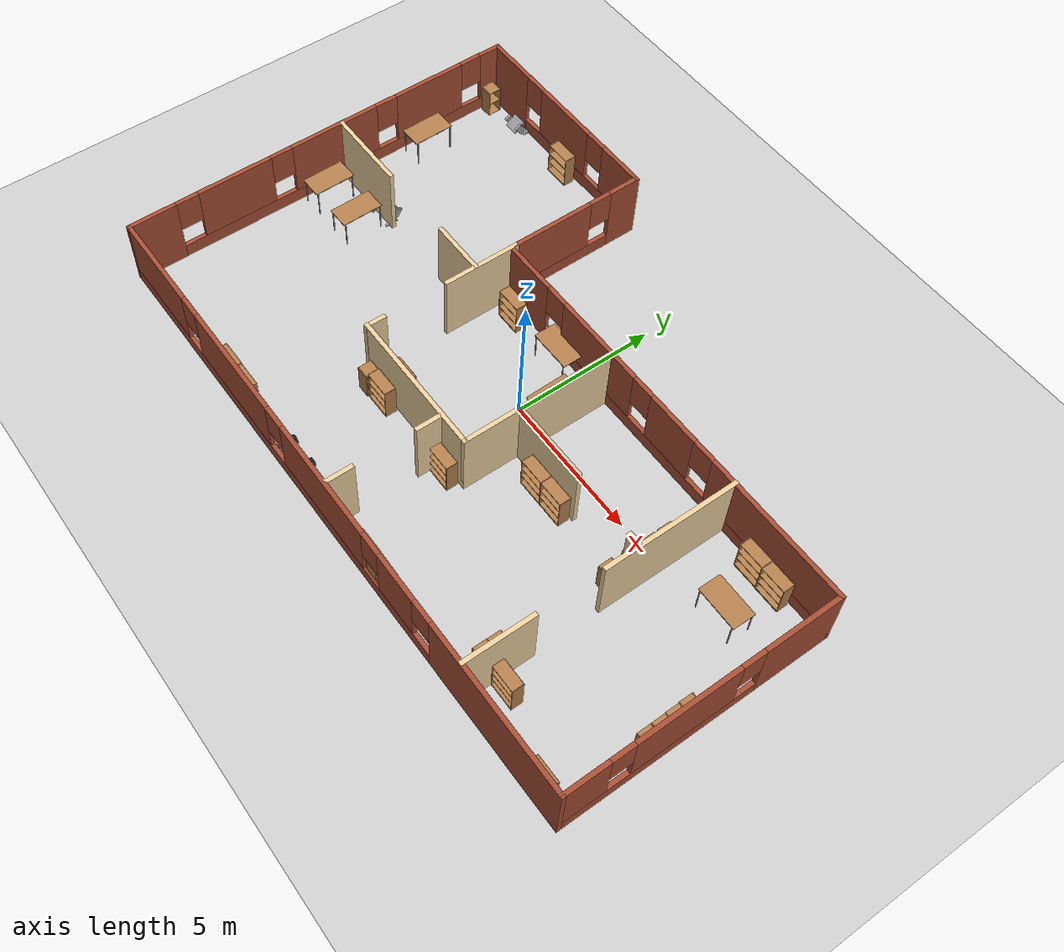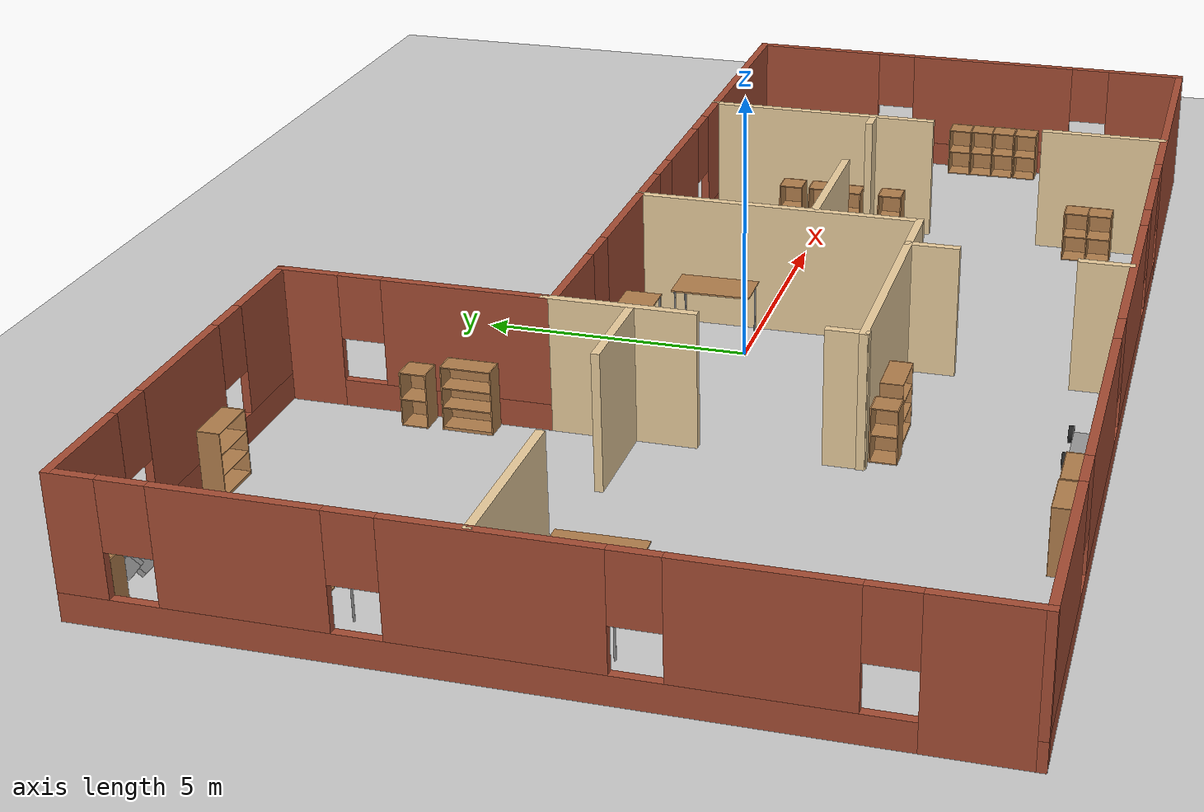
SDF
<sdf version="1.6">
 <world name="default">
  <plugin name="hello" filename="libhello.so"/>
  <light name="sun" type="directional">
   <pose>0 0 10 0 -0 0</pose>
   <diffuse>0.8 0.8 0.8 1</diffuse>
   <specular>0.2 0.2 0.2 1</specular>
   <attenuation>
    <range>1000</range>
    <constant>0.9</constant>
    <linear>0.01</linear>
    <quadratic>0.001</quadratic>
   </attenuation>
   <direction>-0.5 0.1 -0.9</direction>
  </light>
  <model name="ground_plane">
   <static>1</static>
   <link name="link">
    <collision name="collision">
     <geometry><plane><normal>0 0 1</normal><size>100 100</size></plane></geometry>
     <surface><friction><ode><mu>100</mu><mu2>50</mu2></ode></friction></surface>
    </collision>
    <visual name="visual">
     <cast_shadows>0</cast_shadows>
     <geometry><plane><normal>0 0 1</normal><size>100 100</size></plane></geometry>
     <material>
      <script><uri>file://media/materials/scripts/gazebo.material</uri><name>Gazebo/Grey</name></script>
     </material>
    </visual>
   </link>
  </model>
  <gravity>0 0 -9.8</gravity>
  <magnetic_field>6e-06 2.3e-05 -4.2e-05</magnetic_field>
  <atmosphere type="adiabatic"/>
  <physics name="default_physics" default="0" type="ode">
   <max_step_size>0.001</max_step_size>
   <real_time_factor>1</real_time_factor>
   <real_time_update_rate>1000</real_time_update_rate>
  </physics>
  <scene><ambient>0.4 0.4 0.4 1</ambient><background>0.7 0.7 0.7 1</background><shadows>1</shadows></scene>
  <spherical_coordinates>
   <surface_model>EARTH_WGS84</surface_model>
   <latitude_deg>0</latitude_deg>
   <longitude_deg>0</longitude_deg>
   <elevation>0</elevation>
   <heading_deg>0</heading_deg>
  </spherical_coordinates>
  <model name="table">
   <static>1</static>
   <link name="link">
    <collision name="surface">
     <pose>0 0 1 0 -0 0</pose>
     <geometry><box><size>1.5 0.8 0.03</size></box></geometry>
     <surface><friction><ode><mu>0.6</mu><mu2>0.6</mu2></ode></friction></surface>
    </collision>
    <visual name="visual1">
     <pose>0 0 1 0 -0 0</pose>
     <geometry><box><size>1.5 0.8 0.03</size></box></geometry>
     <material>
      <script><uri>file://media/materials/scripts/gazebo.material</uri><name>Gazebo/Wood</name></script>
     </material>
    </visual>
    <collision name="front_left_leg">
     <pose>0.68 0.38 0.5 0 -0 0</pose>
     <geometry><cylinder><radius>0.02</radius><length>1</length></cylinder></geometry>
    </collision>
    <visual name="front_left_leg">
     <pose>0.68 0.38 0.5 0 -0 0</pose>
     <geometry><cylinder><radius>0.02</radius><length>1</length></cylinder></geometry>
     <material>
      <script><uri>file://media/materials/scripts/gazebo.material</uri><name>Gazebo/Grey</name></script>
     </material>
    </visual>
    <collision name="front_right_leg">
     <pose>0.68 -0.38 0.5 0 -0 0</pose>
     <geometry><cylinder><radius>0.02</radius><length>1</length></cylinder></geometry>
    </collision>
    <visual name="front_right_leg">
     <pose>0.68 -0.38 0.5 0 -0 0</pose>
     <geometry><cylinder><radius>0.02</radius><length>1</length></cylinder></geometry>
     <material>
      <script><uri>file://media/materials/scripts/gazebo.material</uri><name>Gazebo/Grey</name></script>
     </material>
    </visual>
    <collision name="back_right_leg">
     <pose>-0.68 -0.38 0.5 0 -0 0</pose>
     <geometry><cylinder><radius>0.02</radius><length>1</length></cylinder></geometry>
    </collision>
    <visual name="back_right_leg">
     <pose>-0.68 -0.38 0.5 0 -0 0</pose>
     <geometry><cylinder><radius>0.02</radius><length>1</length></cylinder></geometry>
     <material>
      <script><uri>file://media/materials/scripts/gazebo.material</uri><name>Gazebo/Grey</name></script>
     </material>
    </visual>
    <collision name="back_left_leg">
     <pose>-0.68 0.38 0.5 0 -0 0</pose>
     <geometry><cylinder><radius>0.02</radius><length>1</length></cylinder></geometry>
    </collision>
    <visual name="back_left_leg">
     <pose>-0.68 0.38 0.5 0 -0 0</pose>
     <geometry><cylinder><radius>0.02</radius><length>1</length></cylinder></geometry>
     <material>
      <script><uri>file://media/materials/scripts/gazebo.material</uri><name>Gazebo/Grey</name></script>
     </material>
    </visual>
   </link>
   <pose>-0.6977 2.01004 0 0 -0 0</pose>
  </model>
  <model name="table_0">
   <static>1</static>
   <link name="link">
    <collision name="surface">
     <pose>0 0 1 0 -0 0</pose>
     <geometry><box><size>1.5 0.8 0.03</size></box></geometry>
     <surface><friction><ode><mu>0.6</mu><mu2>0.6</mu2></ode></friction></surface>
    </collision>
    <visual name="visual1">
     <pose>0 0 1 0 -0 0</pose>
     <geometry><box><size>1.5 0.8 0.03</size></box></geometry>
     <material>
      <script><uri>file://media/materials/scripts/gazebo.material</uri><name>Gazebo/Wood</name></script>
     </material>
    </visual>
    <collision name="front_left_leg">
     <pose>0.68 0.38 0.5 0 -0 0</pose>
     <geometry><cylinder><radius>0.02</radius><length>1</length></cylinder></geometry>
    </collision>
    <visual name="front_left_leg">
     <pose>0.68 0.38 0.5 0 -0 0</pose>
     <geometry><cylinder><radius>0.02</radius><length>1</length></cylinder></geometry>
     <material>
      <script><uri>file://media/materials/scripts/gazebo.material</uri><name>Gazebo/Grey</name></script>
     </material>
    </visual>
    <collision name="front_right_leg">
     <pose>0.68 -0.38 0.5 0 -0 0</pose>
     <geometry><cylinder><radius>0.02</radius><length>1</length></cylinder></geometry>
    </collision>
    <visual name="front_right_leg">
     <pose>0.68 -0.38 0.5 0 -0 0</pose>
     <geometry><cylinder><radius>0.02</radius><length>1</length></cylinder></geometry>
     <material>
      <script><uri>file://media/materials/scripts/gazebo.material</uri><name>Gazebo/Grey</name></script>
     </material>
    </visual>
    <collision name="back_right_leg">
     <pose>-0.68 -0.38 0.5 0 -0 0</pose>
     <geometry><cylinder><radius>0.02</radius><length>1</length></cylinder></geometry>
    </collision>
    <visual name="back_right_leg">
     <pose>-0.68 -0.38 0.5 0 -0 0</pose>
     <geometry><cylinder><radius>0.02</radius><length>1</length></cylinder></geometry>
     <material>
      <script><uri>file://media/materials/scripts/gazebo.material</uri><name>Gazebo/Grey</name></script>
     </material>
    </visual>
    <collision name="back_left_leg">
     <pose>-0.68 0.38 0.5 0 -0 0</pose>
     <geometry><cylinder><radius>0.02</radius><length>1</length></cylinder></geometry>
    </collision>
    <visual name="back_left_leg">
     <pose>-0.68 0.38 0.5 0 -0 0</pose>
     <geometry><cylinder><radius>0.02</radius><length>1</length></cylinder></geometry>
     <material>
      <script><uri>file://media/materials/scripts/gazebo.material</uri><name>Gazebo/Grey</name></script>
     </material>
    </visual>
   </link>
   <pose>-10.7102 3.95299 0 0 0 -1.5538</pose>
  </model>
  <model name="table_2">
   <static>1</static>
   <link name="link">
    <collision name="surface">
     <pose>0 0 1 0 -0 0</pose>
     <geometry><box><size>1.5 0.8 0.03</size></box></geometry>
     <surface><friction><ode><mu>0.6</mu><mu2>0.6</mu2></ode></friction></surface>
    </collision>
    <visual name="visual1">
     <pose>0 0 1 0 -0 0</pose>
     <geometry><box><size>1.5 0.8 0.03</size></box></geometry>
     <material>
      <script><uri>file://media/materials/scripts/gazebo.material</uri><name>Gazebo/Wood</name></script>
     </material>
    </visual>
    <collision name="front_left_leg">
     <pose>0.68 0.38 0.5 0 -0 0</pose>
     <geometry><cylinder><radius>0.02</radius><length>1</length></cylinder></geometry>
    </collision>
    <visual name="front_left_leg">
     <pose>0.68 0.38 0.5 0 -0 0</pose>
     <geometry><cylinder><radius>0.02</radius><length>1</length></cylinder></geometry>
     <material>
      <script><uri>file://media/materials/scripts/gazebo.material</uri><name>Gazebo/Grey</name></script>
     </material>
    </visual>
    <collision name="front_right_leg">
     <pose>0.68 -0.38 0.5 0 -0 0</pose>
     <geometry><cylinder><radius>0.02</radius><length>1</length></cylinder></geometry>
    </collision>
    <visual name="front_right_leg">
     <pose>0.68 -0.38 0.5 0 -0 0</pose>
     <geometry><cylinder><radius>0.02</radius><length>1</length></cylinder></geometry>
     <material>
      <script><uri>file://media/materials/scripts/gazebo.material</uri><name>Gazebo/Grey</name></script>
     </material>
    </visual>
    <collision name="back_right_leg">
     <pose>-0.68 -0.38 0.5 0 -0 0</pose>
     <geometry><cylinder><radius>0.02</radius><length>1</length></cylinder></geometry>
    </collision>
    <visual name="back_right_leg">
     <pose>-0.68 -0.38 0.5 0 -0 0</pose>
     <geometry><cylinder><radius>0.02</radius><length>1</length></cylinder></geometry>
     <material>
      <script><uri>file://media/materials/scripts/gazebo.material</uri><name>Gazebo/Grey</name></script>
     </material>
    </visual>
    <collision name="back_left_leg">
     <pose>-0.68 0.38 0.5 0 -0 0</pose>
     <geometry><cylinder><radius>0.02</radius><length>1</length></cylinder></geometry>
    </collision>
    <visual name="back_left_leg">
     <pose>-0.68 0.38 0.5 0 -0 0</pose>
     <geometry><cylinder><radius>0.02</radius><length>1</length></cylinder></geometry>
     <material>
      <script><uri>file://media/materials/scripts/gazebo.material</uri><name>Gazebo/Grey</name></script>
     </material>
    </visual>
   </link>
   <pose>8.91481 0.43197 0 0 -0 3.12562</pose>
  </model>
  <model name="robot">
   <link name="link_0">
    <inertial>
     <mass>1</mass>
     <inertia>
      <ixx>0.166667</ixx>
      <ixy>0</ixy>
      <ixz>0</ixz>
      <iyy>0.166667</iyy>
      <iyz>0</iyz>
      <izz>0.166667</izz>
     </inertia>
    </inertial>
    <pose>-0.275 0.827554 -0.060043 0 -0 0</pose>
    <visual name="visual">
     <geometry><box><size>0.5 0.5 0.1</size></box></geometry>
     <material>
      <lighting>1</lighting>
      <script><uri>file://media/materials/scripts/gazebo.material</uri><name>Gazebo/Grey</name></script>
      <shader type="pixel"><normal_map>__default__</normal_map></shader>
      <ambient>0.3 0.3 0.3 1</ambient>
      <diffuse>0.7 0.7 0.7 1</diffuse>
      <specular>0.01 0.01 0.01 1</specular>
      <emissive>0 0 0 1</emissive>
     </material>
    </visual>
    <collision name="collision">
     <geometry><box><size>0.5 0.5 0.1</size></box></geometry>
     <surface>
      <friction>
       <ode><mu>1</mu><mu2>1</mu2><fdir1>0 0 0</fdir1><slip1>0</slip1><slip2>0</slip2></ode>
       <torsional>
        <coefficient>1</coefficient>
        <patch_radius>0</patch_radius>
        <surface_radius>0</surface_radius>
        <use_patch_radius>1</use_patch_radius>
        <ode><slip>0</slip></ode>
       </torsional>
      </friction>
      <bounce><restitution_coefficient>0</restitution_coefficient><threshold>1e+06</threshold></bounce>
      <contact>
       <collide_without_contact>0</collide_without_contact>
       <collide_without_contact_bitmask>1</collide_without_contact_bitmask>
       <collide_bitmask>1</collide_bitmask>
       <ode>
        <soft_cfm>0</soft_cfm>
        <soft_erp>0.2</soft_erp>
        <kp>1e+13</kp>
        <kd>1</kd>
        <max_vel>0.01</max_vel>
        <min_depth>0</min_depth>
       </ode>
       <bullet>
        <split_impulse>1</split_impulse>
        <split_impulse_penetration_threshold>-0.01</split_impulse_penetration_threshold>
        <soft_cfm>0</soft_cfm>
        <soft_erp>0.2</soft_erp>
        <kp>1e+13</kp>
        <kd>1</kd>
       </bullet>
      </contact>
     </surface>
    </collision>
   </link>
   <link name="link_1">
    <inertial>
     <mass>1</mass>
     <inertia>
      <ixx>0.166667</ixx>
      <ixy>0</ixy>
      <ixz>0</ixz>
      <iyy>0.166667</iyy>
      <iyz>0</iyz>
      <izz>0.166667</izz>
     </inertia>
    </inertial>
    <pose>0.025 0.827554 -0.260043 0 -0 0</pose>
    <visual name="visual">
     <geometry><box><size>0.1 0.25 0.8</size></box></geometry>
     <material>
      <lighting>1</lighting>
      <script><uri>file://media/materials/scripts/gazebo.material</uri><name>Gazebo/Grey</name></script>
      <shader type="pixel"><normal_map>__default__</normal_map></shader>
      <ambient>0.3 0.3 0.3 1</ambient>
      <diffuse>0.7 0.7 0.7 1</diffuse>
      <specular>0.01 0.01 0.01 1</specular>
      <emissive>0 0 0 1</emissive>
     </material>
    </visual>
    <collision name="collision">
     <geometry><box><size>0.1 0.25 0.8</size></box></geometry>
     <surface>
      <friction>
       <ode><mu>1</mu><mu2>1</mu2><fdir1>0 0 0</fdir1><slip1>0</slip1><slip2>0</slip2></ode>
       <torsional>
        <coefficient>1</coefficient>
        <patch_radius>0</patch_radius>
        <surface_radius>0</surface_radius>
        <use_patch_radius>1</use_patch_radius>
        <ode><slip>0</slip></ode>
       </torsional>
      </friction>
      <bounce><restitution_coefficient>0</restitution_coefficient><threshold>1e+06</threshold></bounce>
      <contact>
       <collide_without_contact>0</collide_without_contact>
       <collide_without_contact_bitmask>1</collide_without_contact_bitmask>
       <collide_bitmask>1</collide_bitmask>
       <ode>
        <soft_cfm>0</soft_cfm>
        <soft_erp>0.2</soft_erp>
        <kp>1e+13</kp>
        <kd>1</kd>
        <max_vel>0.01</max_vel>
        <min_depth>0</min_depth>
       </ode>
       <bullet>
        <split_impulse>1</split_impulse>
        <split_impulse_penetration_threshold>-0.01</split_impulse_penetration_threshold>
        <soft_cfm>0</soft_cfm>
        <soft_erp>0.2</soft_erp>
        <kp>1e+13</kp>
        <kd>1</kd>
       </bullet>
      </contact>
     </surface>
    </collision>
   </link>
   <link name="link_1_0">
    <inertial>
     <mass>1</mass>
     <inertia><ixx>0.145833</ixx><ixy>0</ixy><ixz>0</ixz><iyy>0.145833</iyy><iyz>0</iyz><izz>0.125</izz></inertia>
    </inertial>
    <pose>0.125 0.827554 -0.560043 0 1.57 0</pose>
    <visual name="visual">
     <geometry><cylinder><radius>0.3</radius><length>0.1</length></cylinder></geometry>
     <material>
      <lighting>1</lighting>
      <script><uri>file://media/materials/scripts/gazebo.material</uri><name>Gazebo/Grey</name></script>
      <shader type="pixel"><normal_map>__default__</normal_map></shader>
      <ambient>0.3 0.3 0.3 1</ambient>
      <diffuse>0.7 0.7 0.7 1</diffuse>
      <specular>0.01 0.01 0.01 1</specular>
      <emissive>0 0 0 1</emissive>
     </material>
    </visual>
    <collision name="collision">
     <geometry><cylinder><radius>0.3</radius><length>0.1</length></cylinder></geometry>
     <surface>
      <friction>
       <ode><mu>1</mu><mu2>1</mu2><fdir1>0 0 0</fdir1><slip1>0</slip1><slip2>0</slip2></ode>
       <torsional>
        <coefficient>1</coefficient>
        <patch_radius>0</patch_radius>
        <surface_radius>0</surface_radius>
        <use_patch_radius>1</use_patch_radius>
        <ode><slip>0</slip></ode>
       </torsional>
      </friction>
      <bounce><restitution_coefficient>0</restitution_coefficient><threshold>1e+06</threshold></bounce>
      <contact>
       <collide_without_contact>0</collide_without_contact>
       <collide_without_contact_bitmask>1</collide_without_contact_bitmask>
       <collide_bitmask>1</collide_bitmask>
       <ode>
        <soft_cfm>0</soft_cfm>
        <soft_erp>0.2</soft_erp>
        <kp>1e+13</kp>
        <kd>1</kd>
        <max_vel>0.01</max_vel>
        <min_depth>0</min_depth>
       </ode>
       <bullet>
        <split_impulse>1</split_impulse>
        <split_impulse_penetration_threshold>-0.01</split_impulse_penetration_threshold>
        <soft_cfm>0</soft_cfm>
        <soft_erp>0.2</soft_erp>
        <kp>1e+13</kp>
        <kd>1</kd>
       </bullet>
      </contact>
     </surface>
    </collision>
   </link>
   <link name="link_1_0_clone">
    <inertial>
     <mass>1</mass>
     <inertia><ixx>0.145833</ixx><ixy>0</ixy><ixz>0</ixz><iyy>0.145833</iyy><iyz>0</iyz><izz>0.125</izz></inertia>
    </inertial>
    <pose>-0.675 0.827554 -0.560043 0 1.57 0</pose>
    <visual name="visual_0">
     <geometry><cylinder><radius>0.3</radius><length>0.1</length></cylinder></geometry>
     <material>
      <lighting>1</lighting>
      <script><uri>file://media/materials/scripts/gazebo.material</uri><name>Gazebo/Grey</name></script>
      <shader type="pixel"><normal_map>__default__</normal_map></shader>
      <ambient>0.3 0.3 0.3 1</ambient>
      <diffuse>0.7 0.7 0.7 1</diffuse>
      <specular>0.01 0.01 0.01 1</specular>
      <emissive>0 0 0 1</emissive>
     </material>
    </visual>
    <collision name="collision">
     <geometry><cylinder><radius>0.3</radius><length>0.1</length></cylinder></geometry>
     <surface>
      <friction>
       <ode><mu>1</mu><mu2>1</mu2><fdir1>0 0 0</fdir1><slip1>0</slip1><slip2>0</slip2></ode>
       <torsional>
        <coefficient>1</coefficient>
        <patch_radius>0</patch_radius>
        <surface_radius>0</surface_radius>
        <use_patch_radius>1</use_patch_radius>
        <ode><slip>0</slip></ode>
       </torsional>
      </friction>
      <bounce><restitution_coefficient>0</restitution_coefficient><threshold>1e+06</threshold></bounce>
      <contact>
       <collide_without_contact>0</collide_without_contact>
       <collide_without_contact_bitmask>1</collide_without_contact_bitmask>
       <collide_bitmask>1</collide_bitmask>
       <ode>
        <soft_cfm>0</soft_cfm>
        <soft_erp>0.2</soft_erp>
        <kp>1e+13</kp>
        <kd>1</kd>
        <max_vel>0.01</max_vel>
        <min_depth>0</min_depth>
       </ode>
       <bullet>
        <split_impulse>1</split_impulse>
        <split_impulse_penetration_threshold>-0.01</split_impulse_penetration_threshold>
        <soft_cfm>0</soft_cfm>
        <soft_erp>0.2</soft_erp>
        <kp>1e+13</kp>
        <kd>1</kd>
       </bullet>
      </contact>
     </surface>
    </collision>
   </link>
   <link name="link_1_clone">
    <inertial>
     <mass>1</mass>
     <inertia>
      <ixx>0.166667</ixx>
      <ixy>0</ixy>
      <ixz>0</ixz>
      <iyy>0.166667</iyy>
      <iyz>0</iyz>
      <izz>0.166667</izz>
     </inertia>
    </inertial>
    <pose>-0.575 0.827554 -0.260043 0 -0 0</pose>
    <visual name="visual">
     <geometry><box><size>0.1 0.25 0.81</size></box></geometry>
     <material>
      <lighting>1</lighting>
      <script><uri>file://media/materials/scripts/gazebo.material</uri><name>Gazebo/Grey</name></script>
      <shader type="pixel"><normal_map>__default__</normal_map></shader>
      <ambient>0.3 0.3 0.3 1</ambient>
      <diffuse>0.7 0.7 0.7 1</diffuse>
      <specular>0.01 0.01 0.01 1</specular>
      <emissive>0 0 0 1</emissive>
     </material>
    </visual>
    <collision name="collision">
     <geometry><box><size>0.1 0.25 0.8</size></box></geometry>
     <surface>
      <friction>
       <ode><mu>1</mu><mu2>1</mu2><fdir1>0 0 0</fdir1><slip1>0</slip1><slip2>0</slip2></ode>
       <torsional>
        <coefficient>1</coefficient>
        <patch_radius>0</patch_radius>
        <surface_radius>0</surface_radius>
        <use_patch_radius>1</use_patch_radius>
        <ode><slip>0</slip></ode>
       </torsional>
      </friction>
      <bounce><restitution_coefficient>0</restitution_coefficient><threshold>1e+06</threshold></bounce>
      <contact>
       <collide_without_contact>0</collide_without_contact>
       <collide_without_contact_bitmask>1</collide_without_contact_bitmask>
       <collide_bitmask>1</collide_bitmask>
       <ode>
        <soft_cfm>0</soft_cfm>
        <soft_erp>0.2</soft_erp>
        <kp>1e+13</kp>
        <kd>1</kd>
        <max_vel>0.01</max_vel>
        <min_depth>0</min_depth>
       </ode>
       <bullet>
        <split_impulse>1</split_impulse>
        <split_impulse_penetration_threshold>-0.01</split_impulse_penetration_threshold>
        <soft_cfm>0</soft_cfm>
        <soft_erp>0.2</soft_erp>
        <kp>1e+13</kp>
        <kd>1</kd>
       </bullet>
      </contact>
     </surface>
    </collision>
   </link>
   <joint name="link_0_JOINT_0_0" type="revolute">
    <parent>link_0</parent>
    <child>link_1_clone</child>
    <pose>0 0 0.2 0 -0 0</pose>
    <axis>
     <xyz>1 0 0</xyz>
     <use_parent_model_frame>0</use_parent_model_frame>
     <limit>
      <lower>-1.79769e+308</lower>
      <upper>1.79769e+308</upper>
      <effort>-1</effort>
      <velocity>-1</velocity>
     </limit>
     <dynamics>
      <spring_reference>0</spring_reference>
      <spring_stiffness>0</spring_stiffness>
      <damping>0</damping>
      <friction>0</friction>
     </dynamics>
    </axis>
    <physics>
     <ode><limit><cfm>0</cfm><erp>0.2</erp></limit><suspension><cfm>0</cfm><erp>0.2</erp></suspension></ode>
    </physics>
   </joint>
   <joint name="link_0_JOINT_2" type="revolute">
    <parent>link_0</parent>
    <child>link_1</child>
    <pose>0 0 0.2 0 -0 0</pose>
    <axis>
     <xyz>1 0 0</xyz>
     <use_parent_model_frame>0</use_parent_model_frame>
     <limit>
      <lower>-1.79769e+308</lower>
      <upper>1.79769e+308</upper>
      <effort>-1</effort>
      <velocity>-1</velocity>
     </limit>
     <dynamics>
      <spring_reference>0</spring_reference>
      <spring_stiffness>0</spring_stiffness>
      <damping>0</damping>
      <friction>0</friction>
     </dynamics>
    </axis>
    <physics>
     <ode><limit><cfm>0</cfm><erp>0.2</erp></limit><suspension><cfm>0</cfm><erp>0.2</erp></suspension></ode>
    </physics>
   </joint>
   <joint name="link_1_JOINT_3" type="revolute">
    <parent>link_1</parent>
    <child>link_1_0</child>
    <axis>
     <xyz>0 0 1</xyz>
     <use_parent_model_frame>0</use_parent_model_frame>
     <limit>
      <lower>-1.79769e+308</lower>
      <upper>1.79769e+308</upper>
      <effort>-1</effort>
      <velocity>-1</velocity>
     </limit>
     <dynamics>
      <spring_reference>0</spring_reference>
      <spring_stiffness>0</spring_stiffness>
      <damping>0</damping>
      <friction>0</friction>
     </dynamics>
    </axis>
    <physics>
     <ode><limit><cfm>0</cfm><erp>0.2</erp></limit><suspension><cfm>0</cfm><erp>0.2</erp></suspension></ode>
    </physics>
   </joint>
   <joint name="link_1_clone_JOINT_1" type="revolute">
    <parent>link_1_clone</parent>
    <child>link_1_0_clone</child>
    <axis>
     <xyz>0 0 1</xyz>
     <use_parent_model_frame>0</use_parent_model_frame>
     <limit>
      <lower>-1.79769e+308</lower>
      <upper>1.79769e+308</upper>
      <effort>-1</effort>
      <velocity>-1</velocity>
     </limit>
     <dynamics>
      <spring_reference>0</spring_reference>
      <spring_stiffness>0</spring_stiffness>
      <damping>0</damping>
      <friction>0</friction>
     </dynamics>
    </axis>
    <physics>
     <ode><limit><cfm>0</cfm><erp>0.2</erp></limit><suspension><cfm>0</cfm><erp>0.2</erp></suspension></ode>
    </physics>
   </joint>
   <static>0</static>
   <pose>-9.48709 6.36861 -0.263257 0.652532 -0 0</pose>
  </model>
  <model name="robot_clone">
   <link name="link_0">
    <inertial>
     <mass>1</mass>
     <inertia>
      <ixx>0.166667</ixx>
      <ixy>0</ixy>
      <ixz>0</ixz>
      <iyy>0.166667</iyy>
      <iyz>0</iyz>
      <izz>0.166667</izz>
     </inertia>
    </inertial>
    <pose>-0.275 0.827554 -0.060043 0 -0 0</pose>
    <visual name="visual">
     <geometry><box><size>0.5 0.5 0.1</size></box></geometry>
     <material>
      <lighting>1</lighting>
      <script><uri>file://media/materials/scripts/gazebo.material</uri><name>Gazebo/Grey</name></script>
      <shader type="pixel"><normal_map>__default__</normal_map></shader>
      <ambient>0.3 0.3 0.3 1</ambient>
      <diffuse>0.7 0.7 0.7 1</diffuse>
      <specular>0.01 0.01 0.01 1</specular>
      <emissive>0 0 0 1</emissive>
     </material>
    </visual>
    <collision name="collision">
     <geometry><box><size>0.5 0.5 0.1</size></box></geometry>
     <surface>
      <friction>
       <ode><mu>1</mu><mu2>1</mu2><fdir1>0 0 0</fdir1><slip1>0</slip1><slip2>0</slip2></ode>
       <torsional>
        <coefficient>1</coefficient>
        <patch_radius>0</patch_radius>
        <surface_radius>0</surface_radius>
        <use_patch_radius>1</use_patch_radius>
        <ode><slip>0</slip></ode>
       </torsional>
      </friction>
      <bounce><restitution_coefficient>0</restitution_coefficient><threshold>1e+06</threshold></bounce>
      <contact>
       <collide_without_contact>0</collide_without_contact>
       <collide_without_contact_bitmask>1</collide_without_contact_bitmask>
       <collide_bitmask>1</collide_bitmask>
       <ode>
        <soft_cfm>0</soft_cfm>
        <soft_erp>0.2</soft_erp>
        <kp>1e+13</kp>
        <kd>1</kd>
        <max_vel>0.01</max_vel>
        <min_depth>0</min_depth>
       </ode>
       <bullet>
        <split_impulse>1</split_impulse>
        <split_impulse_penetration_threshold>-0.01</split_impulse_penetration_threshold>
        <soft_cfm>0</soft_cfm>
        <soft_erp>0.2</soft_erp>
        <kp>1e+13</kp>
        <kd>1</kd>
       </bullet>
      </contact>
     </surface>
    </collision>
   </link>
   <link name="link_1">
    <inertial>
     <mass>1</mass>
     <inertia>
      <ixx>0.166667</ixx>
      <ixy>0</ixy>
      <ixz>0</ixz>
      <iyy>0.166667</iyy>
      <iyz>0</iyz>
      <izz>0.166667</izz>
     </inertia>
    </inertial>
    <pose>0.025 0.827554 -0.260043 0 -0 0</pose>
    <visual name="visual">
     <geometry><box><size>0.1 0.25 0.8</size></box></geometry>
     <material>
      <lighting>1</lighting>
      <script><uri>file://media/materials/scripts/gazebo.material</uri><name>Gazebo/Grey</name></script>
      <shader type="pixel"><normal_map>__default__</normal_map></shader>
      <ambient>0.3 0.3 0.3 1</ambient>
      <diffuse>0.7 0.7 0.7 1</diffuse>
      <specular>0.01 0.01 0.01 1</specular>
      <emissive>0 0 0 1</emissive>
     </material>
    </visual>
    <collision name="collision">
     <geometry><box><size>0.1 0.25 0.8</size></box></geometry>
     <surface>
      <friction>
       <ode><mu>1</mu><mu2>1</mu2><fdir1>0 0 0</fdir1><slip1>0</slip1><slip2>0</slip2></ode>
       <torsional>
        <coefficient>1</coefficient>
        <patch_radius>0</patch_radius>
        <surface_radius>0</surface_radius>
        <use_patch_radius>1</use_patch_radius>
        <ode><slip>0</slip></ode>
       </torsional>
      </friction>
      <bounce><restitution_coefficient>0</restitution_coefficient><threshold>1e+06</threshold></bounce>
      <contact>
       <collide_without_contact>0</collide_without_contact>
       <collide_without_contact_bitmask>1</collide_without_contact_bitmask>
       <collide_bitmask>1</collide_bitmask>
       <ode>
        <soft_cfm>0</soft_cfm>
        <soft_erp>0.2</soft_erp>
        <kp>1e+13</kp>
        <kd>1</kd>
        <max_vel>0.01</max_vel>
        <min_depth>0</min_depth>
       </ode>
       <bullet>
        <split_impulse>1</split_impulse>
        <split_impulse_penetration_threshold>-0.01</split_impulse_penetration_threshold>
        <soft_cfm>0</soft_cfm>
        <soft_erp>0.2</soft_erp>
        <kp>1e+13</kp>
        <kd>1</kd>
       </bullet>
      </contact>
     </surface>
    </collision>
   </link>
   <link name="link_1_0">
    <inertial>
     <mass>1</mass>
     <inertia><ixx>0.145833</ixx><ixy>0</ixy><ixz>0</ixz><iyy>0.145833</iyy><iyz>0</iyz><izz>0.125</izz></inertia>
    </inertial>
    <pose>0.125 0.827554 -0.560043 0 1.57 0</pose>
    <visual name="visual">
     <geometry><cylinder><radius>0.3</radius><length>0.1</length></cylinder></geometry>
     <material>
      <lighting>1</lighting>
      <script><uri>file://media/materials/scripts/gazebo.material</uri><name>Gazebo/Grey</name></script>
      <shader type="pixel"><normal_map>__default__</normal_map></shader>
      <ambient>0.3 0.3 0.3 1</ambient>
      <diffuse>0.7 0.7 0.7 1</diffuse>
      <specular>0.01 0.01 0.01 1</specular>
      <emissive>0 0 0 1</emissive>
     </material>
    </visual>
    <collision name="collision">
     <geometry><cylinder><radius>0.3</radius><length>0.1</length></cylinder></geometry>
     <surface>
      <friction>
       <ode><mu>1</mu><mu2>1</mu2><fdir1>0 0 0</fdir1><slip1>0</slip1><slip2>0</slip2></ode>
       <torsional>
        <coefficient>1</coefficient>
        <patch_radius>0</patch_radius>
        <surface_radius>0</surface_radius>
        <use_patch_radius>1</use_patch_radius>
        <ode><slip>0</slip></ode>
       </torsional>
      </friction>
      <bounce><restitution_coefficient>0</restitution_coefficient><threshold>1e+06</threshold></bounce>
      <contact>
       <collide_without_contact>0</collide_without_contact>
       <collide_without_contact_bitmask>1</collide_without_contact_bitmask>
       <collide_bitmask>1</collide_bitmask>
       <ode>
        <soft_cfm>0</soft_cfm>
        <soft_erp>0.2</soft_erp>
        <kp>1e+13</kp>
        <kd>1</kd>
        <max_vel>0.01</max_vel>
        <min_depth>0</min_depth>
       </ode>
       <bullet>
        <split_impulse>1</split_impulse>
        <split_impulse_penetration_threshold>-0.01</split_impulse_penetration_threshold>
        <soft_cfm>0</soft_cfm>
        <soft_erp>0.2</soft_erp>
        <kp>1e+13</kp>
        <kd>1</kd>
       </bullet>
      </contact>
     </surface>
    </collision>
   </link>
   <link name="link_1_0_clone">
    <inertial>
     <mass>1</mass>
     <inertia><ixx>0.145833</ixx><ixy>0</ixy><ixz>0</ixz><iyy>0.145833</iyy><iyz>0</iyz><izz>0.125</izz></inertia>
    </inertial>
    <pose>-0.675 0.827554 -0.560043 0 1.57 0</pose>
    <visual name="visual_0">
     <geometry><cylinder><radius>0.3</radius><length>0.1</length></cylinder></geometry>
     <material>
      <lighting>1</lighting>
      <script><uri>file://media/materials/scripts/gazebo.material</uri><name>Gazebo/Grey</name></script>
      <shader type="pixel"><normal_map>__default__</normal_map></shader>
      <ambient>0.3 0.3 0.3 1</ambient>
      <diffuse>0.7 0.7 0.7 1</diffuse>
      <specular>0.01 0.01 0.01 1</specular>
      <emissive>0 0 0 1</emissive>
     </material>
    </visual>
    <collision name="collision">
     <geometry><cylinder><radius>0.3</radius><length>0.1</length></cylinder></geometry>
     <surface>
      <friction>
       <ode><mu>1</mu><mu2>1</mu2><fdir1>0 0 0</fdir1><slip1>0</slip1><slip2>0</slip2></ode>
       <torsional>
        <coefficient>1</coefficient>
        <patch_radius>0</patch_radius>
        <surface_radius>0</surface_radius>
        <use_patch_radius>1</use_patch_radius>
        <ode><slip>0</slip></ode>
       </torsional>
      </friction>
      <bounce><restitution_coefficient>0</restitution_coefficient><threshold>1e+06</threshold></bounce>
      <contact>
       <collide_without_contact>0</collide_without_contact>
       <collide_without_contact_bitmask>1</collide_without_contact_bitmask>
       <collide_bitmask>1</collide_bitmask>
       <ode>
        <soft_cfm>0</soft_cfm>
        <soft_erp>0.2</soft_erp>
        <kp>1e+13</kp>
        <kd>1</kd>
        <max_vel>0.01</max_vel>
        <min_depth>0</min_depth>
       </ode>
       <bullet>
        <split_impulse>1</split_impulse>
        <split_impulse_penetration_threshold>-0.01</split_impulse_penetration_threshold>
        <soft_cfm>0</soft_cfm>
        <soft_erp>0.2</soft_erp>
        <kp>1e+13</kp>
        <kd>1</kd>
       </bullet>
      </contact>
     </surface>
    </collision>
   </link>
   <link name="link_1_clone">
    <inertial>
     <mass>1</mass>
     <inertia>
      <ixx>0.166667</ixx>
      <ixy>0</ixy>
      <ixz>0</ixz>
      <iyy>0.166667</iyy>
      <iyz>0</iyz>
      <izz>0.166667</izz>
     </inertia>
    </inertial>
    <pose>-0.575 0.827554 -0.260043 0 -0 0</pose>
    <visual name="visual">
     <geometry><box><size>0.1 0.25 0.81</size></box></geometry>
     <material>
      <lighting>1</lighting>
      <script><uri>file://media/materials/scripts/gazebo.material</uri><name>Gazebo/Grey</name></script>
      <shader type="pixel"><normal_map>__default__</normal_map></shader>
      <ambient>0.3 0.3 0.3 1</ambient>
      <diffuse>0.7 0.7 0.7 1</diffuse>
      <specular>0.01 0.01 0.01 1</specular>
      <emissive>0 0 0 1</emissive>
     </material>
    </visual>
    <collision name="collision">
     <geometry><box><size>0.1 0.25 0.8</size></box></geometry>
     <surface>
      <friction>
       <ode><mu>1</mu><mu2>1</mu2><fdir1>0 0 0</fdir1><slip1>0</slip1><slip2>0</slip2></ode>
       <torsional>
        <coefficient>1</coefficient>
        <patch_radius>0</patch_radius>
        <surface_radius>0</surface_radius>
        <use_patch_radius>1</use_patch_radius>
        <ode><slip>0</slip></ode>
       </torsional>
      </friction>
      <bounce><restitution_coefficient>0</restitution_coefficient><threshold>1e+06</threshold></bounce>
      <contact>
       <collide_without_contact>0</collide_without_contact>
       <collide_without_contact_bitmask>1</collide_without_contact_bitmask>
       <collide_bitmask>1</collide_bitmask>
       <ode>
        <soft_cfm>0</soft_cfm>
        <soft_erp>0.2</soft_erp>
        <kp>1e+13</kp>
        <kd>1</kd>
        <max_vel>0.01</max_vel>
        <min_depth>0</min_depth>
       </ode>
       <bullet>
        <split_impulse>1</split_impulse>
        <split_impulse_penetration_threshold>-0.01</split_impulse_penetration_threshold>
        <soft_cfm>0</soft_cfm>
        <soft_erp>0.2</soft_erp>
        <kp>1e+13</kp>
        <kd>1</kd>
       </bullet>
      </contact>
     </surface>
    </collision>
   </link>
   <joint name="link_0_JOINT_0_0" type="revolute">
    <parent>link_0</parent>
    <child>link_1_clone</child>
    <pose>0 0 0.2 0 -0 0</pose>
    <axis>
     <xyz>1 0 0</xyz>
     <use_parent_model_frame>0</use_parent_model_frame>
     <limit>
      <lower>-1.79769e+308</lower>
      <upper>1.79769e+308</upper>
      <effort>-1</effort>
      <velocity>-1</velocity>
     </limit>
     <dynamics>
      <spring_reference>0</spring_reference>
      <spring_stiffness>0</spring_stiffness>
      <damping>0</damping>
      <friction>0</friction>
     </dynamics>
    </axis>
    <physics>
     <ode><limit><cfm>0</cfm><erp>0.2</erp></limit><suspension><cfm>0</cfm><erp>0.2</erp></suspension></ode>
    </physics>
   </joint>
   <joint name="link_0_JOINT_2" type="revolute">
    <parent>link_0</parent>
    <child>link_1</child>
    <pose>0 0 0.2 0 -0 0</pose>
    <axis>
     <xyz>1 0 0</xyz>
     <use_parent_model_frame>0</use_parent_model_frame>
     <limit>
      <lower>-1.79769e+308</lower>
      <upper>1.79769e+308</upper>
      <effort>-1</effort>
      <velocity>-1</velocity>
     </limit>
     <dynamics>
      <spring_reference>0</spring_reference>
      <spring_stiffness>0</spring_stiffness>
      <damping>0</damping>
      <friction>0</friction>
     </dynamics>
    </axis>
    <physics>
     <ode><limit><cfm>0</cfm><erp>0.2</erp></limit><suspension><cfm>0</cfm><erp>0.2</erp></suspension></ode>
    </physics>
   </joint>
   <joint name="link_1_JOINT_3" type="revolute">
    <parent>link_1</parent>
    <child>link_1_0</child>
    <axis>
     <xyz>0 0 1</xyz>
     <use_parent_model_frame>0</use_parent_model_frame>
     <limit>
      <lower>-1.79769e+308</lower>
      <upper>1.79769e+308</upper>
      <effort>-1</effort>
      <velocity>-1</velocity>
     </limit>
     <dynamics>
      <spring_reference>0</spring_reference>
      <spring_stiffness>0</spring_stiffness>
      <damping>0</damping>
      <friction>0</friction>
     </dynamics>
    </axis>
    <physics>
     <ode><limit><cfm>0</cfm><erp>0.2</erp></limit><suspension><cfm>0</cfm><erp>0.2</erp></suspension></ode>
    </physics>
   </joint>
   <joint name="link_1_clone_JOINT_1" type="revolute">
    <parent>link_1_clone</parent>
    <child>link_1_0_clone</child>
    <axis>
     <xyz>0 0 1</xyz>
     <use_parent_model_frame>0</use_parent_model_frame>
     <limit>
      <lower>-1.79769e+308</lower>
      <upper>1.79769e+308</upper>
      <effort>-1</effort>
      <velocity>-1</velocity>
     </limit>
     <dynamics>
      <spring_reference>0</spring_reference>
      <spring_stiffness>0</spring_stiffness>
      <damping>0</damping>
      <friction>0</friction>
     </dynamics>
    </axis>
    <physics>
     <ode><limit><cfm>0</cfm><erp>0.2</erp></limit><suspension><cfm>0</cfm><erp>0.2</erp></suspension></ode>
    </physics>
   </joint>
   <static>0</static>
   <pose>-8.72496 0.660742 0.720381 -0.625823 -1e-06 0.049045</pose>
  </model>
  <model name="building">
   <pose>-0.18085 0.191598 0 0 -0 0</pose>
   <link name="Wall_101">
    <pose>-3.575 4.75 0 0 -0 -1.5708</pose>
    <visual name="Wall_101_Visual_0">
     <pose>-1.91994 0 1.25 0 -0 0</pose>
     <geometry><box><size>1.16012 0.15 2.5</size></box></geometry>
     <material>
      <script><uri>file://media/materials/scripts/gazebo.material</uri><name>Gazebo/Bricks</name></script>
      <ambient>1 1 1 1</ambient>
     </material>
     <meta><layer>0</layer></meta>
    </visual>
    <collision name="Wall_101_Collision_0">
     <geometry><box><size>1.16012 0.15 2.5</size></box></geometry>
     <pose>-1.91994 0 1.25 0 -0 0</pose>
    </collision>
    <visual name="Wall_101_Visual_1">
     <pose>0.580059 0 0.25 0 -0 0</pose>
     <geometry><box><size>3.83988 0.15 0.5</size></box></geometry>
     <material>
      <script><uri>file://media/materials/scripts/gazebo.material</uri><name>Gazebo/Bricks</name></script>
      <ambient>1 1 1 1</ambient>
     </material>
     <meta><layer>0</layer></meta>
    </visual>
    <collision name="Wall_101_Collision_1">
     <geometry><box><size>3.83988 0.15 0.5</size></box></geometry>
     <pose>0.580059 0 0.25 0 -0 0</pose>
    </collision>
    <visual name="Wall_101_Visual_2">
     <pose>0.980059 0 1.5 0 -0 0</pose>
     <geometry><box><size>3.03988 0.15 2</size></box></geometry>
     <material>
      <script><uri>file://media/materials/scripts/gazebo.material</uri><name>Gazebo/Bricks</name></script>
      <ambient>1 1 1 1</ambient>
     </material>
     <meta><layer>0</layer></meta>
    </visual>
    <collision name="Wall_101_Collision_2">
     <geometry><box><size>3.03988 0.15 2</size></box></geometry>
     <pose>0.980059 0 1.5 0 -0 0</pose>
    </collision>
    <visual name="Wall_101_Visual_3">
     <pose>-0.939883 0 1.9 0 -0 0</pose>
     <geometry><box><size>0.8 0.15 1.2</size></box></geometry>
     <material>
      <script><uri>file://media/materials/scripts/gazebo.material</uri><name>Gazebo/Bricks</name></script>
      <ambient>1 1 1 1</ambient>
     </material>
     <meta><layer>0</layer></meta>
    </visual>
    <collision name="Wall_101_Collision_3">
     <geometry><box><size>0.8 0.15 1.2</size></box></geometry>
     <pose>-0.939883 0 1.9 0 -0 0</pose>
    </collision>
   </link>
   <link name="Wall_103">
    <collision name="Wall_103_Collision">
     <geometry><box><size>2.75 0.15 2.5</size></box></geometry>
     <pose>0 0 1.25 0 -0 0</pose>
    </collision>
    <visual name="Wall_103_Visual">
     <pose>0 0 1.25 0 -0 0</pose>
     <geometry><box><size>2.75 0.15 2.5</size></box></geometry>
     <material>
      <script><uri>file://media/materials/scripts/gazebo.material</uri><name>Gazebo/Grey</name></script>
      <ambient>0.921569 0.807843 0.615686 1</ambient>
     </material>
     <meta><layer>0</layer></meta>
    </visual>
    <pose>-3.575 1.025 0 0 -0 -1.5708</pose>
   </link>
   <link name="Wall_19">
    <pose>3.875 2.175 0 0 -0 0</pose>
    <visual name="Wall_19_Visual_0">
     <pose>-6.43713 0 1.25 0 -0 0</pose>
     <geometry><box><size>1.87573 0.15 2.5</size></box></geometry>
     <material>
      <script><uri>file://media/materials/scripts/gazebo.material</uri><name>Gazebo/Bricks</name></script>
      <ambient>1 1 1 1</ambient>
     </material>
     <meta><layer>0</layer></meta>
    </visual>
    <collision name="Wall_19_Collision_0">
     <geometry><box><size>1.87573 0.15 2.5</size></box></geometry>
     <pose>-6.43713 0 1.25 0 -0 0</pose>
    </collision>
    <visual name="Wall_19_Visual_1">
     <pose>0.937865 0 0.25 0 -0 0</pose>
     <geometry><box><size>12.8743 0.15 0.5</size></box></geometry>
     <material>
      <script><uri>file://media/materials/scripts/gazebo.material</uri><name>Gazebo/Bricks</name></script>
      <ambient>1 1 1 1</ambient>
     </material>
     <meta><layer>0</layer></meta>
    </visual>
    <collision name="Wall_19_Collision_1">
     <geometry><box><size>12.8743 0.15 0.5</size></box></geometry>
     <pose>0.937865 0 0.25 0 -0 0</pose>
    </collision>
    <visual name="Wall_19_Visual_2">
     <pose>-3.03299 0 1.5 0 -0 0</pose>
     <geometry><box><size>3.33255 0.15 2</size></box></geometry>
     <material>
      <script><uri>file://media/materials/scripts/gazebo.material</uri><name>Gazebo/Bricks</name></script>
      <ambient>1 1 1 1</ambient>
     </material>
     <meta><layer>0</layer></meta>
    </visual>
    <collision name="Wall_19_Collision_2">
     <geometry><box><size>3.33255 0.15 2</size></box></geometry>
     <pose>-3.03299 0 1.5 0 -0 0</pose>
    </collision>
    <visual name="Wall_19_Visual_3">
     <pose>0.383521 0 1.5 0 -0 0</pose>
     <geometry><box><size>1.90048 0.15 2</size></box></geometry>
     <material>
      <script><uri>file://media/materials/scripts/gazebo.material</uri><name>Gazebo/Bricks</name></script>
      <ambient>1 1 1 1</ambient>
     </material>
     <meta><layer>0</layer></meta>
    </visual>
    <collision name="Wall_19_Collision_3">
     <geometry><box><size>1.90048 0.15 2</size></box></geometry>
     <pose>0.383521 0 1.5 0 -0 0</pose>
    </collision>
    <visual name="Wall_19_Visual_4">
     <pose>4.75438 0 1.5 0 -0 0</pose>
     <geometry><box><size>5.24124 0.15 2</size></box></geometry>
     <material>
      <script><uri>file://media/materials/scripts/gazebo.material</uri><name>Gazebo/Bricks</name></script>
      <ambient>1 1 1 1</ambient>
     </material>
     <meta><layer>0</layer></meta>
    </visual>
    <collision name="Wall_19_Collision_4">
     <geometry><box><size>5.24124 0.15 2</size></box></geometry>
     <pose>4.75438 0 1.5 0 -0 0</pose>
    </collision>
    <visual name="Wall_19_Visual_5">
     <pose>-5.09927 0 1.9 0 -0 0</pose>
     <geometry><box><size>0.8 0.15 1.2</size></box></geometry>
     <material>
      <script><uri>file://media/materials/scripts/gazebo.material</uri><name>Gazebo/Bricks</name></script>
      <ambient>1 1 1 1</ambient>
     </material>
     <meta><layer>0</layer></meta>
    </visual>
    <collision name="Wall_19_Collision_5">
     <geometry><box><size>0.8 0.15 1.2</size></box></geometry>
     <pose>-5.09927 0 1.9 0 -0 0</pose>
    </collision>
    <visual name="Wall_19_Visual_6">
     <pose>-0.966718 0 1.9 0 -0 0</pose>
     <geometry><box><size>0.8 0.15 1.2</size></box></geometry>
     <material>
      <script><uri>file://media/materials/scripts/gazebo.material</uri><name>Gazebo/Bricks</name></script>
      <ambient>1 1 1 1</ambient>
     </material>
     <meta><layer>0</layer></meta>
    </visual>
    <collision name="Wall_19_Collision_6">
     <geometry><box><size>0.8 0.15 1.2</size></box></geometry>
     <pose>-0.966718 0 1.9 0 -0 0</pose>
    </collision>
    <visual name="Wall_19_Visual_7">
     <pose>1.73376 0 1.9 0 -0 0</pose>
     <geometry><box><size>0.8 0.15 1.2</size></box></geometry>
     <material>
      <script><uri>file://media/materials/scripts/gazebo.material</uri><name>Gazebo/Bricks</name></script>
      <ambient>1 1 1 1</ambient>
     </material>
     <meta><layer>0</layer></meta>
    </visual>
    <collision name="Wall_19_Collision_7">
     <geometry><box><size>0.8 0.15 1.2</size></box></geometry>
     <pose>1.73376 0 1.9 0 -0 0</pose>
    </collision>
   </link>
   <link name="Wall_45">
    <collision name="Wall_45_Collision">
     <geometry><box><size>3 0.15 2.5</size></box></geometry>
     <pose>0 0 1.25 0 -0 0</pose>
    </collision>
    <visual name="Wall_45_Visual">
     <pose>0 0 1.25 0 -0 0</pose>
     <geometry><box><size>3 0.15 2.5</size></box></geometry>
     <material>
      <script><uri>file://media/materials/scripts/gazebo.material</uri><name>Gazebo/Grey</name></script>
      <ambient>0.921569 0.807843 0.615686 1</ambient>
     </material>
     <meta><layer>0</layer></meta>
    </visual>
    <pose>-9.70177 0.771555 0 0 -0 0</pose>
   </link>
   <link name="Wall_47">
    <collision name="Wall_47_Collision">
     <geometry><box><size>2 0.15 2.5</size></box></geometry>
     <pose>0 0 1.25 0 -0 0</pose>
    </collision>
    <visual name="Wall_47_Visual">
     <pose>0 0 1.25 0 -0 0</pose>
     <geometry><box><size>2 0.15 2.5</size></box></geometry>
     <material>
      <script><uri>file://media/materials/scripts/gazebo.material</uri><name>Gazebo/Grey</name></script>
      <ambient>0.921569 0.807843 0.615686 1</ambient>
     </material>
     <meta><layer>0</layer></meta>
    </visual>
    <pose>-4.51547 0.805423 0 0 -0 0</pose>
   </link>
   <link name="Wall_60">
    <collision name="Wall_60_Collision">
     <geometry><box><size>5.20343 0.15 2.5</size></box></geometry>
     <pose>0 0 1.25 0 -0 0</pose>
    </collision>
    <visual name="Wall_60_Visual">
     <pose>0 0 1.25 0 -0 0</pose>
     <geometry><box><size>5.20343 0.15 2.5</size></box></geometry>
     <material>
      <script><uri>file://media/materials/scripts/gazebo.material</uri><name>Gazebo/Grey</name></script>
      <ambient>0.921569 0.807843 0.615686 1</ambient>
     </material>
     <meta><layer>0</layer></meta>
    </visual>
    <pose>-1.09679 -3.17412 0 0 -0 0</pose>
   </link>
   <link name="Wall_63">
    <collision name="Wall_63_Collision">
     <geometry><box><size>2.75 0.15 2.5</size></box></geometry>
     <pose>0 0 1.25 0 -0 0</pose>
    </collision>
    <visual name="Wall_63_Visual">
     <pose>0 0 1.25 0 -0 0</pose>
     <geometry><box><size>2.75 0.15 2.5</size></box></geometry>
     <material>
      <script><uri>file://media/materials/scripts/gazebo.material</uri><name>Gazebo/Grey</name></script>
      <ambient>0.921569 0.807843 0.615686 1</ambient>
     </material>
     <meta><layer>0</layer></meta>
    </visual>
    <pose>2.84816 -1.19957 0 0 -0 0</pose>
   </link>
   <link name="Wall_65">
    <collision name="Wall_65_Collision">
     <geometry><box><size>4.75 0.15 2.5</size></box></geometry>
     <pose>0 0 1.25 0 -0 0</pose>
    </collision>
    <visual name="Wall_65_Visual">
     <pose>0 0 1.25 0 -0 0</pose>
     <geometry><box><size>4.75 0.15 2.5</size></box></geometry>
     <material>
      <script><uri>file://media/materials/scripts/gazebo.material</uri><name>Gazebo/Grey</name></script>
      <ambient>0.921569 0.807843 0.615686 1</ambient>
     </material>
     <meta><layer>0</layer></meta>
    </visual>
    <pose>6.90976 -0.111242 0 0 -0 -1.5708</pose>
   </link>
   <link name="Wall_68">
    <collision name="Wall_68_Collision">
     <geometry><box><size>2.5 0.15 2.5</size></box></geometry>
     <pose>0 0 1.25 0 -0 0</pose>
    </collision>
    <visual name="Wall_68_Visual">
     <pose>0 0 1.25 0 -0 0</pose>
     <geometry><box><size>2.5 0.15 2.5</size></box></geometry>
     <material>
      <script><uri>file://media/materials/scripts/gazebo.material</uri><name>Gazebo/Grey</name></script>
      <ambient>0.921569 0.807843 0.615686 1</ambient>
     </material>
     <meta><layer>0</layer></meta>
    </visual>
    <pose>6.91101 -5.97785 0 0 -0 -1.5708</pose>
   </link>
   <link name="Wall_72">
    <collision name="Wall_72_Collision">
     <geometry><box><size>0.5 0.15 2.5</size></box></geometry>
     <pose>0 0 1.25 0 -0 0</pose>
    </collision>
    <visual name="Wall_72_Visual">
     <pose>0 0 1.25 0 -0 0</pose>
     <geometry><box><size>0.5 0.15 2.5</size></box></geometry>
     <material>
      <script><uri>file://media/materials/scripts/gazebo.material</uri><name>Gazebo/Grey</name></script>
      <ambient>0.921569 0.807843 0.615686 1</ambient>
     </material>
     <meta><layer>0</layer></meta>
    </visual>
    <pose>6.65459 -1.22008 0 0 -0 0</pose>
   </link>
   <link name="Wall_75">
    <collision name="Wall_75_Collision">
     <geometry><box><size>1 0.15 2.5</size></box></geometry>
     <pose>0 0 1.25 0 -0 0</pose>
    </collision>
    <visual name="Wall_75_Visual">
     <pose>0 0 1.25 0 -0 0</pose>
     <geometry><box><size>1 0.15 2.5</size></box></geometry>
     <material>
      <script><uri>file://media/materials/scripts/gazebo.material</uri><name>Gazebo/Grey</name></script>
      <ambient>0.921569 0.807843 0.615686 1</ambient>
     </material>
     <meta><layer>0</layer></meta>
    </visual>
    <pose>0.314782 -3.61339 0 0 -0 -1.5708</pose>
   </link>
   <link name="Wall_77">
    <collision name="Wall_77_Collision">
     <geometry><box><size>1 0.15 2.5</size></box></geometry>
     <pose>0 0 1.25 0 -0 0</pose>
    </collision>
    <visual name="Wall_77_Visual">
     <pose>0 0 1.25 0 -0 0</pose>
     <geometry><box><size>1 0.15 2.5</size></box></geometry>
     <material>
      <script><uri>file://media/materials/scripts/gazebo.material</uri><name>Gazebo/Grey</name></script>
      <ambient>0.921569 0.807843 0.615686 1</ambient>
     </material>
     <meta><layer>0</layer></meta>
    </visual>
    <pose>0.289318 -6.69376 0 0 -0 1.5708</pose>
   </link>
   <link name="Wall_80">
    <collision name="Wall_80_Collision">
     <geometry><box><size>5.5 0.15 2.5</size></box></geometry>
     <pose>0 0 1.25 0 -0 0</pose>
    </collision>
    <visual name="Wall_80_Visual">
     <pose>0 0 1.25 0 -0 0</pose>
     <geometry><box><size>5.5 0.15 2.5</size></box></geometry>
     <material>
      <script><uri>file://media/materials/scripts/gazebo.material</uri><name>Gazebo/Grey</name></script>
      <ambient>0.921569 0.807843 0.615686 1</ambient>
     </material>
     <meta><layer>0</layer></meta>
    </visual>
    <pose>1.42992 -0.499121 0 0 -0 1.5708</pose>
   </link>
   <link name="Wall_82">
    <pose>11.175 -2.5 0 0 -0 -1.5708</pose>
    <visual name="Wall_82_Visual_0">
     <pose>-3.36694 0 1.25 0 -0 0</pose>
     <geometry><box><size>2.76612 0.15 2.5</size></box></geometry>
     <material>
      <script><uri>file://media/materials/scripts/gazebo.material</uri><name>Gazebo/Bricks</name></script>
      <ambient>1 1 1 1</ambient>
     </material>
     <meta><layer>0</layer></meta>
    </visual>
    <collision name="Wall_82_Collision_0">
     <geometry><box><size>2.76612 0.15 2.5</size></box></geometry>
     <pose>-3.36694 0 1.25 0 -0 0</pose>
    </collision>
    <visual name="Wall_82_Visual_1">
     <pose>1.38306 0 0.25 0 -0 0</pose>
     <geometry><box><size>6.73388 0.15 0.5</size></box></geometry>
     <material>
      <script><uri>file://media/materials/scripts/gazebo.material</uri><name>Gazebo/Bricks</name></script>
      <ambient>1 1 1 1</ambient>
     </material>
     <meta><layer>0</layer></meta>
    </visual>
    <collision name="Wall_82_Collision_1">
     <geometry><box><size>6.73388 0.15 0.5</size></box></geometry>
     <pose>1.38306 0 0.25 0 -0 0</pose>
    </collision>
    <visual name="Wall_82_Visual_2">
     <pose>0.584685 0 1.5 0 -0 0</pose>
     <geometry><box><size>3.53713 0.15 2</size></box></geometry>
     <material>
      <script><uri>file://media/materials/scripts/gazebo.material</uri><name>Gazebo/Bricks</name></script>
      <ambient>1 1 1 1</ambient>
     </material>
     <meta><layer>0</layer></meta>
    </visual>
    <collision name="Wall_82_Collision_2">
     <geometry><box><size>3.53713 0.15 2</size></box></geometry>
     <pose>0.584685 0 1.5 0 -0 0</pose>
    </collision>
    <visual name="Wall_82_Visual_3">
     <pose>3.95163 0 1.5 0 -0 0</pose>
     <geometry><box><size>1.59675 0.15 2</size></box></geometry>
     <material>
      <script><uri>file://media/materials/scripts/gazebo.material</uri><name>Gazebo/Bricks</name></script>
      <ambient>1 1 1 1</ambient>
     </material>
     <meta><layer>0</layer></meta>
    </visual>
    <collision name="Wall_82_Collision_3">
     <geometry><box><size>1.59675 0.15 2</size></box></geometry>
     <pose>3.95163 0 1.5 0 -0 0</pose>
    </collision>
    <visual name="Wall_82_Visual_4">
     <pose>-1.58388 0 1.9 0 -0 0</pose>
     <geometry><box><size>0.8 0.15 1.2</size></box></geometry>
     <material>
      <script><uri>file://media/materials/scripts/gazebo.material</uri><name>Gazebo/Bricks</name></script>
      <ambient>1 1 1 1</ambient>
     </material>
     <meta><layer>0</layer></meta>
    </visual>
    <collision name="Wall_82_Collision_4">
     <geometry><box><size>0.8 0.15 1.2</size></box></geometry>
     <pose>-1.58388 0 1.9 0 -0 0</pose>
    </collision>
    <visual name="Wall_82_Visual_5">
     <pose>2.75325 0 1.9 0 -0 0</pose>
     <geometry><box><size>0.8 0.15 1.2</size></box></geometry>
     <material>
      <script><uri>file://media/materials/scripts/gazebo.material</uri><name>Gazebo/Bricks</name></script>
      <ambient>1 1 1 1</ambient>
     </material>
     <meta><layer>0</layer></meta>
    </visual>
    <collision name="Wall_82_Collision_5">
     <geometry><box><size>0.8 0.15 1.2</size></box></geometry>
     <pose>2.75325 0 1.9 0 -0 0</pose>
    </collision>
   </link>
   <link name="Wall_84">
    <pose>1e-06 -7.175 0 0 -0 3.14159</pose>
    <visual name="Wall_84_Visual_0">
     <pose>-8.38388 0 1.25 0 -0 0</pose>
     <geometry><box><size>5.73224 0.15 2.5</size></box></geometry>
     <material>
      <script><uri>file://media/materials/scripts/gazebo.material</uri><name>Gazebo/Bricks</name></script>
      <ambient>1 1 1 1</ambient>
     </material>
     <meta><layer>0</layer></meta>
    </visual>
    <collision name="Wall_84_Collision_0">
     <geometry><box><size>5.73224 0.15 2.5</size></box></geometry>
     <pose>-8.38388 0 1.25 0 -0 0</pose>
    </collision>
    <visual name="Wall_84_Visual_1">
     <pose>2.86612 0 0.25 0 -0 0</pose>
     <geometry><box><size>16.7678 0.15 0.5</size></box></geometry>
     <material>
      <script><uri>file://media/materials/scripts/gazebo.material</uri><name>Gazebo/Bricks</name></script>
      <ambient>1 1 1 1</ambient>
     </material>
     <meta><layer>0</layer></meta>
    </visual>
    <collision name="Wall_84_Collision_1">
     <geometry><box><size>16.7678 0.15 0.5</size></box></geometry>
     <pose>2.86612 0 0.25 0 -0 0</pose>
    </collision>
    <visual name="Wall_84_Visual_2">
     <pose>-3.87611 0 1.5 0 -0 0</pose>
     <geometry><box><size>1.6833 0.15 2</size></box></geometry>
     <material>
      <script><uri>file://media/materials/scripts/gazebo.material</uri><name>Gazebo/Bricks</name></script>
      <ambient>1 1 1 1</ambient>
     </material>
     <meta><layer>0</layer></meta>
    </visual>
    <collision name="Wall_84_Collision_2">
     <geometry><box><size>1.6833 0.15 2</size></box></geometry>
     <pose>-3.87611 0 1.5 0 -0 0</pose>
    </collision>
    <visual name="Wall_84_Visual_3">
     <pose>-0.118264 0 1.5 0 -0 0</pose>
     <geometry><box><size>4.2324 0.15 2</size></box></geometry>
     <material>
      <script><uri>file://media/materials/scripts/gazebo.material</uri><name>Gazebo/Bricks</name></script>
      <ambient>1 1 1 1</ambient>
     </material>
     <meta><layer>0</layer></meta>
    </visual>
    <collision name="Wall_84_Collision_3">
     <geometry><box><size>4.2324 0.15 2</size></box></geometry>
     <pose>-0.118264 0 1.5 0 -0 0</pose>
    </collision>
    <visual name="Wall_84_Visual_4">
     <pose>4.86003 0 1.5 0 -0 0</pose>
     <geometry><box><size>4.12418 0.15 2</size></box></geometry>
     <material>
      <script><uri>file://media/materials/scripts/gazebo.material</uri><name>Gazebo/Bricks</name></script>
      <ambient>1 1 1 1</ambient>
     </material>
     <meta><layer>0</layer></meta>
    </visual>
    <collision name="Wall_84_Collision_4">
     <geometry><box><size>4.12418 0.15 2</size></box></geometry>
     <pose>4.86003 0 1.5 0 -0 0</pose>
    </collision>
    <visual name="Wall_84_Visual_5">
     <pose>9.48606 0 1.5 0 -0 0</pose>
     <geometry><box><size>3.52788 0.15 2</size></box></geometry>
     <material>
      <script><uri>file://media/materials/scripts/gazebo.material</uri><name>Gazebo/Bricks</name></script>
      <ambient>1 1 1 1</ambient>
     </material>
     <meta><layer>0</layer></meta>
    </visual>
    <collision name="Wall_84_Collision_5">
     <geometry><box><size>3.52788 0.15 2</size></box></geometry>
     <pose>9.48606 0 1.5 0 -0 0</pose>
    </collision>
    <visual name="Wall_84_Visual_6">
     <pose>-5.11776 0 1.9 0 -0 0</pose>
     <geometry><box><size>0.8 0.15 1.2</size></box></geometry>
     <material>
      <script><uri>file://media/materials/scripts/gazebo.material</uri><name>Gazebo/Bricks</name></script>
      <ambient>1 1 1 1</ambient>
     </material>
     <meta><layer>0</layer></meta>
    </visual>
    <collision name="Wall_84_Collision_6">
     <geometry><box><size>0.8 0.15 1.2</size></box></geometry>
     <pose>-5.11776 0 1.9 0 -0 0</pose>
    </collision>
    <visual name="Wall_84_Visual_7">
     <pose>-2.63447 0 1.9 0 -0 0</pose>
     <geometry><box><size>0.8 0.15 1.2</size></box></geometry>
     <material>
      <script><uri>file://media/materials/scripts/gazebo.material</uri><name>Gazebo/Bricks</name></script>
      <ambient>1 1 1 1</ambient>
     </material>
     <meta><layer>0</layer></meta>
    </visual>
    <collision name="Wall_84_Collision_7">
     <geometry><box><size>0.8 0.15 1.2</size></box></geometry>
     <pose>-2.63447 0 1.9 0 -0 0</pose>
    </collision>
    <visual name="Wall_84_Visual_8">
     <pose>2.39794 0 1.9 0 -0 0</pose>
     <geometry><box><size>0.8 0.15 1.2</size></box></geometry>
     <material>
      <script><uri>file://media/materials/scripts/gazebo.material</uri><name>Gazebo/Bricks</name></script>
      <ambient>1 1 1 1</ambient>
     </material>
     <meta><layer>0</layer></meta>
    </visual>
    <collision name="Wall_84_Collision_8">
     <geometry><box><size>0.8 0.15 1.2</size></box></geometry>
     <pose>2.39794 0 1.9 0 -0 0</pose>
    </collision>
    <visual name="Wall_84_Visual_9">
     <pose>7.32212 0 1.9 0 -0 0</pose>
     <geometry><box><size>0.8 0.15 1.2</size></box></geometry>
     <material>
      <script><uri>file://media/materials/scripts/gazebo.material</uri><name>Gazebo/Bricks</name></script>
      <ambient>1 1 1 1</ambient>
     </material>
     <meta><layer>0</layer></meta>
    </visual>
    <collision name="Wall_84_Collision_9">
     <geometry><box><size>0.8 0.15 1.2</size></box></geometry>
     <pose>7.32212 0 1.9 0 -0 0</pose>
    </collision>
   </link>
   <link name="Wall_86">
    <pose>-11.175 0 0 0 -0 1.5708</pose>
    <visual name="Wall_86_Visual_0">
     <pose>-6.38206 0 1.25 0 -0 0</pose>
     <geometry><box><size>1.73587 0.15 2.5</size></box></geometry>
     <material>
      <script><uri>file://media/materials/scripts/gazebo.material</uri><name>Gazebo/Bricks</name></script>
      <ambient>1 1 1 1</ambient>
     </material>
     <meta><layer>0</layer></meta>
    </visual>
    <collision name="Wall_86_Collision_0">
     <geometry><box><size>1.73587 0.15 2.5</size></box></geometry>
     <pose>-6.38206 0 1.25 0 -0 0</pose>
    </collision>
    <visual name="Wall_86_Visual_1">
     <pose>0.867936 0 0.25 0 -0 0</pose>
     <geometry><box><size>12.7641 0.15 0.5</size></box></geometry>
     <material>
      <script><uri>file://media/materials/scripts/gazebo.material</uri><name>Gazebo/Bricks</name></script>
      <ambient>1 1 1 1</ambient>
     </material>
     <meta><layer>0</layer></meta>
    </visual>
    <collision name="Wall_86_Collision_1">
     <geometry><box><size>12.7641 0.15 0.5</size></box></geometry>
     <pose>0.867936 0 0.25 0 -0 0</pose>
    </collision>
    <visual name="Wall_86_Visual_2">
     <pose>-3.35549 0 1.5 0 -0 0</pose>
     <geometry><box><size>2.71727 0.15 2</size></box></geometry>
     <material>
      <script><uri>file://media/materials/scripts/gazebo.material</uri><name>Gazebo/Bricks</name></script>
      <ambient>1 1 1 1</ambient>
     </material>
     <meta><layer>0</layer></meta>
    </visual>
    <collision name="Wall_86_Collision_2">
     <geometry><box><size>2.71727 0.15 2</size></box></geometry>
     <pose>-3.35549 0 1.5 0 -0 0</pose>
    </collision>
    <visual name="Wall_86_Visual_3">
     <pose>0.461999 0 1.5 0 -0 0</pose>
     <geometry><box><size>3.31771 0.15 2</size></box></geometry>
     <material>
      <script><uri>file://media/materials/scripts/gazebo.material</uri><name>Gazebo/Bricks</name></script>
      <ambient>1 1 1 1</ambient>
     </material>
     <meta><layer>0</layer></meta>
    </visual>
    <collision name="Wall_86_Collision_3">
     <geometry><box><size>3.31771 0.15 2</size></box></geometry>
     <pose>0.461999 0 1.5 0 -0 0</pose>
    </collision>
    <visual name="Wall_86_Visual_4">
     <pose>4.2598 0 1.5 0 -0 0</pose>
     <geometry><box><size>2.67789 0.15 2</size></box></geometry>
     <material>
      <script><uri>file://media/materials/scripts/gazebo.material</uri><name>Gazebo/Bricks</name></script>
      <ambient>1 1 1 1</ambient>
     </material>
     <meta><layer>0</layer></meta>
    </visual>
    <collision name="Wall_86_Collision_4">
     <geometry><box><size>2.67789 0.15 2</size></box></geometry>
     <pose>4.2598 0 1.5 0 -0 0</pose>
    </collision>
    <visual name="Wall_86_Visual_5">
     <pose>6.82437 0 1.5 0 -0 0</pose>
     <geometry><box><size>0.851257 0.15 2</size></box></geometry>
     <material>
      <script><uri>file://media/materials/scripts/gazebo.material</uri><name>Gazebo/Bricks</name></script>
      <ambient>1 1 1 1</ambient>
     </material>
     <meta><layer>0</layer></meta>
    </visual>
    <collision name="Wall_86_Collision_5">
     <geometry><box><size>0.851257 0.15 2</size></box></geometry>
     <pose>6.82437 0 1.5 0 -0 0</pose>
    </collision>
    <visual name="Wall_86_Visual_6">
     <pose>-5.11413 0 1.9 0 -0 0</pose>
     <geometry><box><size>0.8 0.15 1.2</size></box></geometry>
     <material>
      <script><uri>file://media/materials/scripts/gazebo.material</uri><name>Gazebo/Bricks</name></script>
      <ambient>1 1 1 1</ambient>
     </material>
     <meta><layer>0</layer></meta>
    </visual>
    <collision name="Wall_86_Collision_6">
     <geometry><box><size>0.8 0.15 1.2</size></box></geometry>
     <pose>-5.11413 0 1.9 0 -0 0</pose>
    </collision>
    <visual name="Wall_86_Visual_7">
     <pose>-1.59686 0 1.9 0 -0 0</pose>
     <geometry><box><size>0.8 0.15 1.2</size></box></geometry>
     <material>
      <script><uri>file://media/materials/scripts/gazebo.material</uri><name>Gazebo/Bricks</name></script>
      <ambient>1 1 1 1</ambient>
     </material>
     <meta><layer>0</layer></meta>
    </visual>
    <collision name="Wall_86_Collision_7">
     <geometry><box><size>0.8 0.15 1.2</size></box></geometry>
     <pose>-1.59686 0 1.9 0 -0 0</pose>
    </collision>
    <visual name="Wall_86_Visual_8">
     <pose>2.52085 0 1.9 0 -0 0</pose>
     <geometry><box><size>0.8 0.15 1.2</size></box></geometry>
     <material>
      <script><uri>file://media/materials/scripts/gazebo.material</uri><name>Gazebo/Bricks</name></script>
      <ambient>1 1 1 1</ambient>
     </material>
     <meta><layer>0</layer></meta>
    </visual>
    <collision name="Wall_86_Collision_8">
     <geometry><box><size>0.8 0.15 1.2</size></box></geometry>
     <pose>2.52085 0 1.9 0 -0 0</pose>
    </collision>
    <visual name="Wall_86_Visual_9">
     <pose>5.99874 0 1.9 0 -0 0</pose>
     <geometry><box><size>0.8 0.15 1.2</size></box></geometry>
     <material>
      <script><uri>file://media/materials/scripts/gazebo.material</uri><name>Gazebo/Bricks</name></script>
      <ambient>1 1 1 1</ambient>
     </material>
     <meta><layer>0</layer></meta>
    </visual>
    <collision name="Wall_86_Collision_9">
     <geometry><box><size>0.8 0.15 1.2</size></box></geometry>
     <pose>5.99874 0 1.9 0 -0 0</pose>
    </collision>
   </link>
   <link name="Wall_94">
    <collision name="Wall_94_Collision">
     <geometry><box><size>0.75 0.15 2.5</size></box></geometry>
     <pose>0 0 1.25 0 -0 0</pose>
    </collision>
    <visual name="Wall_94_Visual">
     <pose>0 0 1.25 0 -0 0</pose>
     <geometry><box><size>0.75 0.15 2.5</size></box></geometry>
     <material>
      <script><uri>file://media/materials/scripts/gazebo.material</uri><name>Gazebo/Grey</name></script>
      <ambient>0.921569 0.807843 0.615686 1</ambient>
     </material>
     <meta><layer>0</layer></meta>
    </visual>
    <pose>-3.60316 -2.89446 0 0 -0 1.5708</pose>
   </link>
   <link name="Wall_98">
    <pose>-7.375 7.175 0 0 -0 0</pose>
    <visual name="Wall_98_Visual_0">
     <pose>-2.90827 0 1.25 0 -0 0</pose>
     <geometry><box><size>1.93346 0.15 2.5</size></box></geometry>
     <material>
      <script><uri>file://media/materials/scripts/gazebo.material</uri><name>Gazebo/Bricks</name></script>
      <ambient>1 1 1 1</ambient>
     </material>
     <meta><layer>0</layer></meta>
    </visual>
    <collision name="Wall_98_Collision_0">
     <geometry><box><size>1.93346 0.15 2.5</size></box></geometry>
     <pose>-2.90827 0 1.25 0 -0 0</pose>
    </collision>
    <visual name="Wall_98_Visual_1">
     <pose>0.966729 0 0.25 0 -0 0</pose>
     <geometry><box><size>5.81654 0.15 0.5</size></box></geometry>
     <material>
      <script><uri>file://media/materials/scripts/gazebo.material</uri><name>Gazebo/Bricks</name></script>
      <ambient>1 1 1 1</ambient>
     </material>
     <meta><layer>0</layer></meta>
    </visual>
    <collision name="Wall_98_Collision_1">
     <geometry><box><size>5.81654 0.15 0.5</size></box></geometry>
     <pose>0.966729 0 0.25 0 -0 0</pose>
    </collision>
    <visual name="Wall_98_Visual_2">
     <pose>0.095112 0 1.5 0 -0 0</pose>
     <geometry><box><size>2.47331 0.15 2</size></box></geometry>
     <material>
      <script><uri>file://media/materials/scripts/gazebo.material</uri><name>Gazebo/Bricks</name></script>
      <ambient>1 1 1 1</ambient>
     </material>
     <meta><layer>0</layer></meta>
    </visual>
    <collision name="Wall_98_Collision_2">
     <geometry><box><size>2.47331 0.15 2</size></box></geometry>
     <pose>0.095112 0 1.5 0 -0 0</pose>
    </collision>
    <visual name="Wall_98_Visual_3">
     <pose>3.00338 0 1.5 0 -0 0</pose>
     <geometry><box><size>1.74323 0.15 2</size></box></geometry>
     <material>
      <script><uri>file://media/materials/scripts/gazebo.material</uri><name>Gazebo/Bricks</name></script>
      <ambient>1 1 1 1</ambient>
     </material>
     <meta><layer>0</layer></meta>
    </visual>
    <collision name="Wall_98_Collision_3">
     <geometry><box><size>1.74323 0.15 2</size></box></geometry>
     <pose>3.00338 0 1.5 0 -0 0</pose>
    </collision>
    <visual name="Wall_98_Visual_4">
     <pose>-1.54154 0 1.9 0 -0 0</pose>
     <geometry><box><size>0.8 0.15 1.2</size></box></geometry>
     <material>
      <script><uri>file://media/materials/scripts/gazebo.material</uri><name>Gazebo/Bricks</name></script>
      <ambient>1 1 1 1</ambient>
     </material>
     <meta><layer>0</layer></meta>
    </visual>
    <collision name="Wall_98_Collision_4">
     <geometry><box><size>0.8 0.15 1.2</size></box></geometry>
     <pose>-1.54154 0 1.9 0 -0 0</pose>
    </collision>
    <visual name="Wall_98_Visual_5">
     <pose>1.73177 0 1.9 0 -0 0</pose>
     <geometry><box><size>0.8 0.15 1.2</size></box></geometry>
     <material>
      <script><uri>file://media/materials/scripts/gazebo.material</uri><name>Gazebo/Bricks</name></script>
      <ambient>1 1 1 1</ambient>
     </material>
     <meta><layer>0</layer></meta>
    </visual>
    <collision name="Wall_98_Collision_5">
     <geometry><box><size>0.8 0.15 1.2</size></box></geometry>
     <pose>1.73177 0 1.9 0 -0 0</pose>
    </collision>
   </link>
   <static>1</static>
  </model>
  <plugin name="collision_map_creator" filename="libcollision_map_creator.so"/>
  <model name="cabinet">
   <static>1</static>
   <link name="cabinet_bottom_plate">
    <inertial>
     <pose>0 0 -1 0 -0 0</pose>
     <inertia><ixx>2.05</ixx><ixy>0</ixy><ixz>0</ixz><iyy>2.05</iyy><iyz>0</iyz><izz>2.05</izz></inertia>
     <mass>25</mass>
    </inertial>
    <collision name="cabinet_bottom_plate_geom">
     <pose>0 0 0.01 0 -0 0</pose>
     <geometry><box><size>0.45 0.45 0.02</size></box></geometry>
    </collision>
    <visual name="cabinet_bottom_plate_geom_visual">
     <pose>0 0 0.01 0 -0 0</pose>
     <geometry><box><size>0.45 0.45 0.02</size></box></geometry>
     <material>
      <script><uri>file://media/materials/scripts/gazebo.material</uri><name>Gazebo/Wood</name></script>
     </material>
    </visual>
    <collision name="cabinet_bottom_plate_geom_cabinet_back_plate">
     <pose>0.235 0 0.51 0 -0 0</pose>
     <geometry><box><size>0.02 0.45 1.02</size></box></geometry>
    </collision>
    <visual name="cabinet_bottom_plate_geom_cabinet_back_plate_visual">
     <pose>0.235 0 0.51 0 -0 0</pose>
     <geometry><box><size>0.02 0.45 1.02</size></box></geometry>
     <material>
      <script><uri>file://media/materials/scripts/gazebo.material</uri><name>Gazebo/Wood</name></script>
     </material>
    </visual>
    <collision name="cabinet_bottom_plate_geom_cabinet_left_plate">
     <pose>0 0.235 0.51 0 -0 0</pose>
     <geometry><box><size>0.45 0.02 1.02</size></box></geometry>
    </collision>
    <visual name="cabinet_bottom_plate_geom_cabinet_left_plate_visual">
     <pose>0 0.235 0.51 0 -0 0</pose>
     <geometry><box><size>0.45 0.02 1.02</size></box></geometry>
     <material>
      <script><uri>file://media/materials/scripts/gazebo.material</uri><name>Gazebo/Wood</name></script>
     </material>
    </visual>
    <collision name="cabinet_bottom_plate_geom_cabinet_middle_plate">
     <pose>0 0 0.51 0 -0 0</pose>
     <geometry><box><size>0.45 0.45 0.02</size></box></geometry>
    </collision>
    <visual name="cabinet_bottom_plate_geom_cabinet_middle_plate_visual">
     <pose>0 0 0.51 0 -0 0</pose>
     <geometry><box><size>0.45 0.45 0.02</size></box></geometry>
     <material>
      <script><uri>file://media/materials/scripts/gazebo.material</uri><name>Gazebo/Wood</name></script>
     </material>
    </visual>
    <collision name="cabinet_bottom_plate_geom_cabinet_right_plate">
     <pose>0 -0.235 0.51 0 -0 0</pose>
     <geometry><box><size>0.45 0.02 1.02</size></box></geometry>
    </collision>
    <visual name="cabinet_bottom_plate_geom_cabinet_right_plate_visual">
     <pose>0 -0.235 0.51 0 -0 0</pose>
     <geometry><box><size>0.45 0.02 1.02</size></box></geometry>
     <material>
      <script><uri>file://media/materials/scripts/gazebo.material</uri><name>Gazebo/Wood</name></script>
     </material>
    </visual>
    <collision name="cabinet_bottom_plate_geom_cabinet_top_plate">
     <pose>0 0 1.01 0 -0 0</pose>
     <geometry><box><size>0.45 0.45 0.02</size></box></geometry>
    </collision>
    <visual name="cabinet_bottom_plate_geom_cabinet_top_plate_visual">
     <pose>0 0 1.01 0 -0 0</pose>
     <geometry><box><size>0.45 0.45 0.02</size></box></geometry>
     <material>
      <script><uri>file://media/materials/scripts/gazebo.material</uri><name>Gazebo/Wood</name></script>
     </material>
    </visual>
   </link>
   <pose>-11.0265 6.90263 0 0 0 -3.1075</pose>
  </model>
  <model name="cabinet_0">
   <static>1</static>
   <link name="cabinet_bottom_plate">
    <inertial>
     <pose>0 0 -1 0 -0 0</pose>
     <inertia><ixx>2.05</ixx><ixy>0</ixy><ixz>0</ixz><iyy>2.05</iyy><iyz>0</iyz><izz>2.05</izz></inertia>
     <mass>25</mass>
    </inertial>
    <collision name="cabinet_bottom_plate_geom">
     <pose>0 0 0.01 0 -0 0</pose>
     <geometry><box><size>0.45 0.45 0.02</size></box></geometry>
    </collision>
    <visual name="cabinet_bottom_plate_geom_visual">
     <pose>0 0 0.01 0 -0 0</pose>
     <geometry><box><size>0.45 0.45 0.02</size></box></geometry>
     <material>
      <script><uri>file://media/materials/scripts/gazebo.material</uri><name>Gazebo/Wood</name></script>
     </material>
    </visual>
    <collision name="cabinet_bottom_plate_geom_cabinet_back_plate">
     <pose>0.235 0 0.51 0 -0 0</pose>
     <geometry><box><size>0.02 0.45 1.02</size></box></geometry>
    </collision>
    <visual name="cabinet_bottom_plate_geom_cabinet_back_plate_visual">
     <pose>0.235 0 0.51 0 -0 0</pose>
     <geometry><box><size>0.02 0.45 1.02</size></box></geometry>
     <material>
      <script><uri>file://media/materials/scripts/gazebo.material</uri><name>Gazebo/Wood</name></script>
     </material>
    </visual>
    <collision name="cabinet_bottom_plate_geom_cabinet_left_plate">
     <pose>0 0.235 0.51 0 -0 0</pose>
     <geometry><box><size>0.45 0.02 1.02</size></box></geometry>
    </collision>
    <visual name="cabinet_bottom_plate_geom_cabinet_left_plate_visual">
     <pose>0 0.235 0.51 0 -0 0</pose>
     <geometry><box><size>0.45 0.02 1.02</size></box></geometry>
     <material>
      <script><uri>file://media/materials/scripts/gazebo.material</uri><name>Gazebo/Wood</name></script>
     </material>
    </visual>
    <collision name="cabinet_bottom_plate_geom_cabinet_middle_plate">
     <pose>0 0 0.51 0 -0 0</pose>
     <geometry><box><size>0.45 0.45 0.02</size></box></geometry>
    </collision>
    <visual name="cabinet_bottom_plate_geom_cabinet_middle_plate_visual">
     <pose>0 0 0.51 0 -0 0</pose>
     <geometry><box><size>0.45 0.45 0.02</size></box></geometry>
     <material>
      <script><uri>file://media/materials/scripts/gazebo.material</uri><name>Gazebo/Wood</name></script>
     </material>
    </visual>
    <collision name="cabinet_bottom_plate_geom_cabinet_right_plate">
     <pose>0 -0.235 0.51 0 -0 0</pose>
     <geometry><box><size>0.45 0.02 1.02</size></box></geometry>
    </collision>
    <visual name="cabinet_bottom_plate_geom_cabinet_right_plate_visual">
     <pose>0 -0.235 0.51 0 -0 0</pose>
     <geometry><box><size>0.45 0.02 1.02</size></box></geometry>
     <material>
      <script><uri>file://media/materials/scripts/gazebo.material</uri><name>Gazebo/Wood</name></script>
     </material>
    </visual>
    <collision name="cabinet_bottom_plate_geom_cabinet_top_plate">
     <pose>0 0 1.01 0 -0 0</pose>
     <geometry><box><size>0.45 0.45 0.02</size></box></geometry>
    </collision>
    <visual name="cabinet_bottom_plate_geom_cabinet_top_plate_visual">
     <pose>0 0 1.01 0 -0 0</pose>
     <geometry><box><size>0.45 0.45 0.02</size></box></geometry>
     <material>
      <script><uri>file://media/materials/scripts/gazebo.material</uri><name>Gazebo/Wood</name></script>
     </material>
    </visual>
   </link>
   <pose>-10.4572 1.4016 0 0 -0 0</pose>
  </model>
  <model name="bookshelf">
   <static>1</static>
   <link name="link">
    <inertial><mass>1</mass></inertial>
    <collision name="back">
     <pose>0 0.005 0.6 0 -0 0</pose>
     <geometry><box><size>0.9 0.01 1.2</size></box></geometry>
    </collision>
    <visual name="visual1">
     <pose>0 0.005 0.6 0 -0 0</pose>
     <geometry><box><size>0.9 0.01 1.2</size></box></geometry>
     <material>
      <script><uri>file://media/materials/scripts/gazebo.material</uri><name>Gazebo/Wood</name></script>
     </material>
    </visual>
    <collision name="left_side">
     <pose>0.45 -0.195 0.6 0 -0 0</pose>
     <geometry><box><size>0.02 0.4 1.2</size></box></geometry>
    </collision>
    <visual name="visual2">
     <pose>0.45 -0.195 0.6 0 -0 0</pose>
     <geometry><box><size>0.02 0.4 1.2</size></box></geometry>
     <material>
      <script><uri>file://media/materials/scripts/gazebo.material</uri><name>Gazebo/Wood</name></script>
     </material>
    </visual>
    <collision name="right_side">
     <pose>-0.45 -0.195 0.6 0 -0 0</pose>
     <geometry><box><size>0.02 0.4 1.2</size></box></geometry>
    </collision>
    <visual name="visual3">
     <pose>-0.45 -0.195 0.6 0 -0 0</pose>
     <geometry><box><size>0.02 0.4 1.2</size></box></geometry>
     <material>
      <script><uri>file://media/materials/scripts/gazebo.material</uri><name>Gazebo/Wood</name></script>
     </material>
    </visual>
    <collision name="bottom">
     <pose>0 -0.195 0.03 0 -0 0</pose>
     <geometry><box><size>0.88 0.4 0.06</size></box></geometry>
    </collision>
    <visual name="visual4">
     <pose>0 -0.195 0.03 0 -0 0</pose>
     <geometry><box><size>0.88 0.4 0.06</size></box></geometry>
     <material>
      <script><uri>file://media/materials/scripts/gazebo.material</uri><name>Gazebo/Wood</name></script>
     </material>
    </visual>
    <collision name="top">
     <pose>0 -0.195 1.19 0 -0 0</pose>
     <geometry><box><size>0.88 0.4 0.02</size></box></geometry>
    </collision>
    <visual name="visual5">
     <pose>0 -0.195 1.19 0 -0 0</pose>
     <geometry><box><size>0.88 0.4 0.02</size></box></geometry>
     <material>
      <script><uri>file://media/materials/scripts/gazebo.material</uri><name>Gazebo/Wood</name></script>
     </material>
    </visual>
    <collision name="low_shelf">
     <pose>0 -0.195 0.43 0 -0 0</pose>
     <geometry><box><size>0.88 0.4 0.02</size></box></geometry>
    </collision>
    <visual name="visual6">
     <pose>0 -0.195 0.43 0 -0 0</pose>
     <geometry><box><size>0.88 0.4 0.02</size></box></geometry>
     <material>
      <script><uri>file://media/materials/scripts/gazebo.material</uri><name>Gazebo/Wood</name></script>
     </material>
    </visual>
    <collision name="high_shelf">
     <pose>0 -0.195 0.8 0 -0 0</pose>
     <geometry><box><size>0.88 0.4 0.02</size></box></geometry>
    </collision>
    <visual name="visual7">
     <pose>0 -0.195 0.8 0 -0 0</pose>
     <geometry><box><size>0.88 0.4 0.02</size></box></geometry>
     <material>
      <script><uri>file://media/materials/scripts/gazebo.material</uri><name>Gazebo/Wood</name></script>
     </material>
    </visual>
   </link>
   <pose>-7.03755 7.17549 0 0 -0 0</pose>
  </model>
  <model name="bookshelf_clone">
   <static>1</static>
   <link name="link">
    <inertial><mass>1</mass></inertial>
    <collision name="back">
     <pose>0 0.005 0.6 0 -0 0</pose>
     <geometry><box><size>0.9 0.01 1.2</size></box></geometry>
    </collision>
    <visual name="visual1">
     <pose>0 0.005 0.6 0 -0 0</pose>
     <geometry><box><size>0.9 0.01 1.2</size></box></geometry>
     <material>
      <script><uri>file://media/materials/scripts/gazebo.material</uri><name>Gazebo/Wood</name></script>
     </material>
    </visual>
    <collision name="left_side">
     <pose>0.45 -0.195 0.6 0 -0 0</pose>
     <geometry><box><size>0.02 0.4 1.2</size></box></geometry>
    </collision>
    <visual name="visual2">
     <pose>0.45 -0.195 0.6 0 -0 0</pose>
     <geometry><box><size>0.02 0.4 1.2</size></box></geometry>
     <material>
      <script><uri>file://media/materials/scripts/gazebo.material</uri><name>Gazebo/Wood</name></script>
     </material>
    </visual>
    <collision name="right_side">
     <pose>-0.45 -0.195 0.6 0 -0 0</pose>
     <geometry><box><size>0.02 0.4 1.2</size></box></geometry>
    </collision>
    <visual name="visual3">
     <pose>-0.45 -0.195 0.6 0 -0 0</pose>
     <geometry><box><size>0.02 0.4 1.2</size></box></geometry>
     <material>
      <script><uri>file://media/materials/scripts/gazebo.material</uri><name>Gazebo/Wood</name></script>
     </material>
    </visual>
    <collision name="bottom">
     <pose>0 -0.195 0.03 0 -0 0</pose>
     <geometry><box><size>0.88 0.4 0.06</size></box></geometry>
    </collision>
    <visual name="visual4">
     <pose>0 -0.195 0.03 0 -0 0</pose>
     <geometry><box><size>0.88 0.4 0.06</size></box></geometry>
     <material>
      <script><uri>file://media/materials/scripts/gazebo.material</uri><name>Gazebo/Wood</name></script>
     </material>
    </visual>
    <collision name="top">
     <pose>0 -0.195 1.19 0 -0 0</pose>
     <geometry><box><size>0.88 0.4 0.02</size></box></geometry>
    </collision>
    <visual name="visual5">
     <pose>0 -0.195 1.19 0 -0 0</pose>
     <geometry><box><size>0.88 0.4 0.02</size></box></geometry>
     <material>
      <script><uri>file://media/materials/scripts/gazebo.material</uri><name>Gazebo/Wood</name></script>
     </material>
    </visual>
    <collision name="low_shelf">
     <pose>0 -0.195 0.43 0 -0 0</pose>
     <geometry><box><size>0.88 0.4 0.02</size></box></geometry>
    </collision>
    <visual name="visual6">
     <pose>0 -0.195 0.43 0 -0 0</pose>
     <geometry><box><size>0.88 0.4 0.02</size></box></geometry>
     <material>
      <script><uri>file://media/materials/scripts/gazebo.material</uri><name>Gazebo/Wood</name></script>
     </material>
    </visual>
    <collision name="high_shelf">
     <pose>0 -0.195 0.8 0 -0 0</pose>
     <geometry><box><size>0.88 0.4 0.02</size></box></geometry>
    </collision>
    <visual name="visual7">
     <pose>0 -0.195 0.8 0 -0 0</pose>
     <geometry><box><size>0.88 0.4 0.02</size></box></geometry>
     <material>
      <script><uri>file://media/materials/scripts/gazebo.material</uri><name>Gazebo/Wood</name></script>
     </material>
    </visual>
   </link>
   <pose>2.56168 -1.14612 0 0 -0 0</pose>
  </model>
  <model name="bookshelf_clone_clone">
   <static>1</static>
   <link name="link">
    <inertial><mass>1</mass></inertial>
    <collision name="back">
     <pose>0 0.005 0.6 0 -0 0</pose>
     <geometry><box><size>0.9 0.01 1.2</size></box></geometry>
    </collision>
    <visual name="visual1">
     <pose>0 0.005 0.6 0 -0 0</pose>
     <geometry><box><size>0.9 0.01 1.2</size></box></geometry>
     <material>
      <script><uri>file://media/materials/scripts/gazebo.material</uri><name>Gazebo/Wood</name></script>
     </material>
    </visual>
    <collision name="left_side">
     <pose>0.45 -0.195 0.6 0 -0 0</pose>
     <geometry><box><size>0.02 0.4 1.2</size></box></geometry>
    </collision>
    <visual name="visual2">
     <pose>0.45 -0.195 0.6 0 -0 0</pose>
     <geometry><box><size>0.02 0.4 1.2</size></box></geometry>
     <material>
      <script><uri>file://media/materials/scripts/gazebo.material</uri><name>Gazebo/Wood</name></script>
     </material>
    </visual>
    <collision name="right_side">
     <pose>-0.45 -0.195 0.6 0 -0 0</pose>
     <geometry><box><size>0.02 0.4 1.2</size></box></geometry>
    </collision>
    <visual name="visual3">
     <pose>-0.45 -0.195 0.6 0 -0 0</pose>
     <geometry><box><size>0.02 0.4 1.2</size></box></geometry>
     <material>
      <script><uri>file://media/materials/scripts/gazebo.material</uri><name>Gazebo/Wood</name></script>
     </material>
    </visual>
    <collision name="bottom">
     <pose>0 -0.195 0.03 0 -0 0</pose>
     <geometry><box><size>0.88 0.4 0.06</size></box></geometry>
    </collision>
    <visual name="visual4">
     <pose>0 -0.195 0.03 0 -0 0</pose>
     <geometry><box><size>0.88 0.4 0.06</size></box></geometry>
     <material>
      <script><uri>file://media/materials/scripts/gazebo.material</uri><name>Gazebo/Wood</name></script>
     </material>
    </visual>
    <collision name="top">
     <pose>0 -0.195 1.19 0 -0 0</pose>
     <geometry><box><size>0.88 0.4 0.02</size></box></geometry>
    </collision>
    <visual name="visual5">
     <pose>0 -0.195 1.19 0 -0 0</pose>
     <geometry><box><size>0.88 0.4 0.02</size></box></geometry>
     <material>
      <script><uri>file://media/materials/scripts/gazebo.material</uri><name>Gazebo/Wood</name></script>
     </material>
    </visual>
    <collision name="low_shelf">
     <pose>0 -0.195 0.43 0 -0 0</pose>
     <geometry><box><size>0.88 0.4 0.02</size></box></geometry>
    </collision>
    <visual name="visual6">
     <pose>0 -0.195 0.43 0 -0 0</pose>
     <geometry><box><size>0.88 0.4 0.02</size></box></geometry>
     <material>
      <script><uri>file://media/materials/scripts/gazebo.material</uri><name>Gazebo/Wood</name></script>
     </material>
    </visual>
    <collision name="high_shelf">
     <pose>0 -0.195 0.8 0 -0 0</pose>
     <geometry><box><size>0.88 0.4 0.02</size></box></geometry>
    </collision>
    <visual name="visual7">
     <pose>0 -0.195 0.8 0 -0 0</pose>
     <geometry><box><size>0.88 0.4 0.02</size></box></geometry>
     <material>
      <script><uri>file://media/materials/scripts/gazebo.material</uri><name>Gazebo/Wood</name></script>
     </material>
    </visual>
   </link>
   <pose>8.30263 2.2218 0 0 -0 0</pose>
  </model>
  <model name="cabinet_clone">
   <static>1</static>
   <link name="cabinet_bottom_plate">
    <inertial>
     <pose>0 0 -1 0 -0 0</pose>
     <inertia><ixx>2.05</ixx><ixy>0</ixy><ixz>0</ixz><iyy>2.05</iyy><iyz>0</iyz><izz>2.05</izz></inertia>
     <mass>25</mass>
    </inertial>
    <collision name="cabinet_bottom_plate_geom">
     <pose>0 0 0.01 0 -0 0</pose>
     <geometry><box><size>0.45 0.45 0.02</size></box></geometry>
    </collision>
    <visual name="cabinet_bottom_plate_geom_visual">
     <pose>0 0 0.01 0 -0 0</pose>
     <geometry><box><size>0.45 0.45 0.02</size></box></geometry>
     <material>
      <script><uri>file://media/materials/scripts/gazebo.material</uri><name>Gazebo/Wood</name></script>
     </material>
    </visual>
    <collision name="cabinet_bottom_plate_geom_cabinet_back_plate">
     <pose>0.235 0 0.51 0 -0 0</pose>
     <geometry><box><size>0.02 0.45 1.02</size></box></geometry>
    </collision>
    <visual name="cabinet_bottom_plate_geom_cabinet_back_plate_visual">
     <pose>0.235 0 0.51 0 -0 0</pose>
     <geometry><box><size>0.02 0.45 1.02</size></box></geometry>
     <material>
      <script><uri>file://media/materials/scripts/gazebo.material</uri><name>Gazebo/Wood</name></script>
     </material>
    </visual>
    <collision name="cabinet_bottom_plate_geom_cabinet_left_plate">
     <pose>0 0.235 0.51 0 -0 0</pose>
     <geometry><box><size>0.45 0.02 1.02</size></box></geometry>
    </collision>
    <visual name="cabinet_bottom_plate_geom_cabinet_left_plate_visual">
     <pose>0 0.235 0.51 0 -0 0</pose>
     <geometry><box><size>0.45 0.02 1.02</size></box></geometry>
     <material>
      <script><uri>file://media/materials/scripts/gazebo.material</uri><name>Gazebo/Wood</name></script>
     </material>
    </visual>
    <collision name="cabinet_bottom_plate_geom_cabinet_middle_plate">
     <pose>0 0 0.51 0 -0 0</pose>
     <geometry><box><size>0.45 0.45 0.02</size></box></geometry>
    </collision>
    <visual name="cabinet_bottom_plate_geom_cabinet_middle_plate_visual">
     <pose>0 0 0.51 0 -0 0</pose>
     <geometry><box><size>0.45 0.45 0.02</size></box></geometry>
     <material>
      <script><uri>file://media/materials/scripts/gazebo.material</uri><name>Gazebo/Wood</name></script>
     </material>
    </visual>
    <collision name="cabinet_bottom_plate_geom_cabinet_right_plate">
     <pose>0 -0.235 0.51 0 -0 0</pose>
     <geometry><box><size>0.45 0.02 1.02</size></box></geometry>
    </collision>
    <visual name="cabinet_bottom_plate_geom_cabinet_right_plate_visual">
     <pose>0 -0.235 0.51 0 -0 0</pose>
     <geometry><box><size>0.45 0.02 1.02</size></box></geometry>
     <material>
      <script><uri>file://media/materials/scripts/gazebo.material</uri><name>Gazebo/Wood</name></script>
     </material>
    </visual>
    <collision name="cabinet_bottom_plate_geom_cabinet_top_plate">
     <pose>0 0 1.01 0 -0 0</pose>
     <geometry><box><size>0.45 0.45 0.02</size></box></geometry>
    </collision>
    <visual name="cabinet_bottom_plate_geom_cabinet_top_plate_visual">
     <pose>0 0 1.01 0 -0 0</pose>
     <geometry><box><size>0.45 0.45 0.02</size></box></geometry>
     <material>
      <script><uri>file://media/materials/scripts/gazebo.material</uri><name>Gazebo/Wood</name></script>
     </material>
    </visual>
   </link>
   <pose>10.6304 -2.31194 0 0 -0 0</pose>
  </model>
  <model name="cabinet_clone_0">
   <static>1</static>
   <link name="cabinet_bottom_plate">
    <inertial>
     <pose>0 0 -1 0 -0 0</pose>
     <inertia><ixx>2.05</ixx><ixy>0</ixy><ixz>0</ixz><iyy>2.05</iyy><iyz>0</iyz><izz>2.05</izz></inertia>
     <mass>25</mass>
    </inertial>
    <collision name="cabinet_bottom_plate_geom">
     <pose>0 0 0.01 0 -0 0</pose>
     <geometry><box><size>0.45 0.45 0.02</size></box></geometry>
    </collision>
    <visual name="cabinet_bottom_plate_geom_visual">
     <pose>0 0 0.01 0 -0 0</pose>
     <geometry><box><size>0.45 0.45 0.02</size></box></geometry>
     <material>
      <script><uri>file://media/materials/scripts/gazebo.material</uri><name>Gazebo/Wood</name></script>
     </material>
    </visual>
    <collision name="cabinet_bottom_plate_geom_cabinet_back_plate">
     <pose>0.235 0 0.51 0 -0 0</pose>
     <geometry><box><size>0.02 0.45 1.02</size></box></geometry>
    </collision>
    <visual name="cabinet_bottom_plate_geom_cabinet_back_plate_visual">
     <pose>0.235 0 0.51 0 -0 0</pose>
     <geometry><box><size>0.02 0.45 1.02</size></box></geometry>
     <material>
      <script><uri>file://media/materials/scripts/gazebo.material</uri><name>Gazebo/Wood</name></script>
     </material>
    </visual>
    <collision name="cabinet_bottom_plate_geom_cabinet_left_plate">
     <pose>0 0.235 0.51 0 -0 0</pose>
     <geometry><box><size>0.45 0.02 1.02</size></box></geometry>
    </collision>
    <visual name="cabinet_bottom_plate_geom_cabinet_left_plate_visual">
     <pose>0 0.235 0.51 0 -0 0</pose>
     <geometry><box><size>0.45 0.02 1.02</size></box></geometry>
     <material>
      <script><uri>file://media/materials/scripts/gazebo.material</uri><name>Gazebo/Wood</name></script>
     </material>
    </visual>
    <collision name="cabinet_bottom_plate_geom_cabinet_middle_plate">
     <pose>0 0 0.51 0 -0 0</pose>
     <geometry><box><size>0.45 0.45 0.02</size></box></geometry>
    </collision>
    <visual name="cabinet_bottom_plate_geom_cabinet_middle_plate_visual">
     <pose>0 0 0.51 0 -0 0</pose>
     <geometry><box><size>0.45 0.45 0.02</size></box></geometry>
     <material>
      <script><uri>file://media/materials/scripts/gazebo.material</uri><name>Gazebo/Wood</name></script>
     </material>
    </visual>
    <collision name="cabinet_bottom_plate_geom_cabinet_right_plate">
     <pose>0 -0.235 0.51 0 -0 0</pose>
     <geometry><box><size>0.45 0.02 1.02</size></box></geometry>
    </collision>
    <visual name="cabinet_bottom_plate_geom_cabinet_right_plate_visual">
     <pose>0 -0.235 0.51 0 -0 0</pose>
     <geometry><box><size>0.45 0.02 1.02</size></box></geometry>
     <material>
      <script><uri>file://media/materials/scripts/gazebo.material</uri><name>Gazebo/Wood</name></script>
     </material>
    </visual>
    <collision name="cabinet_bottom_plate_geom_cabinet_top_plate">
     <pose>0 0 1.01 0 -0 0</pose>
     <geometry><box><size>0.45 0.45 0.02</size></box></geometry>
    </collision>
    <visual name="cabinet_bottom_plate_geom_cabinet_top_plate_visual">
     <pose>0 0 1.01 0 -0 0</pose>
     <geometry><box><size>0.45 0.45 0.02</size></box></geometry>
     <material>
      <script><uri>file://media/materials/scripts/gazebo.material</uri><name>Gazebo/Wood</name></script>
     </material>
    </visual>
   </link>
   <pose>10.6472 -2.79516 0 0 -0 0</pose>
  </model>
  <model name="cabinet_clone_1">
   <static>1</static>
   <link name="cabinet_bottom_plate">
    <inertial>
     <pose>0 0 -1 0 -0 0</pose>
     <inertia><ixx>2.05</ixx><ixy>0</ixy><ixz>0</ixz><iyy>2.05</iyy><iyz>0</iyz><izz>2.05</izz></inertia>
     <mass>25</mass>
    </inertial>
    <collision name="cabinet_bottom_plate_geom">
     <pose>0 0 0.01 0 -0 0</pose>
     <geometry><box><size>0.45 0.45 0.02</size></box></geometry>
    </collision>
    <visual name="cabinet_bottom_plate_geom_visual">
     <pose>0 0 0.01 0 -0 0</pose>
     <geometry><box><size>0.45 0.45 0.02</size></box></geometry>
     <material>
      <script><uri>file://media/materials/scripts/gazebo.material</uri><name>Gazebo/Wood</name></script>
     </material>
    </visual>
    <collision name="cabinet_bottom_plate_geom_cabinet_back_plate">
     <pose>0.235 0 0.51 0 -0 0</pose>
     <geometry><box><size>0.02 0.45 1.02</size></box></geometry>
    </collision>
    <visual name="cabinet_bottom_plate_geom_cabinet_back_plate_visual">
     <pose>0.235 0 0.51 0 -0 0</pose>
     <geometry><box><size>0.02 0.45 1.02</size></box></geometry>
     <material>
      <script><uri>file://media/materials/scripts/gazebo.material</uri><name>Gazebo/Wood</name></script>
     </material>
    </visual>
    <collision name="cabinet_bottom_plate_geom_cabinet_left_plate">
     <pose>0 0.235 0.51 0 -0 0</pose>
     <geometry><box><size>0.45 0.02 1.02</size></box></geometry>
    </collision>
    <visual name="cabinet_bottom_plate_geom_cabinet_left_plate_visual">
     <pose>0 0.235 0.51 0 -0 0</pose>
     <geometry><box><size>0.45 0.02 1.02</size></box></geometry>
     <material>
      <script><uri>file://media/materials/scripts/gazebo.material</uri><name>Gazebo/Wood</name></script>
     </material>
    </visual>
    <collision name="cabinet_bottom_plate_geom_cabinet_middle_plate">
     <pose>0 0 0.51 0 -0 0</pose>
     <geometry><box><size>0.45 0.45 0.02</size></box></geometry>
    </collision>
    <visual name="cabinet_bottom_plate_geom_cabinet_middle_plate_visual">
     <pose>0 0 0.51 0 -0 0</pose>
     <geometry><box><size>0.45 0.45 0.02</size></box></geometry>
     <material>
      <script><uri>file://media/materials/scripts/gazebo.material</uri><name>Gazebo/Wood</name></script>
     </material>
    </visual>
    <collision name="cabinet_bottom_plate_geom_cabinet_right_plate">
     <pose>0 -0.235 0.51 0 -0 0</pose>
     <geometry><box><size>0.45 0.02 1.02</size></box></geometry>
    </collision>
    <visual name="cabinet_bottom_plate_geom_cabinet_right_plate_visual">
     <pose>0 -0.235 0.51 0 -0 0</pose>
     <geometry><box><size>0.45 0.02 1.02</size></box></geometry>
     <material>
      <script><uri>file://media/materials/scripts/gazebo.material</uri><name>Gazebo/Wood</name></script>
     </material>
    </visual>
    <collision name="cabinet_bottom_plate_geom_cabinet_top_plate">
     <pose>0 0 1.01 0 -0 0</pose>
     <geometry><box><size>0.45 0.45 0.02</size></box></geometry>
    </collision>
    <visual name="cabinet_bottom_plate_geom_cabinet_top_plate_visual">
     <pose>0 0 1.01 0 -0 0</pose>
     <geometry><box><size>0.45 0.45 0.02</size></box></geometry>
     <material>
      <script><uri>file://media/materials/scripts/gazebo.material</uri><name>Gazebo/Wood</name></script>
     </material>
    </visual>
   </link>
   <pose>10.6599 -3.26908 0 0 -0 0</pose>
  </model>
  <model name="cabinet_clone_2">
   <static>1</static>
   <link name="cabinet_bottom_plate">
    <inertial>
     <pose>0 0 -1 0 -0 0</pose>
     <inertia><ixx>2.05</ixx><ixy>0</ixy><ixz>0</ixz><iyy>2.05</iyy><iyz>0</iyz><izz>2.05</izz></inertia>
     <mass>25</mass>
    </inertial>
    <collision name="cabinet_bottom_plate_geom">
     <pose>0 0 0.01 0 -0 0</pose>
     <geometry><box><size>0.45 0.45 0.02</size></box></geometry>
    </collision>
    <visual name="cabinet_bottom_plate_geom_visual">
     <pose>0 0 0.01 0 -0 0</pose>
     <geometry><box><size>0.45 0.45 0.02</size></box></geometry>
     <material>
      <script><uri>file://media/materials/scripts/gazebo.material</uri><name>Gazebo/Wood</name></script>
     </material>
    </visual>
    <collision name="cabinet_bottom_plate_geom_cabinet_back_plate">
     <pose>0.235 0 0.51 0 -0 0</pose>
     <geometry><box><size>0.02 0.45 1.02</size></box></geometry>
    </collision>
    <visual name="cabinet_bottom_plate_geom_cabinet_back_plate_visual">
     <pose>0.235 0 0.51 0 -0 0</pose>
     <geometry><box><size>0.02 0.45 1.02</size></box></geometry>
     <material>
      <script><uri>file://media/materials/scripts/gazebo.material</uri><name>Gazebo/Wood</name></script>
     </material>
    </visual>
    <collision name="cabinet_bottom_plate_geom_cabinet_left_plate">
     <pose>0 0.235 0.51 0 -0 0</pose>
     <geometry><box><size>0.45 0.02 1.02</size></box></geometry>
    </collision>
    <visual name="cabinet_bottom_plate_geom_cabinet_left_plate_visual">
     <pose>0 0.235 0.51 0 -0 0</pose>
     <geometry><box><size>0.45 0.02 1.02</size></box></geometry>
     <material>
      <script><uri>file://media/materials/scripts/gazebo.material</uri><name>Gazebo/Wood</name></script>
     </material>
    </visual>
    <collision name="cabinet_bottom_plate_geom_cabinet_middle_plate">
     <pose>0 0 0.51 0 -0 0</pose>
     <geometry><box><size>0.45 0.45 0.02</size></box></geometry>
    </collision>
    <visual name="cabinet_bottom_plate_geom_cabinet_middle_plate_visual">
     <pose>0 0 0.51 0 -0 0</pose>
     <geometry><box><size>0.45 0.45 0.02</size></box></geometry>
     <material>
      <script><uri>file://media/materials/scripts/gazebo.material</uri><name>Gazebo/Wood</name></script>
     </material>
    </visual>
    <collision name="cabinet_bottom_plate_geom_cabinet_right_plate">
     <pose>0 -0.235 0.51 0 -0 0</pose>
     <geometry><box><size>0.45 0.02 1.02</size></box></geometry>
    </collision>
    <visual name="cabinet_bottom_plate_geom_cabinet_right_plate_visual">
     <pose>0 -0.235 0.51 0 -0 0</pose>
     <geometry><box><size>0.45 0.02 1.02</size></box></geometry>
     <material>
      <script><uri>file://media/materials/scripts/gazebo.material</uri><name>Gazebo/Wood</name></script>
     </material>
    </visual>
    <collision name="cabinet_bottom_plate_geom_cabinet_top_plate">
     <pose>0 0 1.01 0 -0 0</pose>
     <geometry><box><size>0.45 0.45 0.02</size></box></geometry>
    </collision>
    <visual name="cabinet_bottom_plate_geom_cabinet_top_plate_visual">
     <pose>0 0 1.01 0 -0 0</pose>
     <geometry><box><size>0.45 0.45 0.02</size></box></geometry>
     <material>
      <script><uri>file://media/materials/scripts/gazebo.material</uri><name>Gazebo/Wood</name></script>
     </material>
    </visual>
   </link>
   <pose>10.6607 -3.76632 0 0 -0 0</pose>
  </model>
  <model name="cabinet_clone_3">
   <static>1</static>
   <link name="cabinet_bottom_plate">
    <inertial>
     <pose>0 0 -1 0 -0 0</pose>
     <inertia><ixx>2.05</ixx><ixy>0</ixy><ixz>0</ixz><iyy>2.05</iyy><iyz>0</iyz><izz>2.05</izz></inertia>
     <mass>25</mass>
    </inertial>
    <collision name="cabinet_bottom_plate_geom">
     <pose>0 0 0.01 0 -0 0</pose>
     <geometry><box><size>0.45 0.45 0.02</size></box></geometry>
    </collision>
    <visual name="cabinet_bottom_plate_geom_visual">
     <pose>0 0 0.01 0 -0 0</pose>
     <geometry><box><size>0.45 0.45 0.02</size></box></geometry>
     <material>
      <script><uri>file://media/materials/scripts/gazebo.material</uri><name>Gazebo/Wood</name></script>
     </material>
    </visual>
    <collision name="cabinet_bottom_plate_geom_cabinet_back_plate">
     <pose>0.235 0 0.51 0 -0 0</pose>
     <geometry><box><size>0.02 0.45 1.02</size></box></geometry>
    </collision>
    <visual name="cabinet_bottom_plate_geom_cabinet_back_plate_visual">
     <pose>0.235 0 0.51 0 -0 0</pose>
     <geometry><box><size>0.02 0.45 1.02</size></box></geometry>
     <material>
      <script><uri>file://media/materials/scripts/gazebo.material</uri><name>Gazebo/Wood</name></script>
     </material>
    </visual>
    <collision name="cabinet_bottom_plate_geom_cabinet_left_plate">
     <pose>0 0.235 0.51 0 -0 0</pose>
     <geometry><box><size>0.45 0.02 1.02</size></box></geometry>
    </collision>
    <visual name="cabinet_bottom_plate_geom_cabinet_left_plate_visual">
     <pose>0 0.235 0.51 0 -0 0</pose>
     <geometry><box><size>0.45 0.02 1.02</size></box></geometry>
     <material>
      <script><uri>file://media/materials/scripts/gazebo.material</uri><name>Gazebo/Wood</name></script>
     </material>
    </visual>
    <collision name="cabinet_bottom_plate_geom_cabinet_middle_plate">
     <pose>0 0 0.51 0 -0 0</pose>
     <geometry><box><size>0.45 0.45 0.02</size></box></geometry>
    </collision>
    <visual name="cabinet_bottom_plate_geom_cabinet_middle_plate_visual">
     <pose>0 0 0.51 0 -0 0</pose>
     <geometry><box><size>0.45 0.45 0.02</size></box></geometry>
     <material>
      <script><uri>file://media/materials/scripts/gazebo.material</uri><name>Gazebo/Wood</name></script>
     </material>
    </visual>
    <collision name="cabinet_bottom_plate_geom_cabinet_right_plate">
     <pose>0 -0.235 0.51 0 -0 0</pose>
     <geometry><box><size>0.45 0.02 1.02</size></box></geometry>
    </collision>
    <visual name="cabinet_bottom_plate_geom_cabinet_right_plate_visual">
     <pose>0 -0.235 0.51 0 -0 0</pose>
     <geometry><box><size>0.45 0.02 1.02</size></box></geometry>
     <material>
      <script><uri>file://media/materials/scripts/gazebo.material</uri><name>Gazebo/Wood</name></script>
     </material>
    </visual>
    <collision name="cabinet_bottom_plate_geom_cabinet_top_plate">
     <pose>0 0 1.01 0 -0 0</pose>
     <geometry><box><size>0.45 0.45 0.02</size></box></geometry>
    </collision>
    <visual name="cabinet_bottom_plate_geom_cabinet_top_plate_visual">
     <pose>0 0 1.01 0 -0 0</pose>
     <geometry><box><size>0.45 0.45 0.02</size></box></geometry>
     <material>
      <script><uri>file://media/materials/scripts/gazebo.material</uri><name>Gazebo/Wood</name></script>
     </material>
    </visual>
   </link>
   <pose>6.2445 -5.39249 0 0 -0 0</pose>
  </model>
  <model name="cabinet_clone_4">
   <static>1</static>
   <link name="cabinet_bottom_plate">
    <inertial>
     <pose>0 0 -1 0 -0 0</pose>
     <inertia><ixx>2.05</ixx><ixy>0</ixy><ixz>0</ixz><iyy>2.05</iyy><iyz>0</iyz><izz>2.05</izz></inertia>
     <mass>25</mass>
    </inertial>
    <collision name="cabinet_bottom_plate_geom">
     <pose>0 0 0.01 0 -0 0</pose>
     <geometry><box><size>0.45 0.45 0.02</size></box></geometry>
    </collision>
    <visual name="cabinet_bottom_plate_geom_visual">
     <pose>0 0 0.01 0 -0 0</pose>
     <geometry><box><size>0.45 0.45 0.02</size></box></geometry>
     <material>
      <script><uri>file://media/materials/scripts/gazebo.material</uri><name>Gazebo/Wood</name></script>
     </material>
    </visual>
    <collision name="cabinet_bottom_plate_geom_cabinet_back_plate">
     <pose>0.235 0 0.51 0 -0 0</pose>
     <geometry><box><size>0.02 0.45 1.02</size></box></geometry>
    </collision>
    <visual name="cabinet_bottom_plate_geom_cabinet_back_plate_visual">
     <pose>0.235 0 0.51 0 -0 0</pose>
     <geometry><box><size>0.02 0.45 1.02</size></box></geometry>
     <material>
      <script><uri>file://media/materials/scripts/gazebo.material</uri><name>Gazebo/Wood</name></script>
     </material>
    </visual>
    <collision name="cabinet_bottom_plate_geom_cabinet_left_plate">
     <pose>0 0.235 0.51 0 -0 0</pose>
     <geometry><box><size>0.45 0.02 1.02</size></box></geometry>
    </collision>
    <visual name="cabinet_bottom_plate_geom_cabinet_left_plate_visual">
     <pose>0 0.235 0.51 0 -0 0</pose>
     <geometry><box><size>0.45 0.02 1.02</size></box></geometry>
     <material>
      <script><uri>file://media/materials/scripts/gazebo.material</uri><name>Gazebo/Wood</name></script>
     </material>
    </visual>
    <collision name="cabinet_bottom_plate_geom_cabinet_middle_plate">
     <pose>0 0 0.51 0 -0 0</pose>
     <geometry><box><size>0.45 0.45 0.02</size></box></geometry>
    </collision>
    <visual name="cabinet_bottom_plate_geom_cabinet_middle_plate_visual">
     <pose>0 0 0.51 0 -0 0</pose>
     <geometry><box><size>0.45 0.45 0.02</size></box></geometry>
     <material>
      <script><uri>file://media/materials/scripts/gazebo.material</uri><name>Gazebo/Wood</name></script>
     </material>
    </visual>
    <collision name="cabinet_bottom_plate_geom_cabinet_right_plate">
     <pose>0 -0.235 0.51 0 -0 0</pose>
     <geometry><box><size>0.45 0.02 1.02</size></box></geometry>
    </collision>
    <visual name="cabinet_bottom_plate_geom_cabinet_right_plate_visual">
     <pose>0 -0.235 0.51 0 -0 0</pose>
     <geometry><box><size>0.45 0.02 1.02</size></box></geometry>
     <material>
      <script><uri>file://media/materials/scripts/gazebo.material</uri><name>Gazebo/Wood</name></script>
     </material>
    </visual>
    <collision name="cabinet_bottom_plate_geom_cabinet_top_plate">
     <pose>0 0 1.01 0 -0 0</pose>
     <geometry><box><size>0.45 0.45 0.02</size></box></geometry>
    </collision>
    <visual name="cabinet_bottom_plate_geom_cabinet_top_plate_visual">
     <pose>0 0 1.01 0 -0 0</pose>
     <geometry><box><size>0.45 0.45 0.02</size></box></geometry>
     <material>
      <script><uri>file://media/materials/scripts/gazebo.material</uri><name>Gazebo/Wood</name></script>
     </material>
    </visual>
   </link>
   <pose>6.23547 -5.86669 0 0 -0 0</pose>
  </model>
  <model name="bookshelf_clone_0">
   <static>1</static>
   <link name="link">
    <inertial><mass>1</mass></inertial>
    <collision name="back">
     <pose>0 0.005 0.6 0 -0 0</pose>
     <geometry><box><size>0.9 0.01 1.2</size></box></geometry>
    </collision>
    <visual name="visual1">
     <pose>0 0.005 0.6 0 -0 0</pose>
     <geometry><box><size>0.9 0.01 1.2</size></box></geometry>
     <material>
      <script><uri>file://media/materials/scripts/gazebo.material</uri><name>Gazebo/Wood</name></script>
     </material>
    </visual>
    <collision name="left_side">
     <pose>0.45 -0.195 0.6 0 -0 0</pose>
     <geometry><box><size>0.02 0.4 1.2</size></box></geometry>
    </collision>
    <visual name="visual2">
     <pose>0.45 -0.195 0.6 0 -0 0</pose>
     <geometry><box><size>0.02 0.4 1.2</size></box></geometry>
     <material>
      <script><uri>file://media/materials/scripts/gazebo.material</uri><name>Gazebo/Wood</name></script>
     </material>
    </visual>
    <collision name="right_side">
     <pose>-0.45 -0.195 0.6 0 -0 0</pose>
     <geometry><box><size>0.02 0.4 1.2</size></box></geometry>
    </collision>
    <visual name="visual3">
     <pose>-0.45 -0.195 0.6 0 -0 0</pose>
     <geometry><box><size>0.02 0.4 1.2</size></box></geometry>
     <material>
      <script><uri>file://media/materials/scripts/gazebo.material</uri><name>Gazebo/Wood</name></script>
     </material>
    </visual>
    <collision name="bottom">
     <pose>0 -0.195 0.03 0 -0 0</pose>
     <geometry><box><size>0.88 0.4 0.06</size></box></geometry>
    </collision>
    <visual name="visual4">
     <pose>0 -0.195 0.03 0 -0 0</pose>
     <geometry><box><size>0.88 0.4 0.06</size></box></geometry>
     <material>
      <script><uri>file://media/materials/scripts/gazebo.material</uri><name>Gazebo/Wood</name></script>
     </material>
    </visual>
    <collision name="top">
     <pose>0 -0.195 1.19 0 -0 0</pose>
     <geometry><box><size>0.88 0.4 0.02</size></box></geometry>
    </collision>
    <visual name="visual5">
     <pose>0 -0.195 1.19 0 -0 0</pose>
     <geometry><box><size>0.88 0.4 0.02</size></box></geometry>
     <material>
      <script><uri>file://media/materials/scripts/gazebo.material</uri><name>Gazebo/Wood</name></script>
     </material>
    </visual>
    <collision name="low_shelf">
     <pose>0 -0.195 0.43 0 -0 0</pose>
     <geometry><box><size>0.88 0.4 0.02</size></box></geometry>
    </collision>
    <visual name="visual6">
     <pose>0 -0.195 0.43 0 -0 0</pose>
     <geometry><box><size>0.88 0.4 0.02</size></box></geometry>
     <material>
      <script><uri>file://media/materials/scripts/gazebo.material</uri><name>Gazebo/Wood</name></script>
     </material>
    </visual>
    <collision name="high_shelf">
     <pose>0 -0.195 0.8 0 -0 0</pose>
     <geometry><box><size>0.88 0.4 0.02</size></box></geometry>
    </collision>
    <visual name="visual7">
     <pose>0 -0.195 0.8 0 -0 0</pose>
     <geometry><box><size>0.88 0.4 0.02</size></box></geometry>
     <material>
      <script><uri>file://media/materials/scripts/gazebo.material</uri><name>Gazebo/Wood</name></script>
     </material>
    </visual>
   </link>
   <pose>-2.58222 -3.13212 0.038554 0 -0 0</pose>
  </model>
  <model name="camera">
   <pose>-0.275837 -6.62195 0.049998 0 -2.1e-05 1e-06</pose>
   <link name="link">
    <inertial>
     <mass>0.1</mass>
     <inertia>
      <ixx>0.000166667</ixx>
      <iyy>0.000166667</iyy>
      <izz>0.000166667</izz>
      <ixy>0</ixy>
      <ixz>0</ixz>
      <iyz>0</iyz>
     </inertia>
    </inertial>
    <collision name="collision"><geometry><box><size>0.1 0.1 0.1</size></box></geometry></collision>
    <visual name="visual"><geometry><box><size>0.1 0.1 0.1</size></box></geometry></visual>
    <sensor name="camera" type="camera">
     <camera name="__default__">
      <horizontal_fov>1.047</horizontal_fov>
      <image><width>320</width><height>240</height></image>
      <clip><near>0.1</near><far>100</far></clip>
     </camera>
     <always_on>1</always_on>
     <update_rate>30</update_rate>
     <visualize>1</visualize>
    </sensor>
   </link>
  </model>
  <model name="cart_front_steer">
   <link name="chassis">
    <pose>0 0 0.15 0 -0 0</pose>
    <inertial>
     <pose>0.1 0 0 0 -0 0</pose>
     <mass>10</mass>
     <inertia>
      <ixx>0.216667</ixx>
      <iyy>0.841667</iyy>
      <izz>1.04167</izz>
      <ixy>0</ixy>
      <ixz>0</ixz>
      <iyz>0</iyz>
     </inertia>
    </inertial>
    <collision name="collision"><geometry><box><size>1 0.5 0.1</size></box></geometry></collision>
    <visual name="visual">
     <geometry><box><size>1 0.5 0.1</size></box></geometry>
     <material>
      <script><uri>file://media/materials/scripts/gazebo.material</uri><name>Gazebo/Grey</name></script>
     </material>
    </visual>
   </link>
   <link name="wheel_front_left">
    <pose>0.5 0.298 0.15 -1.5708 -0.087266 0</pose>
    <inertial>
     <mass>0.5</mass>
     <inertia>
      <ixx>0.00307917</ixx>
      <iyy>0.00307917</iyy>
      <izz>0.005625</izz>
      <ixy>0</ixy>
      <ixz>0</ixz>
      <iyz>0</iyz>
     </inertia>
    </inertial>
    <collision name="collision">
     <geometry><cylinder><radius>0.15</radius><length>0.08</length></cylinder></geometry>
    </collision>
    <visual name="visual">
     <geometry><cylinder><radius>0.15</radius><length>0.08</length></cylinder></geometry>
     <material>
      <script><uri>file://media/materials/scripts/gazebo.material</uri><name>Gazebo/Black</name></script>
     </material>
    </visual>
   </link>
   <joint name="wheel_front_left_steer_spin" type="universal">
    <parent>chassis</parent>
    <child>wheel_front_left</child>
    <axis>
     <xyz>0 -1 0</xyz>
     <limit><lower>-0.610865</lower><upper>0.610865</upper></limit>
     <use_parent_model_frame>0</use_parent_model_frame>
     <dynamics><spring_reference>0</spring_reference><spring_stiffness>0</spring_stiffness></dynamics>
    </axis>
    <axis2>
     <xyz>0 0 1</xyz>
     <use_parent_model_frame>0</use_parent_model_frame>
     <dynamics><spring_reference>0</spring_reference><spring_stiffness>0</spring_stiffness></dynamics>
    </axis2>
   </joint>
   <link name="wheel_front_right">
    <pose>0.5 -0.298 0.15 -1.5708 -0.087266 0</pose>
    <inertial>
     <mass>0.5</mass>
     <inertia>
      <ixx>0.00307917</ixx>
      <iyy>0.00307917</iyy>
      <izz>0.005625</izz>
      <ixy>0</ixy>
      <ixz>0</ixz>
      <iyz>0</iyz>
     </inertia>
    </inertial>
    <collision name="collision">
     <geometry><cylinder><radius>0.15</radius><length>0.08</length></cylinder></geometry>
    </collision>
    <visual name="visual">
     <geometry><cylinder><radius>0.15</radius><length>0.08</length></cylinder></geometry>
     <material>
      <script><uri>file://media/materials/scripts/gazebo.material</uri><name>Gazebo/Black</name></script>
     </material>
    </visual>
   </link>
   <joint name="wheel_front_right_steer_spin" type="universal">
    <parent>chassis</parent>
    <child>wheel_front_right</child>
    <axis>
     <xyz>0 -1 0</xyz>
     <limit><lower>-0.610865</lower><upper>0.610865</upper></limit>
     <use_parent_model_frame>0</use_parent_model_frame>
     <dynamics><spring_reference>0</spring_reference><spring_stiffness>0</spring_stiffness></dynamics>
    </axis>
    <axis2>
     <xyz>0 0 1</xyz>
     <use_parent_model_frame>0</use_parent_model_frame>
     <dynamics><spring_reference>0</spring_reference><spring_stiffness>0</spring_stiffness></dynamics>
    </axis2>
   </joint>
   <link name="wheel_rear_left">
    <pose>-0.5 0.298 0.15 -1.5708 0 0</pose>
    <inertial>
     <mass>0.5</mass>
     <inertia>
      <ixx>0.00307917</ixx>
      <iyy>0.00307917</iyy>
      <izz>0.005625</izz>
      <ixy>0</ixy>
      <ixz>0</ixz>
      <iyz>0</iyz>
     </inertia>
    </inertial>
    <collision name="collision">
     <geometry><cylinder><radius>0.15</radius><length>0.08</length></cylinder></geometry>
    </collision>
    <visual name="visual">
     <geometry><cylinder><radius>0.15</radius><length>0.08</length></cylinder></geometry>
     <material>
      <script><uri>file://media/materials/scripts/gazebo.material</uri><name>Gazebo/Black</name></script>
     </material>
    </visual>
   </link>
   <joint name="wheel_rear_left_spin" type="revolute">
    <parent>chassis</parent>
    <child>wheel_rear_left</child>
    <axis>
     <xyz>0 0 1</xyz>
     <use_parent_model_frame>0</use_parent_model_frame>
     <limit><lower>-1e+16</lower><upper>1e+16</upper></limit>
     <dynamics><spring_reference>0</spring_reference><spring_stiffness>0</spring_stiffness></dynamics>
    </axis>
   </joint>
   <link name="wheel_rear_right">
    <pose>-0.5 -0.298 0.15 -1.5708 0 0</pose>
    <inertial>
     <mass>0.5</mass>
     <inertia>
      <ixx>0.00307917</ixx>
      <iyy>0.00307917</iyy>
      <izz>0.005625</izz>
      <ixy>0</ixy>
      <ixz>0</ixz>
      <iyz>0</iyz>
     </inertia>
    </inertial>
    <collision name="collision">
     <geometry><cylinder><radius>0.15</radius><length>0.08</length></cylinder></geometry>
    </collision>
    <visual name="visual">
     <geometry><cylinder><radius>0.15</radius><length>0.08</length></cylinder></geometry>
     <material>
      <script><uri>file://media/materials/scripts/gazebo.material</uri><name>Gazebo/Black</name></script>
     </material>
    </visual>
   </link>
   <joint name="wheel_rear_right_spin" type="revolute">
    <parent>chassis</parent>
    <child>wheel_rear_right</child>
    <axis>
     <xyz>0 0 1</xyz>
     <use_parent_model_frame>0</use_parent_model_frame>
     <limit><lower>-1e+16</lower><upper>1e+16</upper></limit>
     <dynamics><spring_reference>0</spring_reference><spring_stiffness>0</spring_stiffness></dynamics>
    </axis>
   </joint>
   <pose>-2.47156 -6.57014 0 0 0 -0.000501</pose>
  </model>
  <model name="cabinet_clone_0_clone">
   <static>1</static>
   <link name="cabinet_bottom_plate">
    <inertial>
     <pose>0 0 -1 0 -0 0</pose>
     <inertia><ixx>2.05</ixx><ixy>0</ixy><ixz>0</ixz><iyy>2.05</iyy><iyz>0</iyz><izz>2.05</izz></inertia>
     <mass>25</mass>
    </inertial>
    <collision name="cabinet_bottom_plate_geom">
     <pose>0 0 0.01 0 -0 0</pose>
     <geometry><box><size>0.45 0.45 0.02</size></box></geometry>
    </collision>
    <visual name="cabinet_bottom_plate_geom_visual">
     <pose>0 0 0.01 0 -0 0</pose>
     <geometry><box><size>0.45 0.45 0.02</size></box></geometry>
     <material>
      <script><uri>file://media/materials/scripts/gazebo.material</uri><name>Gazebo/Wood</name></script>
     </material>
    </visual>
    <collision name="cabinet_bottom_plate_geom_cabinet_back_plate">
     <pose>0.235 0 0.51 0 -0 0</pose>
     <geometry><box><size>0.02 0.45 1.02</size></box></geometry>
    </collision>
    <visual name="cabinet_bottom_plate_geom_cabinet_back_plate_visual">
     <pose>0.235 0 0.51 0 -0 0</pose>
     <geometry><box><size>0.02 0.45 1.02</size></box></geometry>
     <material>
      <script><uri>file://media/materials/scripts/gazebo.material</uri><name>Gazebo/Wood</name></script>
     </material>
    </visual>
    <collision name="cabinet_bottom_plate_geom_cabinet_left_plate">
     <pose>0 0.235 0.51 0 -0 0</pose>
     <geometry><box><size>0.45 0.02 1.02</size></box></geometry>
    </collision>
    <visual name="cabinet_bottom_plate_geom_cabinet_left_plate_visual">
     <pose>0 0.235 0.51 0 -0 0</pose>
     <geometry><box><size>0.45 0.02 1.02</size></box></geometry>
     <material>
      <script><uri>file://media/materials/scripts/gazebo.material</uri><name>Gazebo/Wood</name></script>
     </material>
    </visual>
    <collision name="cabinet_bottom_plate_geom_cabinet_middle_plate">
     <pose>0 0 0.51 0 -0 0</pose>
     <geometry><box><size>0.45 0.45 0.02</size></box></geometry>
    </collision>
    <visual name="cabinet_bottom_plate_geom_cabinet_middle_plate_visual">
     <pose>0 0 0.51 0 -0 0</pose>
     <geometry><box><size>0.45 0.45 0.02</size></box></geometry>
     <material>
      <script><uri>file://media/materials/scripts/gazebo.material</uri><name>Gazebo/Wood</name></script>
     </material>
    </visual>
    <collision name="cabinet_bottom_plate_geom_cabinet_right_plate">
     <pose>0 -0.235 0.51 0 -0 0</pose>
     <geometry><box><size>0.45 0.02 1.02</size></box></geometry>
    </collision>
    <visual name="cabinet_bottom_plate_geom_cabinet_right_plate_visual">
     <pose>0 -0.235 0.51 0 -0 0</pose>
     <geometry><box><size>0.45 0.02 1.02</size></box></geometry>
     <material>
      <script><uri>file://media/materials/scripts/gazebo.material</uri><name>Gazebo/Wood</name></script>
     </material>
    </visual>
    <collision name="cabinet_bottom_plate_geom_cabinet_top_plate">
     <pose>0 0 1.01 0 -0 0</pose>
     <geometry><box><size>0.45 0.45 0.02</size></box></geometry>
    </collision>
    <visual name="cabinet_bottom_plate_geom_cabinet_top_plate_visual">
     <pose>0 0 1.01 0 -0 0</pose>
     <geometry><box><size>0.45 0.45 0.02</size></box></geometry>
     <material>
      <script><uri>file://media/materials/scripts/gazebo.material</uri><name>Gazebo/Wood</name></script>
     </material>
    </visual>
   </link>
   <pose>-4.09208 4.79103 0 0 -0 0</pose>
  </model>
  <model name="cabinet_clone_0_clone_clone">
   <static>1</static>
   <link name="cabinet_bottom_plate">
    <inertial>
     <pose>0 0 -1 0 -0 0</pose>
     <inertia><ixx>2.05</ixx><ixy>0</ixy><ixz>0</ixz><iyy>2.05</iyy><iyz>0</iyz><izz>2.05</izz></inertia>
     <mass>25</mass>
    </inertial>
    <collision name="cabinet_bottom_plate_geom">
     <pose>0 0 0.01 0 -0 0</pose>
     <geometry><box><size>0.45 0.45 0.02</size></box></geometry>
    </collision>
    <visual name="cabinet_bottom_plate_geom_visual">
     <pose>0 0 0.01 0 -0 0</pose>
     <geometry><box><size>0.45 0.45 0.02</size></box></geometry>
     <material>
      <script><uri>file://media/materials/scripts/gazebo.material</uri><name>Gazebo/Wood</name></script>
     </material>
    </visual>
    <collision name="cabinet_bottom_plate_geom_cabinet_back_plate">
     <pose>0.235 0 0.51 0 -0 0</pose>
     <geometry><box><size>0.02 0.45 1.02</size></box></geometry>
    </collision>
    <visual name="cabinet_bottom_plate_geom_cabinet_back_plate_visual">
     <pose>0.235 0 0.51 0 -0 0</pose>
     <geometry><box><size>0.02 0.45 1.02</size></box></geometry>
     <material>
      <script><uri>file://media/materials/scripts/gazebo.material</uri><name>Gazebo/Wood</name></script>
     </material>
    </visual>
    <collision name="cabinet_bottom_plate_geom_cabinet_left_plate">
     <pose>0 0.235 0.51 0 -0 0</pose>
     <geometry><box><size>0.45 0.02 1.02</size></box></geometry>
    </collision>
    <visual name="cabinet_bottom_plate_geom_cabinet_left_plate_visual">
     <pose>0 0.235 0.51 0 -0 0</pose>
     <geometry><box><size>0.45 0.02 1.02</size></box></geometry>
     <material>
      <script><uri>file://media/materials/scripts/gazebo.material</uri><name>Gazebo/Wood</name></script>
     </material>
    </visual>
    <collision name="cabinet_bottom_plate_geom_cabinet_middle_plate">
     <pose>0 0 0.51 0 -0 0</pose>
     <geometry><box><size>0.45 0.45 0.02</size></box></geometry>
    </collision>
    <visual name="cabinet_bottom_plate_geom_cabinet_middle_plate_visual">
     <pose>0 0 0.51 0 -0 0</pose>
     <geometry><box><size>0.45 0.45 0.02</size></box></geometry>
     <material>
      <script><uri>file://media/materials/scripts/gazebo.material</uri><name>Gazebo/Wood</name></script>
     </material>
    </visual>
    <collision name="cabinet_bottom_plate_geom_cabinet_right_plate">
     <pose>0 -0.235 0.51 0 -0 0</pose>
     <geometry><box><size>0.45 0.02 1.02</size></box></geometry>
    </collision>
    <visual name="cabinet_bottom_plate_geom_cabinet_right_plate_visual">
     <pose>0 -0.235 0.51 0 -0 0</pose>
     <geometry><box><size>0.45 0.02 1.02</size></box></geometry>
     <material>
      <script><uri>file://media/materials/scripts/gazebo.material</uri><name>Gazebo/Wood</name></script>
     </material>
    </visual>
    <collision name="cabinet_bottom_plate_geom_cabinet_top_plate">
     <pose>0 0 1.01 0 -0 0</pose>
     <geometry><box><size>0.45 0.45 0.02</size></box></geometry>
    </collision>
    <visual name="cabinet_bottom_plate_geom_cabinet_top_plate_visual">
     <pose>0 0 1.01 0 -0 0</pose>
     <geometry><box><size>0.45 0.45 0.02</size></box></geometry>
     <material>
      <script><uri>file://media/materials/scripts/gazebo.material</uri><name>Gazebo/Wood</name></script>
     </material>
    </visual>
   </link>
   <pose>-3.34171 -3.31286 0 0 -0 0</pose>
  </model>
  <model name="bookshelf_clone_0_clone">
   <static>1</static>
   <link name="link">
    <inertial><mass>1</mass></inertial>
    <collision name="back">
     <pose>0 0.005 0.6 0 -0 0</pose>
     <geometry><box><size>0.9 0.01 1.2</size></box></geometry>
    </collision>
    <visual name="visual1">
     <pose>0 0.005 0.6 0 -0 0</pose>
     <geometry><box><size>0.9 0.01 1.2</size></box></geometry>
     <material>
      <script><uri>file://media/materials/scripts/gazebo.material</uri><name>Gazebo/Wood</name></script>
     </material>
    </visual>
    <collision name="left_side">
     <pose>0.45 -0.195 0.6 0 -0 0</pose>
     <geometry><box><size>0.02 0.4 1.2</size></box></geometry>
    </collision>
    <visual name="visual2">
     <pose>0.45 -0.195 0.6 0 -0 0</pose>
     <geometry><box><size>0.02 0.4 1.2</size></box></geometry>
     <material>
      <script><uri>file://media/materials/scripts/gazebo.material</uri><name>Gazebo/Wood</name></script>
     </material>
    </visual>
    <collision name="right_side">
     <pose>-0.45 -0.195 0.6 0 -0 0</pose>
     <geometry><box><size>0.02 0.4 1.2</size></box></geometry>
    </collision>
    <visual name="visual3">
     <pose>-0.45 -0.195 0.6 0 -0 0</pose>
     <geometry><box><size>0.02 0.4 1.2</size></box></geometry>
     <material>
      <script><uri>file://media/materials/scripts/gazebo.material</uri><name>Gazebo/Wood</name></script>
     </material>
    </visual>
    <collision name="bottom">
     <pose>0 -0.195 0.03 0 -0 0</pose>
     <geometry><box><size>0.88 0.4 0.06</size></box></geometry>
    </collision>
    <visual name="visual4">
     <pose>0 -0.195 0.03 0 -0 0</pose>
     <geometry><box><size>0.88 0.4 0.06</size></box></geometry>
     <material>
      <script><uri>file://media/materials/scripts/gazebo.material</uri><name>Gazebo/Wood</name></script>
     </material>
    </visual>
    <collision name="top">
     <pose>0 -0.195 1.19 0 -0 0</pose>
     <geometry><box><size>0.88 0.4 0.02</size></box></geometry>
    </collision>
    <visual name="visual5">
     <pose>0 -0.195 1.19 0 -0 0</pose>
     <geometry><box><size>0.88 0.4 0.02</size></box></geometry>
     <material>
      <script><uri>file://media/materials/scripts/gazebo.material</uri><name>Gazebo/Wood</name></script>
     </material>
    </visual>
    <collision name="low_shelf">
     <pose>0 -0.195 0.43 0 -0 0</pose>
     <geometry><box><size>0.88 0.4 0.02</size></box></geometry>
    </collision>
    <visual name="visual6">
     <pose>0 -0.195 0.43 0 -0 0</pose>
     <geometry><box><size>0.88 0.4 0.02</size></box></geometry>
     <material>
      <script><uri>file://media/materials/scripts/gazebo.material</uri><name>Gazebo/Wood</name></script>
     </material>
    </visual>
    <collision name="high_shelf">
     <pose>0 -0.195 0.8 0 -0 0</pose>
     <geometry><box><size>0.88 0.4 0.02</size></box></geometry>
    </collision>
    <visual name="visual7">
     <pose>0 -0.195 0.8 0 -0 0</pose>
     <geometry><box><size>0.88 0.4 0.02</size></box></geometry>
     <material>
      <script><uri>file://media/materials/scripts/gazebo.material</uri><name>Gazebo/Wood</name></script>
     </material>
    </visual>
   </link>
   <pose>-3.88182 3.83125 0.000272 0 0 -1.57301</pose>
  </model>
  <model name="bookshelf_clone_clone_0">
   <static>1</static>
   <link name="link">
    <inertial><mass>1</mass></inertial>
    <collision name="back">
     <pose>0 0.005 0.6 0 -0 0</pose>
     <geometry><box><size>0.9 0.01 1.2</size></box></geometry>
    </collision>
    <visual name="visual1">
     <pose>0 0.005 0.6 0 -0 0</pose>
     <geometry><box><size>0.9 0.01 1.2</size></box></geometry>
     <material>
      <script><uri>file://media/materials/scripts/gazebo.material</uri><name>Gazebo/Wood</name></script>
     </material>
    </visual>
    <collision name="left_side">
     <pose>0.45 -0.195 0.6 0 -0 0</pose>
     <geometry><box><size>0.02 0.4 1.2</size></box></geometry>
    </collision>
    <visual name="visual2">
     <pose>0.45 -0.195 0.6 0 -0 0</pose>
     <geometry><box><size>0.02 0.4 1.2</size></box></geometry>
     <material>
      <script><uri>file://media/materials/scripts/gazebo.material</uri><name>Gazebo/Wood</name></script>
     </material>
    </visual>
    <collision name="right_side">
     <pose>-0.45 -0.195 0.6 0 -0 0</pose>
     <geometry><box><size>0.02 0.4 1.2</size></box></geometry>
    </collision>
    <visual name="visual3">
     <pose>-0.45 -0.195 0.6 0 -0 0</pose>
     <geometry><box><size>0.02 0.4 1.2</size></box></geometry>
     <material>
      <script><uri>file://media/materials/scripts/gazebo.material</uri><name>Gazebo/Wood</name></script>
     </material>
    </visual>
    <collision name="bottom">
     <pose>0 -0.195 0.03 0 -0 0</pose>
     <geometry><box><size>0.88 0.4 0.06</size></box></geometry>
    </collision>
    <visual name="visual4">
     <pose>0 -0.195 0.03 0 -0 0</pose>
     <geometry><box><size>0.88 0.4 0.06</size></box></geometry>
     <material>
      <script><uri>file://media/materials/scripts/gazebo.material</uri><name>Gazebo/Wood</name></script>
     </material>
    </visual>
    <collision name="top">
     <pose>0 -0.195 1.19 0 -0 0</pose>
     <geometry><box><size>0.88 0.4 0.02</size></box></geometry>
    </collision>
    <visual name="visual5">
     <pose>0 -0.195 1.19 0 -0 0</pose>
     <geometry><box><size>0.88 0.4 0.02</size></box></geometry>
     <material>
      <script><uri>file://media/materials/scripts/gazebo.material</uri><name>Gazebo/Wood</name></script>
     </material>
    </visual>
    <collision name="low_shelf">
     <pose>0 -0.195 0.43 0 -0 0</pose>
     <geometry><box><size>0.88 0.4 0.02</size></box></geometry>
    </collision>
    <visual name="visual6">
     <pose>0 -0.195 0.43 0 -0 0</pose>
     <geometry><box><size>0.88 0.4 0.02</size></box></geometry>
     <material>
      <script><uri>file://media/materials/scripts/gazebo.material</uri><name>Gazebo/Wood</name></script>
     </material>
    </visual>
    <collision name="high_shelf">
     <pose>0 -0.195 0.8 0 -0 0</pose>
     <geometry><box><size>0.88 0.4 0.02</size></box></geometry>
    </collision>
    <visual name="visual7">
     <pose>0 -0.195 0.8 0 -0 0</pose>
     <geometry><box><size>0.88 0.4 0.02</size></box></geometry>
     <material>
      <script><uri>file://media/materials/scripts/gazebo.material</uri><name>Gazebo/Wood</name></script>
     </material>
    </visual>
   </link>
   <pose>3.47748 -1.14545 0 0 -0 0</pose>
  </model>
  <model name="bookshelf_clone_clone_clone">
   <static>1</static>
   <link name="link">
    <inertial><mass>1</mass></inertial>
    <collision name="back">
     <pose>0 0.005 0.6 0 -0 0</pose>
     <geometry><box><size>0.9 0.01 1.2</size></box></geometry>
    </collision>
    <visual name="visual1">
     <pose>0 0.005 0.6 0 -0 0</pose>
     <geometry><box><size>0.9 0.01 1.2</size></box></geometry>
     <material>
      <script><uri>file://media/materials/scripts/gazebo.material</uri><name>Gazebo/Wood</name></script>
     </material>
    </visual>
    <collision name="left_side">
     <pose>0.45 -0.195 0.6 0 -0 0</pose>
     <geometry><box><size>0.02 0.4 1.2</size></box></geometry>
    </collision>
    <visual name="visual2">
     <pose>0.45 -0.195 0.6 0 -0 0</pose>
     <geometry><box><size>0.02 0.4 1.2</size></box></geometry>
     <material>
      <script><uri>file://media/materials/scripts/gazebo.material</uri><name>Gazebo/Wood</name></script>
     </material>
    </visual>
    <collision name="right_side">
     <pose>-0.45 -0.195 0.6 0 -0 0</pose>
     <geometry><box><size>0.02 0.4 1.2</size></box></geometry>
    </collision>
    <visual name="visual3">
     <pose>-0.45 -0.195 0.6 0 -0 0</pose>
     <geometry><box><size>0.02 0.4 1.2</size></box></geometry>
     <material>
      <script><uri>file://media/materials/scripts/gazebo.material</uri><name>Gazebo/Wood</name></script>
     </material>
    </visual>
    <collision name="bottom">
     <pose>0 -0.195 0.03 0 -0 0</pose>
     <geometry><box><size>0.88 0.4 0.06</size></box></geometry>
    </collision>
    <visual name="visual4">
     <pose>0 -0.195 0.03 0 -0 0</pose>
     <geometry><box><size>0.88 0.4 0.06</size></box></geometry>
     <material>
      <script><uri>file://media/materials/scripts/gazebo.material</uri><name>Gazebo/Wood</name></script>
     </material>
    </visual>
    <collision name="top">
     <pose>0 -0.195 1.19 0 -0 0</pose>
     <geometry><box><size>0.88 0.4 0.02</size></box></geometry>
    </collision>
    <visual name="visual5">
     <pose>0 -0.195 1.19 0 -0 0</pose>
     <geometry><box><size>0.88 0.4 0.02</size></box></geometry>
     <material>
      <script><uri>file://media/materials/scripts/gazebo.material</uri><name>Gazebo/Wood</name></script>
     </material>
    </visual>
    <collision name="low_shelf">
     <pose>0 -0.195 0.43 0 -0 0</pose>
     <geometry><box><size>0.88 0.4 0.02</size></box></geometry>
    </collision>
    <visual name="visual6">
     <pose>0 -0.195 0.43 0 -0 0</pose>
     <geometry><box><size>0.88 0.4 0.02</size></box></geometry>
     <material>
      <script><uri>file://media/materials/scripts/gazebo.material</uri><name>Gazebo/Wood</name></script>
     </material>
    </visual>
    <collision name="high_shelf">
     <pose>0 -0.195 0.8 0 -0 0</pose>
     <geometry><box><size>0.88 0.4 0.02</size></box></geometry>
    </collision>
    <visual name="visual7">
     <pose>0 -0.195 0.8 0 -0 0</pose>
     <geometry><box><size>0.88 0.4 0.02</size></box></geometry>
     <material>
      <script><uri>file://media/materials/scripts/gazebo.material</uri><name>Gazebo/Wood</name></script>
     </material>
    </visual>
   </link>
   <pose>9.21827 2.20833 0 0 -0 0</pose>
  </model>
  <model name="bookshelf_clone_0_clone_0">
   <static>1</static>
   <link name="link">
    <inertial><mass>1</mass></inertial>
    <collision name="back">
     <pose>0 0.005 0.6 0 -0 0</pose>
     <geometry><box><size>0.9 0.01 1.2</size></box></geometry>
    </collision>
    <visual name="visual1">
     <pose>0 0.005 0.6 0 -0 0</pose>
     <geometry><box><size>0.9 0.01 1.2</size></box></geometry>
     <material>
      <script><uri>file://media/materials/scripts/gazebo.material</uri><name>Gazebo/Wood</name></script>
     </material>
    </visual>
    <collision name="left_side">
     <pose>0.45 -0.195 0.6 0 -0 0</pose>
     <geometry><box><size>0.02 0.4 1.2</size></box></geometry>
    </collision>
    <visual name="visual2">
     <pose>0.45 -0.195 0.6 0 -0 0</pose>
     <geometry><box><size>0.02 0.4 1.2</size></box></geometry>
     <material>
      <script><uri>file://media/materials/scripts/gazebo.material</uri><name>Gazebo/Wood</name></script>
     </material>
    </visual>
    <collision name="right_side">
     <pose>-0.45 -0.195 0.6 0 -0 0</pose>
     <geometry><box><size>0.02 0.4 1.2</size></box></geometry>
    </collision>
    <visual name="visual3">
     <pose>-0.45 -0.195 0.6 0 -0 0</pose>
     <geometry><box><size>0.02 0.4 1.2</size></box></geometry>
     <material>
      <script><uri>file://media/materials/scripts/gazebo.material</uri><name>Gazebo/Wood</name></script>
     </material>
    </visual>
    <collision name="bottom">
     <pose>0 -0.195 0.03 0 -0 0</pose>
     <geometry><box><size>0.88 0.4 0.06</size></box></geometry>
    </collision>
    <visual name="visual4">
     <pose>0 -0.195 0.03 0 -0 0</pose>
     <geometry><box><size>0.88 0.4 0.06</size></box></geometry>
     <material>
      <script><uri>file://media/materials/scripts/gazebo.material</uri><name>Gazebo/Wood</name></script>
     </material>
    </visual>
    <collision name="top">
     <pose>0 -0.195 1.19 0 -0 0</pose>
     <geometry><box><size>0.88 0.4 0.02</size></box></geometry>
    </collision>
    <visual name="visual5">
     <pose>0 -0.195 1.19 0 -0 0</pose>
     <geometry><box><size>0.88 0.4 0.02</size></box></geometry>
     <material>
      <script><uri>file://media/materials/scripts/gazebo.material</uri><name>Gazebo/Wood</name></script>
     </material>
    </visual>
    <collision name="low_shelf">
     <pose>0 -0.195 0.43 0 -0 0</pose>
     <geometry><box><size>0.88 0.4 0.02</size></box></geometry>
    </collision>
    <visual name="visual6">
     <pose>0 -0.195 0.43 0 -0 0</pose>
     <geometry><box><size>0.88 0.4 0.02</size></box></geometry>
     <material>
      <script><uri>file://media/materials/scripts/gazebo.material</uri><name>Gazebo/Wood</name></script>
     </material>
    </visual>
    <collision name="high_shelf">
     <pose>0 -0.195 0.8 0 -0 0</pose>
     <geometry><box><size>0.88 0.4 0.02</size></box></geometry>
    </collision>
    <visual name="visual7">
     <pose>0 -0.195 0.8 0 -0 0</pose>
     <geometry><box><size>0.88 0.4 0.02</size></box></geometry>
     <material>
      <script><uri>file://media/materials/scripts/gazebo.material</uri><name>Gazebo/Wood</name></script>
     </material>
    </visual>
   </link>
   <pose>-6.07203 -6.43883 0.038554 0 -0 0</pose>
  </model>
  <model name="bookshelf_clone_0_clone_0_clone">
   <static>1</static>
   <link name="link">
    <inertial><mass>1</mass></inertial>
    <collision name="back">
     <pose>0 0.005 0.6 0 -0 0</pose>
     <geometry><box><size>0.9 0.01 1.2</size></box></geometry>
    </collision>
    <visual name="visual1">
     <pose>0 0.005 0.6 0 -0 0</pose>
     <geometry><box><size>0.9 0.01 1.2</size></box></geometry>
     <material>
      <script><uri>file://media/materials/scripts/gazebo.material</uri><name>Gazebo/Wood</name></script>
     </material>
    </visual>
    <collision name="left_side">
     <pose>0.45 -0.195 0.6 0 -0 0</pose>
     <geometry><box><size>0.02 0.4 1.2</size></box></geometry>
    </collision>
    <visual name="visual2">
     <pose>0.45 -0.195 0.6 0 -0 0</pose>
     <geometry><box><size>0.02 0.4 1.2</size></box></geometry>
     <material>
      <script><uri>file://media/materials/scripts/gazebo.material</uri><name>Gazebo/Wood</name></script>
     </material>
    </visual>
    <collision name="right_side">
     <pose>-0.45 -0.195 0.6 0 -0 0</pose>
     <geometry><box><size>0.02 0.4 1.2</size></box></geometry>
    </collision>
    <visual name="visual3">
     <pose>-0.45 -0.195 0.6 0 -0 0</pose>
     <geometry><box><size>0.02 0.4 1.2</size></box></geometry>
     <material>
      <script><uri>file://media/materials/scripts/gazebo.material</uri><name>Gazebo/Wood</name></script>
     </material>
    </visual>
    <collision name="bottom">
     <pose>0 -0.195 0.03 0 -0 0</pose>
     <geometry><box><size>0.88 0.4 0.06</size></box></geometry>
    </collision>
    <visual name="visual4">
     <pose>0 -0.195 0.03 0 -0 0</pose>
     <geometry><box><size>0.88 0.4 0.06</size></box></geometry>
     <material>
      <script><uri>file://media/materials/scripts/gazebo.material</uri><name>Gazebo/Wood</name></script>
     </material>
    </visual>
    <collision name="top">
     <pose>0 -0.195 1.19 0 -0 0</pose>
     <geometry><box><size>0.88 0.4 0.02</size></box></geometry>
    </collision>
    <visual name="visual5">
     <pose>0 -0.195 1.19 0 -0 0</pose>
     <geometry><box><size>0.88 0.4 0.02</size></box></geometry>
     <material>
      <script><uri>file://media/materials/scripts/gazebo.material</uri><name>Gazebo/Wood</name></script>
     </material>
    </visual>
    <collision name="low_shelf">
     <pose>0 -0.195 0.43 0 -0 0</pose>
     <geometry><box><size>0.88 0.4 0.02</size></box></geometry>
    </collision>
    <visual name="visual6">
     <pose>0 -0.195 0.43 0 -0 0</pose>
     <geometry><box><size>0.88 0.4 0.02</size></box></geometry>
     <material>
      <script><uri>file://media/materials/scripts/gazebo.material</uri><name>Gazebo/Wood</name></script>
     </material>
    </visual>
    <collision name="high_shelf">
     <pose>0 -0.195 0.8 0 -0 0</pose>
     <geometry><box><size>0.88 0.4 0.02</size></box></geometry>
    </collision>
    <visual name="visual7">
     <pose>0 -0.195 0.8 0 -0 0</pose>
     <geometry><box><size>0.88 0.4 0.02</size></box></geometry>
     <material>
      <script><uri>file://media/materials/scripts/gazebo.material</uri><name>Gazebo/Wood</name></script>
     </material>
    </visual>
   </link>
   <pose>-5.14344 -6.45323 0.038554 0 -0 0</pose>
  </model>
  <model name="cabinet_clone_3_clone">
   <static>1</static>
   <link name="cabinet_bottom_plate">
    <inertial>
     <pose>0 0 -1 0 -0 0</pose>
     <inertia><ixx>2.05</ixx><ixy>0</ixy><ixz>0</ixz><iyy>2.05</iyy><iyz>0</iyz><izz>2.05</izz></inertia>
     <mass>25</mass>
    </inertial>
    <collision name="cabinet_bottom_plate_geom">
     <pose>0 0 0.01 0 -0 0</pose>
     <geometry><box><size>0.45 0.45 0.02</size></box></geometry>
    </collision>
    <visual name="cabinet_bottom_plate_geom_visual">
     <pose>0 0 0.01 0 -0 0</pose>
     <geometry><box><size>0.45 0.45 0.02</size></box></geometry>
     <material>
      <script><uri>file://media/materials/scripts/gazebo.material</uri><name>Gazebo/Wood</name></script>
     </material>
    </visual>
    <collision name="cabinet_bottom_plate_geom_cabinet_back_plate">
     <pose>0.235 0 0.51 0 -0 0</pose>
     <geometry><box><size>0.02 0.45 1.02</size></box></geometry>
    </collision>
    <visual name="cabinet_bottom_plate_geom_cabinet_back_plate_visual">
     <pose>0.235 0 0.51 0 -0 0</pose>
     <geometry><box><size>0.02 0.45 1.02</size></box></geometry>
     <material>
      <script><uri>file://media/materials/scripts/gazebo.material</uri><name>Gazebo/Wood</name></script>
     </material>
    </visual>
    <collision name="cabinet_bottom_plate_geom_cabinet_left_plate">
     <pose>0 0.235 0.51 0 -0 0</pose>
     <geometry><box><size>0.45 0.02 1.02</size></box></geometry>
    </collision>
    <visual name="cabinet_bottom_plate_geom_cabinet_left_plate_visual">
     <pose>0 0.235 0.51 0 -0 0</pose>
     <geometry><box><size>0.45 0.02 1.02</size></box></geometry>
     <material>
      <script><uri>file://media/materials/scripts/gazebo.material</uri><name>Gazebo/Wood</name></script>
     </material>
    </visual>
    <collision name="cabinet_bottom_plate_geom_cabinet_middle_plate">
     <pose>0 0 0.51 0 -0 0</pose>
     <geometry><box><size>0.45 0.45 0.02</size></box></geometry>
    </collision>
    <visual name="cabinet_bottom_plate_geom_cabinet_middle_plate_visual">
     <pose>0 0 0.51 0 -0 0</pose>
     <geometry><box><size>0.45 0.45 0.02</size></box></geometry>
     <material>
      <script><uri>file://media/materials/scripts/gazebo.material</uri><name>Gazebo/Wood</name></script>
     </material>
    </visual>
    <collision name="cabinet_bottom_plate_geom_cabinet_right_plate">
     <pose>0 -0.235 0.51 0 -0 0</pose>
     <geometry><box><size>0.45 0.02 1.02</size></box></geometry>
    </collision>
    <visual name="cabinet_bottom_plate_geom_cabinet_right_plate_visual">
     <pose>0 -0.235 0.51 0 -0 0</pose>
     <geometry><box><size>0.45 0.02 1.02</size></box></geometry>
     <material>
      <script><uri>file://media/materials/scripts/gazebo.material</uri><name>Gazebo/Wood</name></script>
     </material>
    </visual>
    <collision name="cabinet_bottom_plate_geom_cabinet_top_plate">
     <pose>0 0 1.01 0 -0 0</pose>
     <geometry><box><size>0.45 0.45 0.02</size></box></geometry>
    </collision>
    <visual name="cabinet_bottom_plate_geom_cabinet_top_plate_visual">
     <pose>0 0 1.01 0 -0 0</pose>
     <geometry><box><size>0.45 0.45 0.02</size></box></geometry>
     <material>
      <script><uri>file://media/materials/scripts/gazebo.material</uri><name>Gazebo/Wood</name></script>
     </material>
    </visual>
   </link>
   <pose>1.41627 -6.73817 0 0 -0 0</pose>
  </model>
  <model name="cabinet_clone_3_clone_clone">
   <static>1</static>
   <link name="cabinet_bottom_plate">
    <inertial>
     <pose>0 0 -1 0 -0 0</pose>
     <inertia><ixx>2.05</ixx><ixy>0</ixy><ixz>0</ixz><iyy>2.05</iyy><iyz>0</iyz><izz>2.05</izz></inertia>
     <mass>25</mass>
    </inertial>
    <collision name="cabinet_bottom_plate_geom">
     <pose>0 0 0.01 0 -0 0</pose>
     <geometry><box><size>0.45 0.45 0.02</size></box></geometry>
    </collision>
    <visual name="cabinet_bottom_plate_geom_visual">
     <pose>0 0 0.01 0 -0 0</pose>
     <geometry><box><size>0.45 0.45 0.02</size></box></geometry>
     <material>
      <script><uri>file://media/materials/scripts/gazebo.material</uri><name>Gazebo/Wood</name></script>
     </material>
    </visual>
    <collision name="cabinet_bottom_plate_geom_cabinet_back_plate">
     <pose>0.235 0 0.51 0 -0 0</pose>
     <geometry><box><size>0.02 0.45 1.02</size></box></geometry>
    </collision>
    <visual name="cabinet_bottom_plate_geom_cabinet_back_plate_visual">
     <pose>0.235 0 0.51 0 -0 0</pose>
     <geometry><box><size>0.02 0.45 1.02</size></box></geometry>
     <material>
      <script><uri>file://media/materials/scripts/gazebo.material</uri><name>Gazebo/Wood</name></script>
     </material>
    </visual>
    <collision name="cabinet_bottom_plate_geom_cabinet_left_plate">
     <pose>0 0.235 0.51 0 -0 0</pose>
     <geometry><box><size>0.45 0.02 1.02</size></box></geometry>
    </collision>
    <visual name="cabinet_bottom_plate_geom_cabinet_left_plate_visual">
     <pose>0 0.235 0.51 0 -0 0</pose>
     <geometry><box><size>0.45 0.02 1.02</size></box></geometry>
     <material>
      <script><uri>file://media/materials/scripts/gazebo.material</uri><name>Gazebo/Wood</name></script>
     </material>
    </visual>
    <collision name="cabinet_bottom_plate_geom_cabinet_middle_plate">
     <pose>0 0 0.51 0 -0 0</pose>
     <geometry><box><size>0.45 0.45 0.02</size></box></geometry>
    </collision>
    <visual name="cabinet_bottom_plate_geom_cabinet_middle_plate_visual">
     <pose>0 0 0.51 0 -0 0</pose>
     <geometry><box><size>0.45 0.45 0.02</size></box></geometry>
     <material>
      <script><uri>file://media/materials/scripts/gazebo.material</uri><name>Gazebo/Wood</name></script>
     </material>
    </visual>
    <collision name="cabinet_bottom_plate_geom_cabinet_right_plate">
     <pose>0 -0.235 0.51 0 -0 0</pose>
     <geometry><box><size>0.45 0.02 1.02</size></box></geometry>
    </collision>
    <visual name="cabinet_bottom_plate_geom_cabinet_right_plate_visual">
     <pose>0 -0.235 0.51 0 -0 0</pose>
     <geometry><box><size>0.45 0.02 1.02</size></box></geometry>
     <material>
      <script><uri>file://media/materials/scripts/gazebo.material</uri><name>Gazebo/Wood</name></script>
     </material>
    </visual>
    <collision name="cabinet_bottom_plate_geom_cabinet_top_plate">
     <pose>0 0 1.01 0 -0 0</pose>
     <geometry><box><size>0.45 0.45 0.02</size></box></geometry>
    </collision>
    <visual name="cabinet_bottom_plate_geom_cabinet_top_plate_visual">
     <pose>0 0 1.01 0 -0 0</pose>
     <geometry><box><size>0.45 0.45 0.02</size></box></geometry>
     <material>
      <script><uri>file://media/materials/scripts/gazebo.material</uri><name>Gazebo/Wood</name></script>
     </material>
    </visual>
   </link>
   <pose>1.88986 -6.736 0 0 -0 0</pose>
  </model>
  <model name="cabinet_clone_3_clone_clone_0">
   <static>1</static>
   <link name="cabinet_bottom_plate">
    <inertial>
     <pose>0 0 -1 0 -0 0</pose>
     <inertia><ixx>2.05</ixx><ixy>0</ixy><ixz>0</ixz><iyy>2.05</iyy><iyz>0</iyz><izz>2.05</izz></inertia>
     <mass>25</mass>
    </inertial>
    <collision name="cabinet_bottom_plate_geom">
     <pose>0 0 0.01 0 -0 0</pose>
     <geometry><box><size>0.45 0.45 0.02</size></box></geometry>
    </collision>
    <visual name="cabinet_bottom_plate_geom_visual">
     <pose>0 0 0.01 0 -0 0</pose>
     <geometry><box><size>0.45 0.45 0.02</size></box></geometry>
     <material>
      <script><uri>file://media/materials/scripts/gazebo.material</uri><name>Gazebo/Wood</name></script>
     </material>
    </visual>
    <collision name="cabinet_bottom_plate_geom_cabinet_back_plate">
     <pose>0.235 0 0.51 0 -0 0</pose>
     <geometry><box><size>0.02 0.45 1.02</size></box></geometry>
    </collision>
    <visual name="cabinet_bottom_plate_geom_cabinet_back_plate_visual">
     <pose>0.235 0 0.51 0 -0 0</pose>
     <geometry><box><size>0.02 0.45 1.02</size></box></geometry>
     <material>
      <script><uri>file://media/materials/scripts/gazebo.material</uri><name>Gazebo/Wood</name></script>
     </material>
    </visual>
    <collision name="cabinet_bottom_plate_geom_cabinet_left_plate">
     <pose>0 0.235 0.51 0 -0 0</pose>
     <geometry><box><size>0.45 0.02 1.02</size></box></geometry>
    </collision>
    <visual name="cabinet_bottom_plate_geom_cabinet_left_plate_visual">
     <pose>0 0.235 0.51 0 -0 0</pose>
     <geometry><box><size>0.45 0.02 1.02</size></box></geometry>
     <material>
      <script><uri>file://media/materials/scripts/gazebo.material</uri><name>Gazebo/Wood</name></script>
     </material>
    </visual>
    <collision name="cabinet_bottom_plate_geom_cabinet_middle_plate">
     <pose>0 0 0.51 0 -0 0</pose>
     <geometry><box><size>0.45 0.45 0.02</size></box></geometry>
    </collision>
    <visual name="cabinet_bottom_plate_geom_cabinet_middle_plate_visual">
     <pose>0 0 0.51 0 -0 0</pose>
     <geometry><box><size>0.45 0.45 0.02</size></box></geometry>
     <material>
      <script><uri>file://media/materials/scripts/gazebo.material</uri><name>Gazebo/Wood</name></script>
     </material>
    </visual>
    <collision name="cabinet_bottom_plate_geom_cabinet_right_plate">
     <pose>0 -0.235 0.51 0 -0 0</pose>
     <geometry><box><size>0.45 0.02 1.02</size></box></geometry>
    </collision>
    <visual name="cabinet_bottom_plate_geom_cabinet_right_plate_visual">
     <pose>0 -0.235 0.51 0 -0 0</pose>
     <geometry><box><size>0.45 0.02 1.02</size></box></geometry>
     <material>
      <script><uri>file://media/materials/scripts/gazebo.material</uri><name>Gazebo/Wood</name></script>
     </material>
    </visual>
    <collision name="cabinet_bottom_plate_geom_cabinet_top_plate">
     <pose>0 0 1.01 0 -0 0</pose>
     <geometry><box><size>0.45 0.45 0.02</size></box></geometry>
    </collision>
    <visual name="cabinet_bottom_plate_geom_cabinet_top_plate_visual">
     <pose>0 0 1.01 0 -0 0</pose>
     <geometry><box><size>0.45 0.45 0.02</size></box></geometry>
     <material>
      <script><uri>file://media/materials/scripts/gazebo.material</uri><name>Gazebo/Wood</name></script>
     </material>
    </visual>
   </link>
   <pose>2.36497 -6.7435 0 0 -0 0</pose>
  </model>
  <model name="cabinet_clone_3_clone_clone_1">
   <static>1</static>
   <link name="cabinet_bottom_plate">
    <inertial>
     <pose>0 0 -1 0 -0 0</pose>
     <inertia><ixx>2.05</ixx><ixy>0</ixy><ixz>0</ixz><iyy>2.05</iyy><iyz>0</iyz><izz>2.05</izz></inertia>
     <mass>25</mass>
    </inertial>
    <collision name="cabinet_bottom_plate_geom">
     <pose>0 0 0.01 0 -0 0</pose>
     <geometry><box><size>0.45 0.45 0.02</size></box></geometry>
    </collision>
    <visual name="cabinet_bottom_plate_geom_visual">
     <pose>0 0 0.01 0 -0 0</pose>
     <geometry><box><size>0.45 0.45 0.02</size></box></geometry>
     <material>
      <script><uri>file://media/materials/scripts/gazebo.material</uri><name>Gazebo/Wood</name></script>
     </material>
    </visual>
    <collision name="cabinet_bottom_plate_geom_cabinet_back_plate">
     <pose>0.235 0 0.51 0 -0 0</pose>
     <geometry><box><size>0.02 0.45 1.02</size></box></geometry>
    </collision>
    <visual name="cabinet_bottom_plate_geom_cabinet_back_plate_visual">
     <pose>0.235 0 0.51 0 -0 0</pose>
     <geometry><box><size>0.02 0.45 1.02</size></box></geometry>
     <material>
      <script><uri>file://media/materials/scripts/gazebo.material</uri><name>Gazebo/Wood</name></script>
     </material>
    </visual>
    <collision name="cabinet_bottom_plate_geom_cabinet_left_plate">
     <pose>0 0.235 0.51 0 -0 0</pose>
     <geometry><box><size>0.45 0.02 1.02</size></box></geometry>
    </collision>
    <visual name="cabinet_bottom_plate_geom_cabinet_left_plate_visual">
     <pose>0 0.235 0.51 0 -0 0</pose>
     <geometry><box><size>0.45 0.02 1.02</size></box></geometry>
     <material>
      <script><uri>file://media/materials/scripts/gazebo.material</uri><name>Gazebo/Wood</name></script>
     </material>
    </visual>
    <collision name="cabinet_bottom_plate_geom_cabinet_middle_plate">
     <pose>0 0 0.51 0 -0 0</pose>
     <geometry><box><size>0.45 0.45 0.02</size></box></geometry>
    </collision>
    <visual name="cabinet_bottom_plate_geom_cabinet_middle_plate_visual">
     <pose>0 0 0.51 0 -0 0</pose>
     <geometry><box><size>0.45 0.45 0.02</size></box></geometry>
     <material>
      <script><uri>file://media/materials/scripts/gazebo.material</uri><name>Gazebo/Wood</name></script>
     </material>
    </visual>
    <collision name="cabinet_bottom_plate_geom_cabinet_right_plate">
     <pose>0 -0.235 0.51 0 -0 0</pose>
     <geometry><box><size>0.45 0.02 1.02</size></box></geometry>
    </collision>
    <visual name="cabinet_bottom_plate_geom_cabinet_right_plate_visual">
     <pose>0 -0.235 0.51 0 -0 0</pose>
     <geometry><box><size>0.45 0.02 1.02</size></box></geometry>
     <material>
      <script><uri>file://media/materials/scripts/gazebo.material</uri><name>Gazebo/Wood</name></script>
     </material>
    </visual>
    <collision name="cabinet_bottom_plate_geom_cabinet_top_plate">
     <pose>0 0 1.01 0 -0 0</pose>
     <geometry><box><size>0.45 0.45 0.02</size></box></geometry>
    </collision>
    <visual name="cabinet_bottom_plate_geom_cabinet_top_plate_visual">
     <pose>0 0 1.01 0 -0 0</pose>
     <geometry><box><size>0.45 0.45 0.02</size></box></geometry>
     <material>
      <script><uri>file://media/materials/scripts/gazebo.material</uri><name>Gazebo/Wood</name></script>
     </material>
    </visual>
   </link>
   <pose>2.84007 -6.75096 0 0 -0 0</pose>
  </model>
  <model name="cabinet_clone_3_clone_clone_2">
   <static>1</static>
   <link name="cabinet_bottom_plate">
    <inertial>
     <pose>0 0 -1 0 -0 0</pose>
     <inertia><ixx>2.05</ixx><ixy>0</ixy><ixz>0</ixz><iyy>2.05</iyy><iyz>0</iyz><izz>2.05</izz></inertia>
     <mass>25</mass>
    </inertial>
    <collision name="cabinet_bottom_plate_geom">
     <pose>0 0 0.01 0 -0 0</pose>
     <geometry><box><size>0.45 0.45 0.02</size></box></geometry>
    </collision>
    <visual name="cabinet_bottom_plate_geom_visual">
     <pose>0 0 0.01 0 -0 0</pose>
     <geometry><box><size>0.45 0.45 0.02</size></box></geometry>
     <material>
      <script><uri>file://media/materials/scripts/gazebo.material</uri><name>Gazebo/Wood</name></script>
     </material>
    </visual>
    <collision name="cabinet_bottom_plate_geom_cabinet_back_plate">
     <pose>0.235 0 0.51 0 -0 0</pose>
     <geometry><box><size>0.02 0.45 1.02</size></box></geometry>
    </collision>
    <visual name="cabinet_bottom_plate_geom_cabinet_back_plate_visual">
     <pose>0.235 0 0.51 0 -0 0</pose>
     <geometry><box><size>0.02 0.45 1.02</size></box></geometry>
     <material>
      <script><uri>file://media/materials/scripts/gazebo.material</uri><name>Gazebo/Wood</name></script>
     </material>
    </visual>
    <collision name="cabinet_bottom_plate_geom_cabinet_left_plate">
     <pose>0 0.235 0.51 0 -0 0</pose>
     <geometry><box><size>0.45 0.02 1.02</size></box></geometry>
    </collision>
    <visual name="cabinet_bottom_plate_geom_cabinet_left_plate_visual">
     <pose>0 0.235 0.51 0 -0 0</pose>
     <geometry><box><size>0.45 0.02 1.02</size></box></geometry>
     <material>
      <script><uri>file://media/materials/scripts/gazebo.material</uri><name>Gazebo/Wood</name></script>
     </material>
    </visual>
    <collision name="cabinet_bottom_plate_geom_cabinet_middle_plate">
     <pose>0 0 0.51 0 -0 0</pose>
     <geometry><box><size>0.45 0.45 0.02</size></box></geometry>
    </collision>
    <visual name="cabinet_bottom_plate_geom_cabinet_middle_plate_visual">
     <pose>0 0 0.51 0 -0 0</pose>
     <geometry><box><size>0.45 0.45 0.02</size></box></geometry>
     <material>
      <script><uri>file://media/materials/scripts/gazebo.material</uri><name>Gazebo/Wood</name></script>
     </material>
    </visual>
    <collision name="cabinet_bottom_plate_geom_cabinet_right_plate">
     <pose>0 -0.235 0.51 0 -0 0</pose>
     <geometry><box><size>0.45 0.02 1.02</size></box></geometry>
    </collision>
    <visual name="cabinet_bottom_plate_geom_cabinet_right_plate_visual">
     <pose>0 -0.235 0.51 0 -0 0</pose>
     <geometry><box><size>0.45 0.02 1.02</size></box></geometry>
     <material>
      <script><uri>file://media/materials/scripts/gazebo.material</uri><name>Gazebo/Wood</name></script>
     </material>
    </visual>
    <collision name="cabinet_bottom_plate_geom_cabinet_top_plate">
     <pose>0 0 1.01 0 -0 0</pose>
     <geometry><box><size>0.45 0.45 0.02</size></box></geometry>
    </collision>
    <visual name="cabinet_bottom_plate_geom_cabinet_top_plate_visual">
     <pose>0 0 1.01 0 -0 0</pose>
     <geometry><box><size>0.45 0.45 0.02</size></box></geometry>
     <material>
      <script><uri>file://media/materials/scripts/gazebo.material</uri><name>Gazebo/Wood</name></script>
     </material>
    </visual>
   </link>
   <pose>3.31671 -6.76807 0 0 -0 0</pose>
  </model>
  <model name="bookshelf_clone_clone_clone_0">
   <static>1</static>
   <link name="link">
    <inertial><mass>1</mass></inertial>
    <collision name="back">
     <pose>0 0.005 0.6 0 -0 0</pose>
     <geometry><box><size>0.9 0.01 1.2</size></box></geometry>
    </collision>
    <visual name="visual1">
     <pose>0 0.005 0.6 0 -0 0</pose>
     <geometry><box><size>0.9 0.01 1.2</size></box></geometry>
     <material>
      <script><uri>file://media/materials/scripts/gazebo.material</uri><name>Gazebo/Wood</name></script>
     </material>
    </visual>
    <collision name="left_side">
     <pose>0.45 -0.195 0.6 0 -0 0</pose>
     <geometry><box><size>0.02 0.4 1.2</size></box></geometry>
    </collision>
    <visual name="visual2">
     <pose>0.45 -0.195 0.6 0 -0 0</pose>
     <geometry><box><size>0.02 0.4 1.2</size></box></geometry>
     <material>
      <script><uri>file://media/materials/scripts/gazebo.material</uri><name>Gazebo/Wood</name></script>
     </material>
    </visual>
    <collision name="right_side">
     <pose>-0.45 -0.195 0.6 0 -0 0</pose>
     <geometry><box><size>0.02 0.4 1.2</size></box></geometry>
    </collision>
    <visual name="visual3">
     <pose>-0.45 -0.195 0.6 0 -0 0</pose>
     <geometry><box><size>0.02 0.4 1.2</size></box></geometry>
     <material>
      <script><uri>file://media/materials/scripts/gazebo.material</uri><name>Gazebo/Wood</name></script>
     </material>
    </visual>
    <collision name="bottom">
     <pose>0 -0.195 0.03 0 -0 0</pose>
     <geometry><box><size>0.88 0.4 0.06</size></box></geometry>
    </collision>
    <visual name="visual4">
     <pose>0 -0.195 0.03 0 -0 0</pose>
     <geometry><box><size>0.88 0.4 0.06</size></box></geometry>
     <material>
      <script><uri>file://media/materials/scripts/gazebo.material</uri><name>Gazebo/Wood</name></script>
     </material>
    </visual>
    <collision name="top">
     <pose>0 -0.195 1.19 0 -0 0</pose>
     <geometry><box><size>0.88 0.4 0.02</size></box></geometry>
    </collision>
    <visual name="visual5">
     <pose>0 -0.195 1.19 0 -0 0</pose>
     <geometry><box><size>0.88 0.4 0.02</size></box></geometry>
     <material>
      <script><uri>file://media/materials/scripts/gazebo.material</uri><name>Gazebo/Wood</name></script>
     </material>
    </visual>
    <collision name="low_shelf">
     <pose>0 -0.195 0.43 0 -0 0</pose>
     <geometry><box><size>0.88 0.4 0.02</size></box></geometry>
    </collision>
    <visual name="visual6">
     <pose>0 -0.195 0.43 0 -0 0</pose>
     <geometry><box><size>0.88 0.4 0.02</size></box></geometry>
     <material>
      <script><uri>file://media/materials/scripts/gazebo.material</uri><name>Gazebo/Wood</name></script>
     </material>
    </visual>
    <collision name="high_shelf">
     <pose>0 -0.195 0.8 0 -0 0</pose>
     <geometry><box><size>0.88 0.4 0.02</size></box></geometry>
    </collision>
    <visual name="visual7">
     <pose>0 -0.195 0.8 0 -0 0</pose>
     <geometry><box><size>0.88 0.4 0.02</size></box></geometry>
     <material>
      <script><uri>file://media/materials/scripts/gazebo.material</uri><name>Gazebo/Wood</name></script>
     </material>
    </visual>
   </link>
   <pose>9.91155 -6.4951 0 0 -0 0</pose>
  </model>
  <model name="bookshelf_clone_0_clone_1">
   <static>1</static>
   <link name="link">
    <inertial><mass>1</mass></inertial>
    <collision name="back">
     <pose>0 0.005 0.6 0 -0 0</pose>
     <geometry><box><size>0.9 0.01 1.2</size></box></geometry>
    </collision>
    <visual name="visual1">
     <pose>0 0.005 0.6 0 -0 0</pose>
     <geometry><box><size>0.9 0.01 1.2</size></box></geometry>
     <material>
      <script><uri>file://media/materials/scripts/gazebo.material</uri><name>Gazebo/Wood</name></script>
     </material>
    </visual>
    <collision name="left_side">
     <pose>0.45 -0.195 0.6 0 -0 0</pose>
     <geometry><box><size>0.02 0.4 1.2</size></box></geometry>
    </collision>
    <visual name="visual2">
     <pose>0.45 -0.195 0.6 0 -0 0</pose>
     <geometry><box><size>0.02 0.4 1.2</size></box></geometry>
     <material>
      <script><uri>file://media/materials/scripts/gazebo.material</uri><name>Gazebo/Wood</name></script>
     </material>
    </visual>
    <collision name="right_side">
     <pose>-0.45 -0.195 0.6 0 -0 0</pose>
     <geometry><box><size>0.02 0.4 1.2</size></box></geometry>
    </collision>
    <visual name="visual3">
     <pose>-0.45 -0.195 0.6 0 -0 0</pose>
     <geometry><box><size>0.02 0.4 1.2</size></box></geometry>
     <material>
      <script><uri>file://media/materials/scripts/gazebo.material</uri><name>Gazebo/Wood</name></script>
     </material>
    </visual>
    <collision name="bottom">
     <pose>0 -0.195 0.03 0 -0 0</pose>
     <geometry><box><size>0.88 0.4 0.06</size></box></geometry>
    </collision>
    <visual name="visual4">
     <pose>0 -0.195 0.03 0 -0 0</pose>
     <geometry><box><size>0.88 0.4 0.06</size></box></geometry>
     <material>
      <script><uri>file://media/materials/scripts/gazebo.material</uri><name>Gazebo/Wood</name></script>
     </material>
    </visual>
    <collision name="top">
     <pose>0 -0.195 1.19 0 -0 0</pose>
     <geometry><box><size>0.88 0.4 0.02</size></box></geometry>
    </collision>
    <visual name="visual5">
     <pose>0 -0.195 1.19 0 -0 0</pose>
     <geometry><box><size>0.88 0.4 0.02</size></box></geometry>
     <material>
      <script><uri>file://media/materials/scripts/gazebo.material</uri><name>Gazebo/Wood</name></script>
     </material>
    </visual>
    <collision name="low_shelf">
     <pose>0 -0.195 0.43 0 -0 0</pose>
     <geometry><box><size>0.88 0.4 0.02</size></box></geometry>
    </collision>
    <visual name="visual6">
     <pose>0 -0.195 0.43 0 -0 0</pose>
     <geometry><box><size>0.88 0.4 0.02</size></box></geometry>
     <material>
      <script><uri>file://media/materials/scripts/gazebo.material</uri><name>Gazebo/Wood</name></script>
     </material>
    </visual>
    <collision name="high_shelf">
     <pose>0 -0.195 0.8 0 -0 0</pose>
     <geometry><box><size>0.88 0.4 0.02</size></box></geometry>
    </collision>
    <visual name="visual7">
     <pose>0 -0.195 0.8 0 -0 0</pose>
     <geometry><box><size>0.88 0.4 0.02</size></box></geometry>
     <material>
      <script><uri>file://media/materials/scripts/gazebo.material</uri><name>Gazebo/Wood</name></script>
     </material>
    </visual>
   </link>
   <pose>-2.59522 -2.37441 0.038554 0 -0 0</pose>
  </model>
  <model name="bookshelf_clone_0_clone_2">
   <static>1</static>
   <link name="link">
    <inertial><mass>1</mass></inertial>
    <collision name="back">
     <pose>0 0.005 0.6 0 -0 0</pose>
     <geometry><box><size>0.9 0.01 1.2</size></box></geometry>
    </collision>
    <visual name="visual1">
     <pose>0 0.005 0.6 0 -0 0</pose>
     <geometry><box><size>0.9 0.01 1.2</size></box></geometry>
     <material>
      <script><uri>file://media/materials/scripts/gazebo.material</uri><name>Gazebo/Wood</name></script>
     </material>
    </visual>
    <collision name="left_side">
     <pose>0.45 -0.195 0.6 0 -0 0</pose>
     <geometry><box><size>0.02 0.4 1.2</size></box></geometry>
    </collision>
    <visual name="visual2">
     <pose>0.45 -0.195 0.6 0 -0 0</pose>
     <geometry><box><size>0.02 0.4 1.2</size></box></geometry>
     <material>
      <script><uri>file://media/materials/scripts/gazebo.material</uri><name>Gazebo/Wood</name></script>
     </material>
    </visual>
    <collision name="right_side">
     <pose>-0.45 -0.195 0.6 0 -0 0</pose>
     <geometry><box><size>0.02 0.4 1.2</size></box></geometry>
    </collision>
    <visual name="visual3">
     <pose>-0.45 -0.195 0.6 0 -0 0</pose>
     <geometry><box><size>0.02 0.4 1.2</size></box></geometry>
     <material>
      <script><uri>file://media/materials/scripts/gazebo.material</uri><name>Gazebo/Wood</name></script>
     </material>
    </visual>
    <collision name="bottom">
     <pose>0 -0.195 0.03 0 -0 0</pose>
     <geometry><box><size>0.88 0.4 0.06</size></box></geometry>
    </collision>
    <visual name="visual4">
     <pose>0 -0.195 0.03 0 -0 0</pose>
     <geometry><box><size>0.88 0.4 0.06</size></box></geometry>
     <material>
      <script><uri>file://media/materials/scripts/gazebo.material</uri><name>Gazebo/Wood</name></script>
     </material>
    </visual>
    <collision name="top">
     <pose>0 -0.195 1.19 0 -0 0</pose>
     <geometry><box><size>0.88 0.4 0.02</size></box></geometry>
    </collision>
    <visual name="visual5">
     <pose>0 -0.195 1.19 0 -0 0</pose>
     <geometry><box><size>0.88 0.4 0.02</size></box></geometry>
     <material>
      <script><uri>file://media/materials/scripts/gazebo.material</uri><name>Gazebo/Wood</name></script>
     </material>
    </visual>
    <collision name="low_shelf">
     <pose>0 -0.195 0.43 0 -0 0</pose>
     <geometry><box><size>0.88 0.4 0.02</size></box></geometry>
    </collision>
    <visual name="visual6">
     <pose>0 -0.195 0.43 0 -0 0</pose>
     <geometry><box><size>0.88 0.4 0.02</size></box></geometry>
     <material>
      <script><uri>file://media/materials/scripts/gazebo.material</uri><name>Gazebo/Wood</name></script>
     </material>
    </visual>
    <collision name="high_shelf">
     <pose>0 -0.195 0.8 0 -0 0</pose>
     <geometry><box><size>0.88 0.4 0.02</size></box></geometry>
    </collision>
    <visual name="visual7">
     <pose>0 -0.195 0.8 0 -0 0</pose>
     <geometry><box><size>0.88 0.4 0.02</size></box></geometry>
     <material>
      <script><uri>file://media/materials/scripts/gazebo.material</uri><name>Gazebo/Wood</name></script>
     </material>
    </visual>
   </link>
   <pose>-2.88248 2.02721 0.038554 0 -0 0</pose>
  </model>
  <model name="table_0_clone">
   <static>1</static>
   <link name="link">
    <collision name="surface">
     <pose>0 0 1 0 -0 0</pose>
     <geometry><box><size>1.5 0.8 0.03</size></box></geometry>
     <surface><friction><ode><mu>0.6</mu><mu2>0.6</mu2></ode></friction></surface>
    </collision>
    <visual name="visual1">
     <pose>0 0 1 0 -0 0</pose>
     <geometry><box><size>1.5 0.8 0.03</size></box></geometry>
     <material>
      <script><uri>file://media/materials/scripts/gazebo.material</uri><name>Gazebo/Wood</name></script>
     </material>
    </visual>
    <collision name="front_left_leg">
     <pose>0.68 0.38 0.5 0 -0 0</pose>
     <geometry><cylinder><radius>0.02</radius><length>1</length></cylinder></geometry>
    </collision>
    <visual name="front_left_leg">
     <pose>0.68 0.38 0.5 0 -0 0</pose>
     <geometry><cylinder><radius>0.02</radius><length>1</length></cylinder></geometry>
     <material>
      <script><uri>file://media/materials/scripts/gazebo.material</uri><name>Gazebo/Grey</name></script>
     </material>
    </visual>
    <collision name="front_right_leg">
     <pose>0.68 -0.38 0.5 0 -0 0</pose>
     <geometry><cylinder><radius>0.02</radius><length>1</length></cylinder></geometry>
    </collision>
    <visual name="front_right_leg">
     <pose>0.68 -0.38 0.5 0 -0 0</pose>
     <geometry><cylinder><radius>0.02</radius><length>1</length></cylinder></geometry>
     <material>
      <script><uri>file://media/materials/scripts/gazebo.material</uri><name>Gazebo/Grey</name></script>
     </material>
    </visual>
    <collision name="back_right_leg">
     <pose>-0.68 -0.38 0.5 0 -0 0</pose>
     <geometry><cylinder><radius>0.02</radius><length>1</length></cylinder></geometry>
    </collision>
    <visual name="back_right_leg">
     <pose>-0.68 -0.38 0.5 0 -0 0</pose>
     <geometry><cylinder><radius>0.02</radius><length>1</length></cylinder></geometry>
     <material>
      <script><uri>file://media/materials/scripts/gazebo.material</uri><name>Gazebo/Grey</name></script>
     </material>
    </visual>
    <collision name="back_left_leg">
     <pose>-0.68 0.38 0.5 0 -0 0</pose>
     <geometry><cylinder><radius>0.02</radius><length>1</length></cylinder></geometry>
    </collision>
    <visual name="back_left_leg">
     <pose>-0.68 0.38 0.5 0 -0 0</pose>
     <geometry><cylinder><radius>0.02</radius><length>1</length></cylinder></geometry>
     <material>
      <script><uri>file://media/materials/scripts/gazebo.material</uri><name>Gazebo/Grey</name></script>
     </material>
    </visual>
   </link>
   <pose>-10.7189 -0.080171 0 0 0 -1.5538</pose>
  </model>
  <model name="table_0_clone_0">
   <static>1</static>
   <link name="link">
    <collision name="surface">
     <pose>0 0 1 0 -0 0</pose>
     <geometry><box><size>1.5 0.8 0.03</size></box></geometry>
     <surface><friction><ode><mu>0.6</mu><mu2>0.6</mu2></ode></friction></surface>
    </collision>
    <visual name="visual1">
     <pose>0 0 1 0 -0 0</pose>
     <geometry><box><size>1.5 0.8 0.03</size></box></geometry>
     <material>
      <script><uri>file://media/materials/scripts/gazebo.material</uri><name>Gazebo/Wood</name></script>
     </material>
    </visual>
    <collision name="front_left_leg">
     <pose>0.68 0.38 0.5 0 -0 0</pose>
     <geometry><cylinder><radius>0.02</radius><length>1</length></cylinder></geometry>
    </collision>
    <visual name="front_left_leg">
     <pose>0.68 0.38 0.5 0 -0 0</pose>
     <geometry><cylinder><radius>0.02</radius><length>1</length></cylinder></geometry>
     <material>
      <script><uri>file://media/materials/scripts/gazebo.material</uri><name>Gazebo/Grey</name></script>
     </material>
    </visual>
    <collision name="front_right_leg">
     <pose>0.68 -0.38 0.5 0 -0 0</pose>
     <geometry><cylinder><radius>0.02</radius><length>1</length></cylinder></geometry>
    </collision>
    <visual name="front_right_leg">
     <pose>0.68 -0.38 0.5 0 -0 0</pose>
     <geometry><cylinder><radius>0.02</radius><length>1</length></cylinder></geometry>
     <material>
      <script><uri>file://media/materials/scripts/gazebo.material</uri><name>Gazebo/Grey</name></script>
     </material>
    </visual>
    <collision name="back_right_leg">
     <pose>-0.68 -0.38 0.5 0 -0 0</pose>
     <geometry><cylinder><radius>0.02</radius><length>1</length></cylinder></geometry>
    </collision>
    <visual name="back_right_leg">
     <pose>-0.68 -0.38 0.5 0 -0 0</pose>
     <geometry><cylinder><radius>0.02</radius><length>1</length></cylinder></geometry>
     <material>
      <script><uri>file://media/materials/scripts/gazebo.material</uri><name>Gazebo/Grey</name></script>
     </material>
    </visual>
    <collision name="back_left_leg">
     <pose>-0.68 0.38 0.5 0 -0 0</pose>
     <geometry><cylinder><radius>0.02</radius><length>1</length></cylinder></geometry>
    </collision>
    <visual name="back_left_leg">
     <pose>-0.68 0.38 0.5 0 -0 0</pose>
     <geometry><cylinder><radius>0.02</radius><length>1</length></cylinder></geometry>
     <material>
      <script><uri>file://media/materials/scripts/gazebo.material</uri><name>Gazebo/Grey</name></script>
     </material>
    </visual>
   </link>
   <pose>-9.05334 -0.059064 0 0 0 -1.5538</pose>
  </model>
  <model name="table_0_clone_1">
   <static>1</static>
   <link name="link">
    <collision name="surface">
     <pose>0 0 1 0 -0 0</pose>
     <geometry><box><size>1.5 0.8 0.03</size></box></geometry>
     <surface><friction><ode><mu>0.6</mu><mu2>0.6</mu2></ode></friction></surface>
    </collision>
    <visual name="visual1">
     <pose>0 0 1 0 -0 0</pose>
     <geometry><box><size>1.5 0.8 0.03</size></box></geometry>
     <material>
      <script><uri>file://media/materials/scripts/gazebo.material</uri><name>Gazebo/Wood</name></script>
     </material>
    </visual>
    <collision name="front_left_leg">
     <pose>0.68 0.38 0.5 0 -0 0</pose>
     <geometry><cylinder><radius>0.02</radius><length>1</length></cylinder></geometry>
    </collision>
    <visual name="front_left_leg">
     <pose>0.68 0.38 0.5 0 -0 0</pose>
     <geometry><cylinder><radius>0.02</radius><length>1</length></cylinder></geometry>
     <material>
      <script><uri>file://media/materials/scripts/gazebo.material</uri><name>Gazebo/Grey</name></script>
     </material>
    </visual>
    <collision name="front_right_leg">
     <pose>0.68 -0.38 0.5 0 -0 0</pose>
     <geometry><cylinder><radius>0.02</radius><length>1</length></cylinder></geometry>
    </collision>
    <visual name="front_right_leg">
     <pose>0.68 -0.38 0.5 0 -0 0</pose>
     <geometry><cylinder><radius>0.02</radius><length>1</length></cylinder></geometry>
     <material>
      <script><uri>file://media/materials/scripts/gazebo.material</uri><name>Gazebo/Grey</name></script>
     </material>
    </visual>
    <collision name="back_right_leg">
     <pose>-0.68 -0.38 0.5 0 -0 0</pose>
     <geometry><cylinder><radius>0.02</radius><length>1</length></cylinder></geometry>
    </collision>
    <visual name="back_right_leg">
     <pose>-0.68 -0.38 0.5 0 -0 0</pose>
     <geometry><cylinder><radius>0.02</radius><length>1</length></cylinder></geometry>
     <material>
      <script><uri>file://media/materials/scripts/gazebo.material</uri><name>Gazebo/Grey</name></script>
     </material>
    </visual>
    <collision name="back_left_leg">
     <pose>-0.68 0.38 0.5 0 -0 0</pose>
     <geometry><cylinder><radius>0.02</radius><length>1</length></cylinder></geometry>
    </collision>
    <visual name="back_left_leg">
     <pose>-0.68 0.38 0.5 0 -0 0</pose>
     <geometry><cylinder><radius>0.02</radius><length>1</length></cylinder></geometry>
     <material>
      <script><uri>file://media/materials/scripts/gazebo.material</uri><name>Gazebo/Grey</name></script>
     </material>
    </visual>
   </link>
   <pose>0.665802 0.745059 0 0 0 -1.5538</pose>
  </model>
  <model name="cabinet_clone_3_clone_0">
   <static>1</static>
   <link name="cabinet_bottom_plate">
    <inertial>
     <pose>0 0 -1 0 -0 0</pose>
     <inertia><ixx>2.05</ixx><ixy>0</ixy><ixz>0</ixz><iyy>2.05</iyy><iyz>0</iyz><izz>2.05</izz></inertia>
     <mass>25</mass>
    </inertial>
    <collision name="cabinet_bottom_plate_geom">
     <pose>0 0 0.01 0 -0 0</pose>
     <geometry><box><size>0.45 0.45 0.02</size></box></geometry>
    </collision>
    <visual name="cabinet_bottom_plate_geom_visual">
     <pose>0 0 0.01 0 -0 0</pose>
     <geometry><box><size>0.45 0.45 0.02</size></box></geometry>
     <material>
      <script><uri>file://media/materials/scripts/gazebo.material</uri><name>Gazebo/Wood</name></script>
     </material>
    </visual>
    <collision name="cabinet_bottom_plate_geom_cabinet_back_plate">
     <pose>0.235 0 0.51 0 -0 0</pose>
     <geometry><box><size>0.02 0.45 1.02</size></box></geometry>
    </collision>
    <visual name="cabinet_bottom_plate_geom_cabinet_back_plate_visual">
     <pose>0.235 0 0.51 0 -0 0</pose>
     <geometry><box><size>0.02 0.45 1.02</size></box></geometry>
     <material>
      <script><uri>file://media/materials/scripts/gazebo.material</uri><name>Gazebo/Wood</name></script>
     </material>
    </visual>
    <collision name="cabinet_bottom_plate_geom_cabinet_left_plate">
     <pose>0 0.235 0.51 0 -0 0</pose>
     <geometry><box><size>0.45 0.02 1.02</size></box></geometry>
    </collision>
    <visual name="cabinet_bottom_plate_geom_cabinet_left_plate_visual">
     <pose>0 0.235 0.51 0 -0 0</pose>
     <geometry><box><size>0.45 0.02 1.02</size></box></geometry>
     <material>
      <script><uri>file://media/materials/scripts/gazebo.material</uri><name>Gazebo/Wood</name></script>
     </material>
    </visual>
    <collision name="cabinet_bottom_plate_geom_cabinet_middle_plate">
     <pose>0 0 0.51 0 -0 0</pose>
     <geometry><box><size>0.45 0.45 0.02</size></box></geometry>
    </collision>
    <visual name="cabinet_bottom_plate_geom_cabinet_middle_plate_visual">
     <pose>0 0 0.51 0 -0 0</pose>
     <geometry><box><size>0.45 0.45 0.02</size></box></geometry>
     <material>
      <script><uri>file://media/materials/scripts/gazebo.material</uri><name>Gazebo/Wood</name></script>
     </material>
    </visual>
    <collision name="cabinet_bottom_plate_geom_cabinet_right_plate">
     <pose>0 -0.235 0.51 0 -0 0</pose>
     <geometry><box><size>0.45 0.02 1.02</size></box></geometry>
    </collision>
    <visual name="cabinet_bottom_plate_geom_cabinet_right_plate_visual">
     <pose>0 -0.235 0.51 0 -0 0</pose>
     <geometry><box><size>0.45 0.02 1.02</size></box></geometry>
     <material>
      <script><uri>file://media/materials/scripts/gazebo.material</uri><name>Gazebo/Wood</name></script>
     </material>
    </visual>
    <collision name="cabinet_bottom_plate_geom_cabinet_top_plate">
     <pose>0 0 1.01 0 -0 0</pose>
     <geometry><box><size>0.45 0.45 0.02</size></box></geometry>
    </collision>
    <visual name="cabinet_bottom_plate_geom_cabinet_top_plate_visual">
     <pose>0 0 1.01 0 -0 0</pose>
     <geometry><box><size>0.45 0.45 0.02</size></box></geometry>
     <material>
      <script><uri>file://media/materials/scripts/gazebo.material</uri><name>Gazebo/Wood</name></script>
     </material>
    </visual>
   </link>
   <pose>6.24897 -1.54069 0 0 -0 0</pose>
  </model>
  <model name="cabinet_clone_3_clone_1">
   <static>1</static>
   <link name="cabinet_bottom_plate">
    <inertial>
     <pose>0 0 -1 0 -0 0</pose>
     <inertia><ixx>2.05</ixx><ixy>0</ixy><ixz>0</ixz><iyy>2.05</iyy><iyz>0</iyz><izz>2.05</izz></inertia>
     <mass>25</mass>
    </inertial>
    <collision name="cabinet_bottom_plate_geom">
     <pose>0 0 0.01 0 -0 0</pose>
     <geometry><box><size>0.45 0.45 0.02</size></box></geometry>
    </collision>
    <visual name="cabinet_bottom_plate_geom_visual">
     <pose>0 0 0.01 0 -0 0</pose>
     <geometry><box><size>0.45 0.45 0.02</size></box></geometry>
     <material>
      <script><uri>file://media/materials/scripts/gazebo.material</uri><name>Gazebo/Wood</name></script>
     </material>
    </visual>
    <collision name="cabinet_bottom_plate_geom_cabinet_back_plate">
     <pose>0.235 0 0.51 0 -0 0</pose>
     <geometry><box><size>0.02 0.45 1.02</size></box></geometry>
    </collision>
    <visual name="cabinet_bottom_plate_geom_cabinet_back_plate_visual">
     <pose>0.235 0 0.51 0 -0 0</pose>
     <geometry><box><size>0.02 0.45 1.02</size></box></geometry>
     <material>
      <script><uri>file://media/materials/scripts/gazebo.material</uri><name>Gazebo/Wood</name></script>
     </material>
    </visual>
    <collision name="cabinet_bottom_plate_geom_cabinet_left_plate">
     <pose>0 0.235 0.51 0 -0 0</pose>
     <geometry><box><size>0.45 0.02 1.02</size></box></geometry>
    </collision>
    <visual name="cabinet_bottom_plate_geom_cabinet_left_plate_visual">
     <pose>0 0.235 0.51 0 -0 0</pose>
     <geometry><box><size>0.45 0.02 1.02</size></box></geometry>
     <material>
      <script><uri>file://media/materials/scripts/gazebo.material</uri><name>Gazebo/Wood</name></script>
     </material>
    </visual>
    <collision name="cabinet_bottom_plate_geom_cabinet_middle_plate">
     <pose>0 0 0.51 0 -0 0</pose>
     <geometry><box><size>0.45 0.45 0.02</size></box></geometry>
    </collision>
    <visual name="cabinet_bottom_plate_geom_cabinet_middle_plate_visual">
     <pose>0 0 0.51 0 -0 0</pose>
     <geometry><box><size>0.45 0.45 0.02</size></box></geometry>
     <material>
      <script><uri>file://media/materials/scripts/gazebo.material</uri><name>Gazebo/Wood</name></script>
     </material>
    </visual>
    <collision name="cabinet_bottom_plate_geom_cabinet_right_plate">
     <pose>0 -0.235 0.51 0 -0 0</pose>
     <geometry><box><size>0.45 0.02 1.02</size></box></geometry>
    </collision>
    <visual name="cabinet_bottom_plate_geom_cabinet_right_plate_visual">
     <pose>0 -0.235 0.51 0 -0 0</pose>
     <geometry><box><size>0.45 0.02 1.02</size></box></geometry>
     <material>
      <script><uri>file://media/materials/scripts/gazebo.material</uri><name>Gazebo/Wood</name></script>
     </material>
    </visual>
    <collision name="cabinet_bottom_plate_geom_cabinet_top_plate">
     <pose>0 0 1.01 0 -0 0</pose>
     <geometry><box><size>0.45 0.45 0.02</size></box></geometry>
    </collision>
    <visual name="cabinet_bottom_plate_geom_cabinet_top_plate_visual">
     <pose>0 0 1.01 0 -0 0</pose>
     <geometry><box><size>0.45 0.45 0.02</size></box></geometry>
     <material>
      <script><uri>file://media/materials/scripts/gazebo.material</uri><name>Gazebo/Wood</name></script>
     </material>
    </visual>
   </link>
   <pose>6.24554 -0.682911 0 0 -0 0</pose>
  </model>
  <model name="cabinet_clone_3_clone_2">
   <static>1</static>
   <link name="cabinet_bottom_plate">
    <inertial>
     <pose>0 0 -1 0 -0 0</pose>
     <inertia><ixx>2.05</ixx><ixy>0</ixy><ixz>0</ixz><iyy>2.05</iyy><iyz>0</iyz><izz>2.05</izz></inertia>
     <mass>25</mass>
    </inertial>
    <collision name="cabinet_bottom_plate_geom">
     <pose>0 0 0.01 0 -0 0</pose>
     <geometry><box><size>0.45 0.45 0.02</size></box></geometry>
    </collision>
    <visual name="cabinet_bottom_plate_geom_visual">
     <pose>0 0 0.01 0 -0 0</pose>
     <geometry><box><size>0.45 0.45 0.02</size></box></geometry>
     <material>
      <script><uri>file://media/materials/scripts/gazebo.material</uri><name>Gazebo/Wood</name></script>
     </material>
    </visual>
    <collision name="cabinet_bottom_plate_geom_cabinet_back_plate">
     <pose>0.235 0 0.51 0 -0 0</pose>
     <geometry><box><size>0.02 0.45 1.02</size></box></geometry>
    </collision>
    <visual name="cabinet_bottom_plate_geom_cabinet_back_plate_visual">
     <pose>0.235 0 0.51 0 -0 0</pose>
     <geometry><box><size>0.02 0.45 1.02</size></box></geometry>
     <material>
      <script><uri>file://media/materials/scripts/gazebo.material</uri><name>Gazebo/Wood</name></script>
     </material>
    </visual>
    <collision name="cabinet_bottom_plate_geom_cabinet_left_plate">
     <pose>0 0.235 0.51 0 -0 0</pose>
     <geometry><box><size>0.45 0.02 1.02</size></box></geometry>
    </collision>
    <visual name="cabinet_bottom_plate_geom_cabinet_left_plate_visual">
     <pose>0 0.235 0.51 0 -0 0</pose>
     <geometry><box><size>0.45 0.02 1.02</size></box></geometry>
     <material>
      <script><uri>file://media/materials/scripts/gazebo.material</uri><name>Gazebo/Wood</name></script>
     </material>
    </visual>
    <collision name="cabinet_bottom_plate_geom_cabinet_middle_plate">
     <pose>0 0 0.51 0 -0 0</pose>
     <geometry><box><size>0.45 0.45 0.02</size></box></geometry>
    </collision>
    <visual name="cabinet_bottom_plate_geom_cabinet_middle_plate_visual">
     <pose>0 0 0.51 0 -0 0</pose>
     <geometry><box><size>0.45 0.45 0.02</size></box></geometry>
     <material>
      <script><uri>file://media/materials/scripts/gazebo.material</uri><name>Gazebo/Wood</name></script>
     </material>
    </visual>
    <collision name="cabinet_bottom_plate_geom_cabinet_right_plate">
     <pose>0 -0.235 0.51 0 -0 0</pose>
     <geometry><box><size>0.45 0.02 1.02</size></box></geometry>
    </collision>
    <visual name="cabinet_bottom_plate_geom_cabinet_right_plate_visual">
     <pose>0 -0.235 0.51 0 -0 0</pose>
     <geometry><box><size>0.45 0.02 1.02</size></box></geometry>
     <material>
      <script><uri>file://media/materials/scripts/gazebo.material</uri><name>Gazebo/Wood</name></script>
     </material>
    </visual>
    <collision name="cabinet_bottom_plate_geom_cabinet_top_plate">
     <pose>0 0 1.01 0 -0 0</pose>
     <geometry><box><size>0.45 0.45 0.02</size></box></geometry>
    </collision>
    <visual name="cabinet_bottom_plate_geom_cabinet_top_plate_visual">
     <pose>0 0 1.01 0 -0 0</pose>
     <geometry><box><size>0.45 0.45 0.02</size></box></geometry>
     <material>
      <script><uri>file://media/materials/scripts/gazebo.material</uri><name>Gazebo/Wood</name></script>
     </material>
    </visual>
   </link>
   <pose>6.30448 -0.050904 0 0 -0 0</pose>
  </model>
  <model name="cabinet_clone_3_clone_3">
   <static>1</static>
   <link name="cabinet_bottom_plate">
    <inertial>
     <pose>0 0 -1 0 -0 0</pose>
     <inertia><ixx>2.05</ixx><ixy>0</ixy><ixz>0</ixz><iyy>2.05</iyy><iyz>0</iyz><izz>2.05</izz></inertia>
     <mass>25</mass>
    </inertial>
    <collision name="cabinet_bottom_plate_geom">
     <pose>0 0 0.01 0 -0 0</pose>
     <geometry><box><size>0.45 0.45 0.02</size></box></geometry>
    </collision>
    <visual name="cabinet_bottom_plate_geom_visual">
     <pose>0 0 0.01 0 -0 0</pose>
     <geometry><box><size>0.45 0.45 0.02</size></box></geometry>
     <material>
      <script><uri>file://media/materials/scripts/gazebo.material</uri><name>Gazebo/Wood</name></script>
     </material>
    </visual>
    <collision name="cabinet_bottom_plate_geom_cabinet_back_plate">
     <pose>0.235 0 0.51 0 -0 0</pose>
     <geometry><box><size>0.02 0.45 1.02</size></box></geometry>
    </collision>
    <visual name="cabinet_bottom_plate_geom_cabinet_back_plate_visual">
     <pose>0.235 0 0.51 0 -0 0</pose>
     <geometry><box><size>0.02 0.45 1.02</size></box></geometry>
     <material>
      <script><uri>file://media/materials/scripts/gazebo.material</uri><name>Gazebo/Wood</name></script>
     </material>
    </visual>
    <collision name="cabinet_bottom_plate_geom_cabinet_left_plate">
     <pose>0 0.235 0.51 0 -0 0</pose>
     <geometry><box><size>0.45 0.02 1.02</size></box></geometry>
    </collision>
    <visual name="cabinet_bottom_plate_geom_cabinet_left_plate_visual">
     <pose>0 0.235 0.51 0 -0 0</pose>
     <geometry><box><size>0.45 0.02 1.02</size></box></geometry>
     <material>
      <script><uri>file://media/materials/scripts/gazebo.material</uri><name>Gazebo/Wood</name></script>
     </material>
    </visual>
    <collision name="cabinet_bottom_plate_geom_cabinet_middle_plate">
     <pose>0 0 0.51 0 -0 0</pose>
     <geometry><box><size>0.45 0.45 0.02</size></box></geometry>
    </collision>
    <visual name="cabinet_bottom_plate_geom_cabinet_middle_plate_visual">
     <pose>0 0 0.51 0 -0 0</pose>
     <geometry><box><size>0.45 0.45 0.02</size></box></geometry>
     <material>
      <script><uri>file://media/materials/scripts/gazebo.material</uri><name>Gazebo/Wood</name></script>
     </material>
    </visual>
    <collision name="cabinet_bottom_plate_geom_cabinet_right_plate">
     <pose>0 -0.235 0.51 0 -0 0</pose>
     <geometry><box><size>0.45 0.02 1.02</size></box></geometry>
    </collision>
    <visual name="cabinet_bottom_plate_geom_cabinet_right_plate_visual">
     <pose>0 -0.235 0.51 0 -0 0</pose>
     <geometry><box><size>0.45 0.02 1.02</size></box></geometry>
     <material>
      <script><uri>file://media/materials/scripts/gazebo.material</uri><name>Gazebo/Wood</name></script>
     </material>
    </visual>
    <collision name="cabinet_bottom_plate_geom_cabinet_top_plate">
     <pose>0 0 1.01 0 -0 0</pose>
     <geometry><box><size>0.45 0.45 0.02</size></box></geometry>
    </collision>
    <visual name="cabinet_bottom_plate_geom_cabinet_top_plate_visual">
     <pose>0 0 1.01 0 -0 0</pose>
     <geometry><box><size>0.45 0.45 0.02</size></box></geometry>
     <material>
      <script><uri>file://media/materials/scripts/gazebo.material</uri><name>Gazebo/Wood</name></script>
     </material>
    </visual>
   </link>
   <pose>6.297 0.567936 0 0 -0 0</pose>
  </model>
  <model name="bookshelf_clone_clone_clone_0_clone">
   <static>1</static>
   <link name="link">
    <inertial><mass>1</mass></inertial>
    <collision name="back">
     <pose>0 0.005 0.6 0 -0 0</pose>
     <geometry><box><size>0.9 0.01 1.2</size></box></geometry>
    </collision>
    <visual name="visual1">
     <pose>0 0.005 0.6 0 -0 0</pose>
     <geometry><box><size>0.9 0.01 1.2</size></box></geometry>
     <material>
      <script><uri>file://media/materials/scripts/gazebo.material</uri><name>Gazebo/Wood</name></script>
     </material>
    </visual>
    <collision name="left_side">
     <pose>0.45 -0.195 0.6 0 -0 0</pose>
     <geometry><box><size>0.02 0.4 1.2</size></box></geometry>
    </collision>
    <visual name="visual2">
     <pose>0.45 -0.195 0.6 0 -0 0</pose>
     <geometry><box><size>0.02 0.4 1.2</size></box></geometry>
     <material>
      <script><uri>file://media/materials/scripts/gazebo.material</uri><name>Gazebo/Wood</name></script>
     </material>
    </visual>
    <collision name="right_side">
     <pose>-0.45 -0.195 0.6 0 -0 0</pose>
     <geometry><box><size>0.02 0.4 1.2</size></box></geometry>
    </collision>
    <visual name="visual3">
     <pose>-0.45 -0.195 0.6 0 -0 0</pose>
     <geometry><box><size>0.02 0.4 1.2</size></box></geometry>
     <material>
      <script><uri>file://media/materials/scripts/gazebo.material</uri><name>Gazebo/Wood</name></script>
     </material>
    </visual>
    <collision name="bottom">
     <pose>0 -0.195 0.03 0 -0 0</pose>
     <geometry><box><size>0.88 0.4 0.06</size></box></geometry>
    </collision>
    <visual name="visual4">
     <pose>0 -0.195 0.03 0 -0 0</pose>
     <geometry><box><size>0.88 0.4 0.06</size></box></geometry>
     <material>
      <script><uri>file://media/materials/scripts/gazebo.material</uri><name>Gazebo/Wood</name></script>
     </material>
    </visual>
    <collision name="top">
     <pose>0 -0.195 1.19 0 -0 0</pose>
     <geometry><box><size>0.88 0.4 0.02</size></box></geometry>
    </collision>
    <visual name="visual5">
     <pose>0 -0.195 1.19 0 -0 0</pose>
     <geometry><box><size>0.88 0.4 0.02</size></box></geometry>
     <material>
      <script><uri>file://media/materials/scripts/gazebo.material</uri><name>Gazebo/Wood</name></script>
     </material>
    </visual>
    <collision name="low_shelf">
     <pose>0 -0.195 0.43 0 -0 0</pose>
     <geometry><box><size>0.88 0.4 0.02</size></box></geometry>
    </collision>
    <visual name="visual6">
     <pose>0 -0.195 0.43 0 -0 0</pose>
     <geometry><box><size>0.88 0.4 0.02</size></box></geometry>
     <material>
      <script><uri>file://media/materials/scripts/gazebo.material</uri><name>Gazebo/Wood</name></script>
     </material>
    </visual>
    <collision name="high_shelf">
     <pose>0 -0.195 0.8 0 -0 0</pose>
     <geometry><box><size>0.88 0.4 0.02</size></box></geometry>
    </collision>
    <visual name="visual7">
     <pose>0 -0.195 0.8 0 -0 0</pose>
     <geometry><box><size>0.88 0.4 0.02</size></box></geometry>
     <material>
      <script><uri>file://media/materials/scripts/gazebo.material</uri><name>Gazebo/Wood</name></script>
     </material>
    </visual>
   </link>
   <pose>7.25984 -5.63332 0 0 -0 0</pose>
  </model>
  <model name="bookshelf_clone_clone_clone_0_clone_clone">
   <static>1</static>
   <link name="link">
    <inertial><mass>1</mass></inertial>
    <collision name="back">
     <pose>0 0.005 0.6 0 -0 0</pose>
     <geometry><box><size>0.9 0.01 1.2</size></box></geometry>
    </collision>
    <visual name="visual1">
     <pose>0 0.005 0.6 0 -0 0</pose>
     <geometry><box><size>0.9 0.01 1.2</size></box></geometry>
     <material>
      <script><uri>file://media/materials/scripts/gazebo.material</uri><name>Gazebo/Wood</name></script>
     </material>
    </visual>
    <collision name="left_side">
     <pose>0.45 -0.195 0.6 0 -0 0</pose>
     <geometry><box><size>0.02 0.4 1.2</size></box></geometry>
    </collision>
    <visual name="visual2">
     <pose>0.45 -0.195 0.6 0 -0 0</pose>
     <geometry><box><size>0.02 0.4 1.2</size></box></geometry>
     <material>
      <script><uri>file://media/materials/scripts/gazebo.material</uri><name>Gazebo/Wood</name></script>
     </material>
    </visual>
    <collision name="right_side">
     <pose>-0.45 -0.195 0.6 0 -0 0</pose>
     <geometry><box><size>0.02 0.4 1.2</size></box></geometry>
    </collision>
    <visual name="visual3">
     <pose>-0.45 -0.195 0.6 0 -0 0</pose>
     <geometry><box><size>0.02 0.4 1.2</size></box></geometry>
     <material>
      <script><uri>file://media/materials/scripts/gazebo.material</uri><name>Gazebo/Wood</name></script>
     </material>
    </visual>
    <collision name="bottom">
     <pose>0 -0.195 0.03 0 -0 0</pose>
     <geometry><box><size>0.88 0.4 0.06</size></box></geometry>
    </collision>
    <visual name="visual4">
     <pose>0 -0.195 0.03 0 -0 0</pose>
     <geometry><box><size>0.88 0.4 0.06</size></box></geometry>
     <material>
      <script><uri>file://media/materials/scripts/gazebo.material</uri><name>Gazebo/Wood</name></script>
     </material>
    </visual>
    <collision name="top">
     <pose>0 -0.195 1.19 0 -0 0</pose>
     <geometry><box><size>0.88 0.4 0.02</size></box></geometry>
    </collision>
    <visual name="visual5">
     <pose>0 -0.195 1.19 0 -0 0</pose>
     <geometry><box><size>0.88 0.4 0.02</size></box></geometry>
     <material>
      <script><uri>file://media/materials/scripts/gazebo.material</uri><name>Gazebo/Wood</name></script>
     </material>
    </visual>
    <collision name="low_shelf">
     <pose>0 -0.195 0.43 0 -0 0</pose>
     <geometry><box><size>0.88 0.4 0.02</size></box></geometry>
    </collision>
    <visual name="visual6">
     <pose>0 -0.195 0.43 0 -0 0</pose>
     <geometry><box><size>0.88 0.4 0.02</size></box></geometry>
     <material>
      <script><uri>file://media/materials/scripts/gazebo.material</uri><name>Gazebo/Wood</name></script>
     </material>
    </visual>
    <collision name="high_shelf">
     <pose>0 -0.195 0.8 0 -0 0</pose>
     <geometry><box><size>0.88 0.4 0.02</size></box></geometry>
    </collision>
    <visual name="visual7">
     <pose>0 -0.195 0.8 0 -0 0</pose>
     <geometry><box><size>0.88 0.4 0.02</size></box></geometry>
     <material>
      <script><uri>file://media/materials/scripts/gazebo.material</uri><name>Gazebo/Wood</name></script>
     </material>
    </visual>
   </link>
   <pose>0.621601 -3.10865 0 0 -0 0</pose>
  </model>
 </world>
</sdf>
